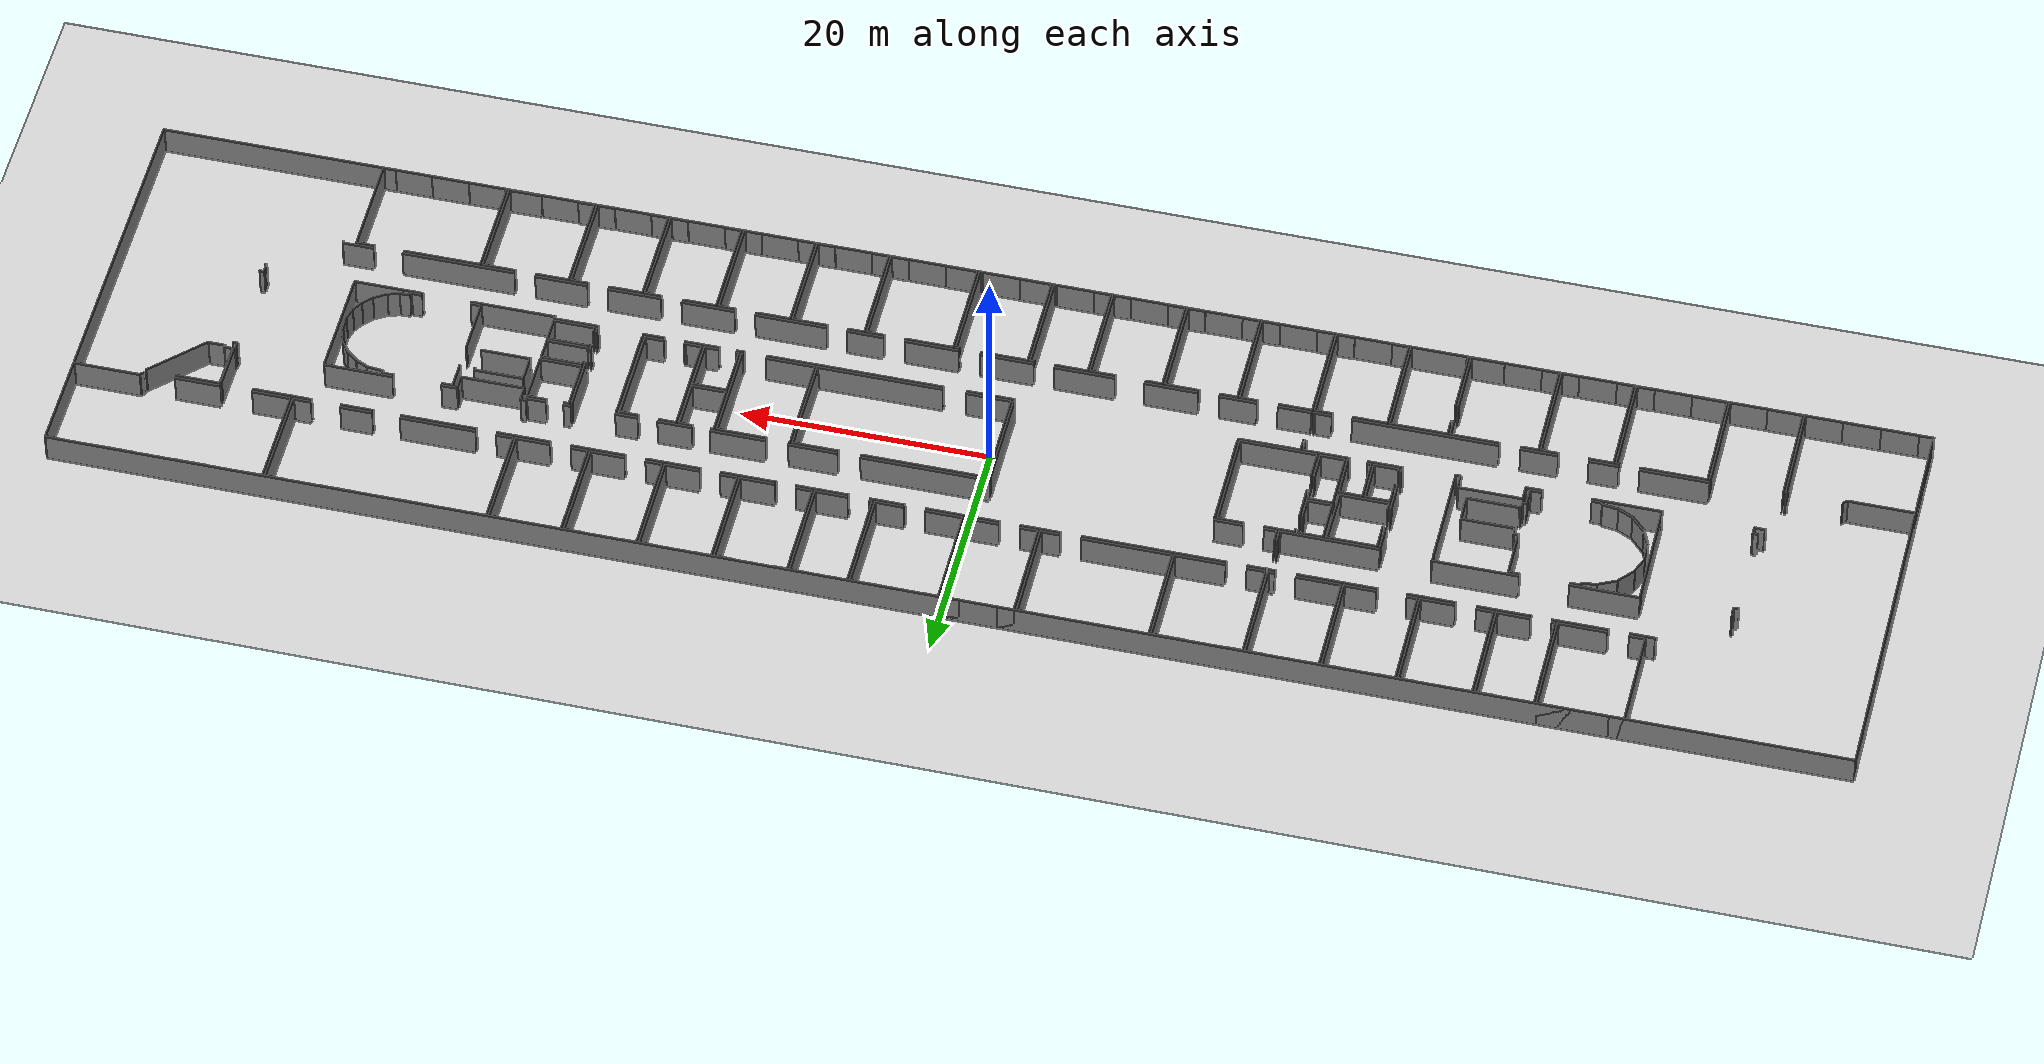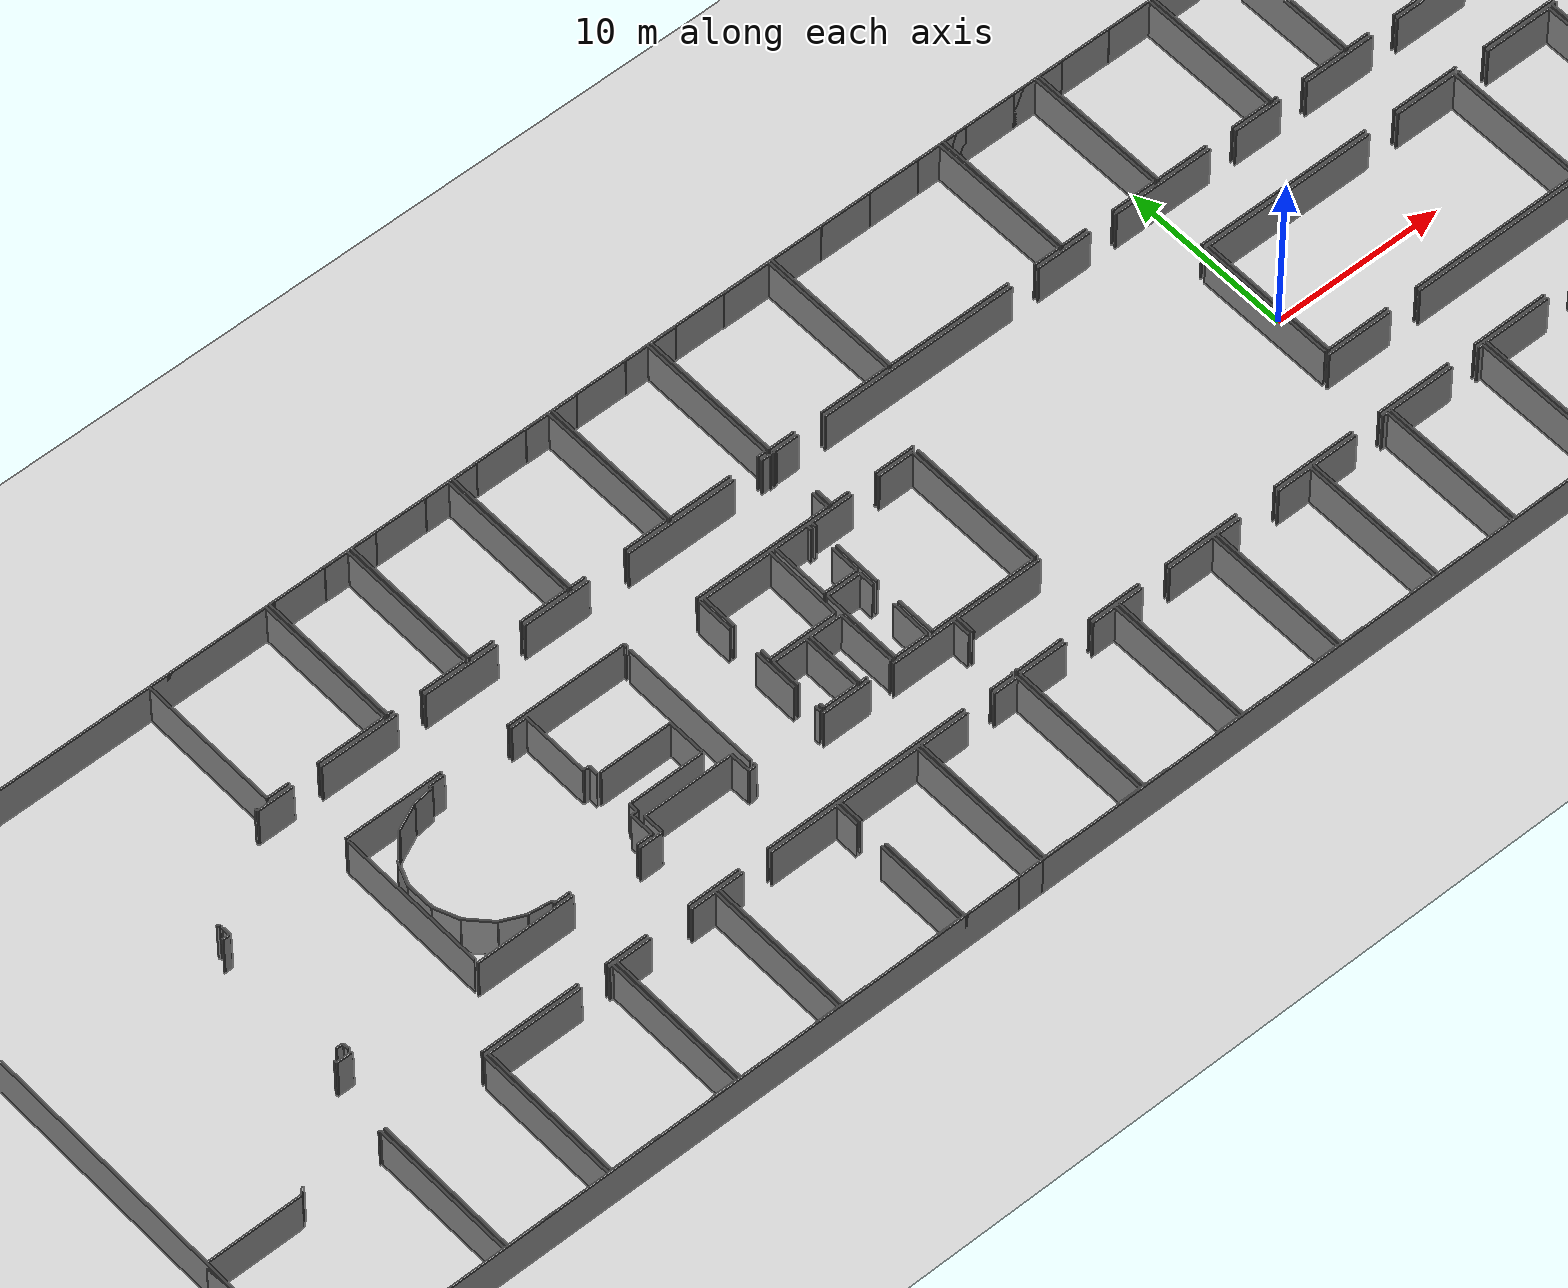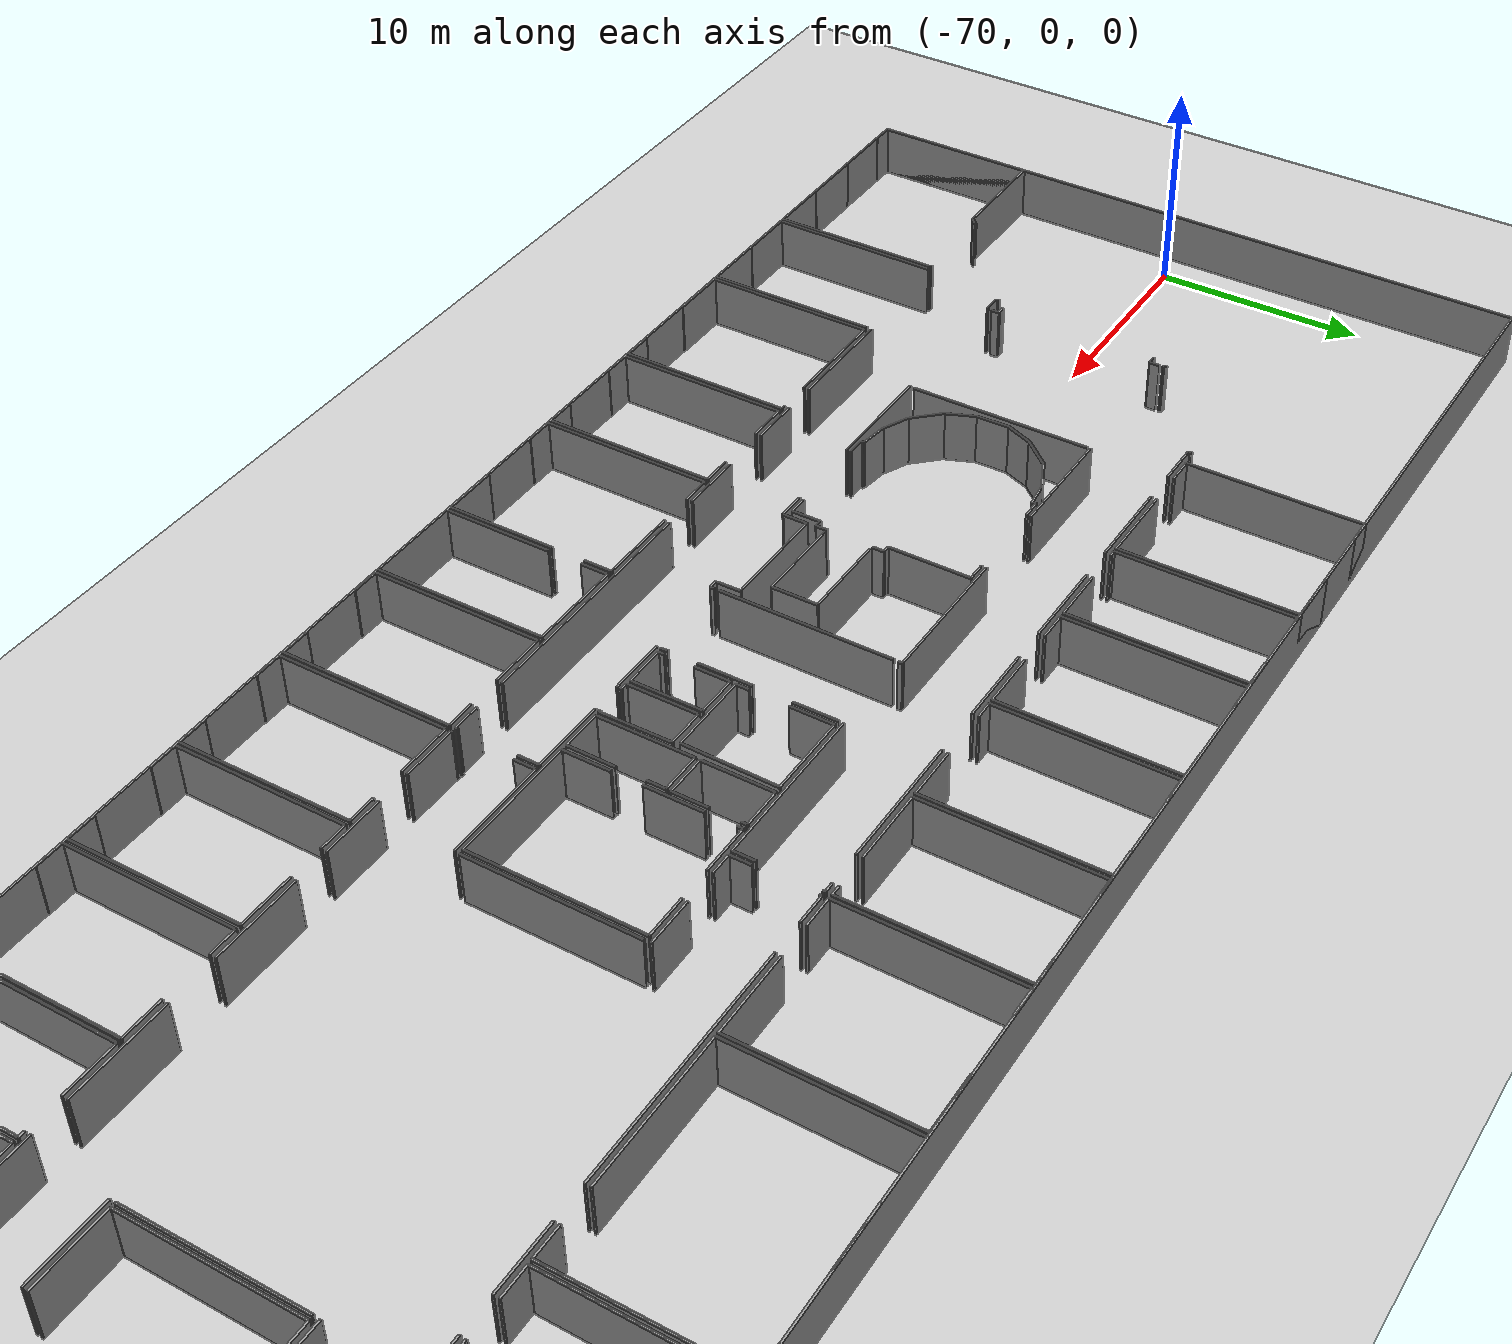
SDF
<sdf version="1.6">
  <world name="default">
    <light name="sun" type="directional">
      <cast_shadows>1</cast_shadows>
      <pose frame="">0 0 10 0 -0 0</pose>
      <diffuse>0.8 0.8 0.8 1</diffuse>
      <specular>0.1 0.1 0.1 1</specular>
      <attenuation>
        <range>1000</range>
        <constant>0.9</constant>
        <linear>0.01</linear>
        <quadratic>0.001</quadratic>
      </attenuation>
      <direction>-0.5 0.5 -1</direction>
    </light>
    <model name="ground_plane">
      <static>1</static>
      <link name="link">
        <collision name="collision">
          <geometry>
            <plane>
              <normal>0 0 1</normal>
              <size>100 100</size>
            </plane>
          </geometry>
          <surface>
            <friction>
              <ode>
                <mu>100</mu>
                <mu2>50</mu2>
              </ode>
              <torsional>
                <ode />
              </torsional>
            </friction>
            <contact>
              <ode />
            </contact>
            <bounce />
          </surface>
          <max_contacts>10</max_contacts>
        </collision>
        <visual name="visual">
          <cast_shadows>0</cast_shadows>
          <geometry>
            <plane>
              <normal>0 0 1</normal>
              <size>100 100</size>
            </plane>
          </geometry>
          <material>
            <script>
              <uri>file://media/materials/scripts/gazebo.material</uri>
              <name>Gazebo/Grey</name>
            </script>
          </material>
        </visual>
        <self_collide>0</self_collide>
        <kinematic>0</kinematic>
        <gravity>1</gravity>
      </link>
    </model>
    <gravity>0 0 -9.8</gravity>
    <magnetic_field>6e-06 2.3e-05 -4.2e-05</magnetic_field>
    <atmosphere type="adiabatic" />
    <physics default="0" name="default_physics" type="ode">
      <max_step_size>0.001</max_step_size>
      <real_time_factor>1</real_time_factor>
      <real_time_update_rate>1000</real_time_update_rate>
    </physics>
    <scene>
      <ambient>0.4 0.4 0.4 1</ambient>
      <background>0.7 0.7 0.7 1</background>
      <shadows>1</shadows>
    </scene>
    <spherical_coordinates>
      <surface_model>EARTH_WGS84</surface_model>
      <latitude_deg>0</latitude_deg>
      <longitude_deg>0</longitude_deg>
      <elevation>0</elevation>
      <heading_deg>0</heading_deg>
    </spherical_coordinates>
  <model name="50041184">
		<static>1</static>
		<link name="Wall_0">
			<collision name="Wall_0_Collision">
				<geometry>
					<box>
						<size>0.124158155655 0.1 2.5</size>
					</box>
				</geometry>
				<pose frame="">0.0620790778274 0 1.25 0 0 0</pose>
			</collision>
			<visual name="Wall_0_Visual">
				<pose frame="">0.0620790778274 0 1.25 0 0 0</pose>
				<geometry>
					<box>
						<size>0.124158155655 0.1 2.5</size>
					</box>
				</geometry>
				<material>
					<script>
						<uri>file://media/materials/scripts/gazebo.material</uri>
						<name>Gazebo/Grey</name>
					</script>
					<ambient>1 1 1 1</ambient>
				</material>
			</visual>
			<pose frame="">47.5227528072 -8.49251940765 0 0 0 -1.57079632679</pose>
		</link>
		<link name="Wall_1">
			<collision name="Wall_1_Collision">
				<geometry>
					<box>
						<size>1.04633079643 0.1 2.5</size>
					</box>
				</geometry>
				<pose frame="">0.523165398214 0 1.25 0 0 0</pose>
			</collision>
			<visual name="Wall_1_Visual">
				<pose frame="">0.523165398214 0 1.25 0 0 0</pose>
				<geometry>
					<box>
						<size>1.04633079643 0.1 2.5</size>
					</box>
				</geometry>
				<material>
					<script>
						<uri>file://media/materials/scripts/gazebo.material</uri>
						<name>Gazebo/Grey</name>
					</script>
					<ambient>1 1 1 1</ambient>
				</material>
			</visual>
			<pose frame="">47.5227528072 -11.4282631188 0 0 0 -1.57079632679</pose>
		</link>
		<link name="Wall_2">
			<collision name="Wall_2_Collision">
				<geometry>
					<box>
						<size>7.89077129128 0.1 2.5</size>
					</box>
				</geometry>
				<pose frame="">3.94538564564 0 1.25 0 0 0</pose>
			</collision>
			<visual name="Wall_2_Visual">
				<pose frame="">3.94538564564 0 1.25 0 0 0</pose>
				<geometry>
					<box>
						<size>7.89077129128 0.1 2.5</size>
					</box>
				</geometry>
				<material>
					<script>
						<uri>file://media/materials/scripts/gazebo.material</uri>
						<name>Gazebo/Grey</name>
					</script>
					<ambient>1 1 1 1</ambient>
				</material>
			</visual>
			<pose frame="">47.5227528072 -12.4745939152 0 0 0 3.14159265359</pose>
		</link>
		<link name="Wall_3">
			<collision name="Wall_3_Collision">
				<geometry>
					<box>
						<size>0.209850134251 0.1 2.5</size>
					</box>
				</geometry>
				<pose frame="">0.104925067125 0 1.25 0 0 0</pose>
			</collision>
			<visual name="Wall_3_Visual">
				<pose frame="">0.104925067125 0 1.25 0 0 0</pose>
				<geometry>
					<box>
						<size>0.209850134251 0.1 2.5</size>
					</box>
				</geometry>
				<material>
					<script>
						<uri>file://media/materials/scripts/gazebo.material</uri>
						<name>Gazebo/Grey</name>
					</script>
					<ambient>1 1 1 1</ambient>
				</material>
			</visual>
			<pose frame="">35.4769996382 -12.4745939152 0 0 0 1.57079632679</pose>
		</link>
		<link name="Wall_4">
			<collision name="Wall_4_Collision">
				<geometry>
					<box>
						<size>6.88773081293 0.1 2.5</size>
					</box>
				</geometry>
				<pose frame="">3.44386540647 0 1.25 0 0 0</pose>
			</collision>
			<visual name="Wall_4_Visual">
				<pose frame="">3.44386540647 0 1.25 0 0 0</pose>
				<geometry>
					<box>
						<size>6.88773081293 0.1 2.5</size>
					</box>
				</geometry>
				<material>
					<script>
						<uri>file://media/materials/scripts/gazebo.material</uri>
						<name>Gazebo/Grey</name>
					</script>
					<ambient>1 1 1 1</ambient>
				</material>
			</visual>
			<pose frame="">35.4769996382 -12.264743781 0 0 0 3.14159265359</pose>
		</link>
		<link name="Wall_5">
			<collision name="Wall_5_Collision">
				<geometry>
					<box>
						<size>5.56972470658 0.1 2.5</size>
					</box>
				</geometry>
				<pose frame="">2.78486235329 0 1.25 0 0 0</pose>
			</collision>
			<visual name="Wall_5_Visual">
				<pose frame="">2.78486235329 0 1.25 0 0 0</pose>
				<geometry>
					<box>
						<size>5.56972470658 0.1 2.5</size>
					</box>
				</geometry>
				<material>
					<script>
						<uri>file://media/materials/scripts/gazebo.material</uri>
						<name>Gazebo/Grey</name>
					</script>
					<ambient>1 1 1 1</ambient>
				</material>
			</visual>
			<pose frame="">24.684507525 -12.264743781 0 0 0 3.14159265359</pose>
		</link>
		<link name="Wall_6">
			<collision name="Wall_6_Collision">
				<geometry>
					<box>
						<size>0.0559854260161 0.1 2.5</size>
					</box>
				</geometry>
				<pose frame="">0.027992713008 0 1.25 0 0 0</pose>
			</collision>
			<visual name="Wall_6_Visual">
				<pose frame="">0.027992713008 0 1.25 0 0 0</pose>
				<geometry>
					<box>
						<size>0.0559854260161 0.1 2.5</size>
					</box>
				</geometry>
				<material>
					<script>
						<uri>file://media/materials/scripts/gazebo.material</uri>
						<name>Gazebo/Grey</name>
					</script>
					<ambient>1 1 1 1</ambient>
				</material>
			</visual>
			<pose frame="">11.8893621343 -12.264743781 0 0 0 1.57079632679</pose>
		</link>
		<link name="Wall_7">
			<collision name="Wall_7_Collision">
				<geometry>
					<box>
						<size>0.164275383497 0.1 2.5</size>
					</box>
				</geometry>
				<pose frame="">0.0821376917483 0 1.25 0 0 0</pose>
			</collision>
			<visual name="Wall_7_Visual">
				<pose frame="">0.0821376917483 0 1.25 0 0 0</pose>
				<geometry>
					<box>
						<size>0.164275383497 0.1 2.5</size>
					</box>
				</geometry>
				<material>
					<script>
						<uri>file://media/materials/scripts/gazebo.material</uri>
						<name>Gazebo/Grey</name>
					</script>
					<ambient>1 1 1 1</ambient>
				</material>
			</visual>
			<pose frame="">11.8893621343 -12.208758355 0 0 0 2.35619449019</pose>
		</link>
		<link name="Wall_8">
			<collision name="Wall_8_Collision">
				<geometry>
					<box>
						<size>0.16960664208 0.1 2.5</size>
					</box>
				</geometry>
				<pose frame="">0.0848033210402 0 1.25 0 0 0</pose>
			</collision>
			<visual name="Wall_8_Visual">
				<pose frame="">0.0848033210402 0 1.25 0 0 0</pose>
				<geometry>
					<box>
						<size>0.16960664208 0.1 2.5</size>
					</box>
				</geometry>
				<material>
					<script>
						<uri>file://media/materials/scripts/gazebo.material</uri>
						<name>Gazebo/Grey</name>
					</script>
					<ambient>1 1 1 1</ambient>
				</material>
			</visual>
			<pose frame="">17.1340920776 -8.33852774833 0 0 0 -1.57079632679</pose>
		</link>
		<link name="Wall_9">
			<collision name="Wall_9_Collision">
				<geometry>
					<box>
						<size>2.052925905 0.1 2.5</size>
					</box>
				</geometry>
				<pose frame="">1.0264629525 0 1.25 0 0 0</pose>
			</collision>
			<visual name="Wall_9_Visual">
				<pose frame="">1.0264629525 0 1.25 0 0 0</pose>
				<geometry>
					<box>
						<size>2.052925905 0.1 2.5</size>
					</box>
				</geometry>
				<material>
					<script>
						<uri>file://media/materials/scripts/gazebo.material</uri>
						<name>Gazebo/Grey</name>
					</script>
					<ambient>1 1 1 1</ambient>
				</material>
			</visual>
			<pose frame="">17.1340920776 -8.50813439041 0 0 0 0.0</pose>
		</link>
		<link name="Wall_10">
			<collision name="Wall_10_Collision">
				<geometry>
					<box>
						<size>4.42361036175 0.1 2.5</size>
					</box>
				</geometry>
				<pose frame="">2.21180518087 0 1.25 0 0 0</pose>
			</collision>
			<visual name="Wall_10_Visual">
				<pose frame="">2.21180518087 0 1.25 0 0 0</pose>
				<geometry>
					<box>
						<size>4.42361036175 0.1 2.5</size>
					</box>
				</geometry>
				<material>
					<script>
						<uri>file://media/materials/scripts/gazebo.material</uri>
						<name>Gazebo/Grey</name>
					</script>
					<ambient>1 1 1 1</ambient>
				</material>
			</visual>
			<pose frame="">20.8286223904 -8.50813439041 0 0 0 0.0</pose>
		</link>
		<link name="Wall_11">
			<collision name="Wall_11_Collision">
				<geometry>
					<box>
						<size>4.26415980602 0.1 2.5</size>
					</box>
				</geometry>
				<pose frame="">2.13207990301 0 1.25 0 0 0</pose>
			</collision>
			<visual name="Wall_11_Visual">
				<pose frame="">2.13207990301 0 1.25 0 0 0</pose>
				<geometry>
					<box>
						<size>4.26415980602 0.1 2.5</size>
					</box>
				</geometry>
				<material>
					<script>
						<uri>file://media/materials/scripts/gazebo.material</uri>
						<name>Gazebo/Grey</name>
					</script>
					<ambient>1 1 1 1</ambient>
				</material>
			</visual>
			<pose frame="">26.8835541224 -8.50813439041 0 0 0 0.0</pose>
		</link>
		<link name="Wall_12">
			<collision name="Wall_12_Collision">
				<geometry>
					<box>
						<size>3.83062186986 0.1 2.5</size>
					</box>
				</geometry>
				<pose frame="">1.91531093493 0 1.25 0 0 0</pose>
			</collision>
			<visual name="Wall_12_Visual">
				<pose frame="">1.91531093493 0 1.25 0 0 0</pose>
				<geometry>
					<box>
						<size>3.83062186986 0.1 2.5</size>
					</box>
				</geometry>
				<material>
					<script>
						<uri>file://media/materials/scripts/gazebo.material</uri>
						<name>Gazebo/Grey</name>
					</script>
					<ambient>1 1 1 1</ambient>
				</material>
			</visual>
			<pose frame="">32.7894452873 -8.50813439041 0 0 0 0.0</pose>
		</link>
		<link name="Wall_13">
			<collision name="Wall_13_Collision">
				<geometry>
					<box>
						<size>6.39401806514 0.1 2.5</size>
					</box>
				</geometry>
				<pose frame="">3.19700903257 0 1.25 0 0 0</pose>
			</collision>
			<visual name="Wall_13_Visual">
				<pose frame="">3.19700903257 0 1.25 0 0 0</pose>
				<geometry>
					<box>
						<size>6.39401806514 0.1 2.5</size>
					</box>
				</geometry>
				<material>
					<script>
						<uri>file://media/materials/scripts/gazebo.material</uri>
						<name>Gazebo/Grey</name>
					</script>
					<ambient>1 1 1 1</ambient>
				</material>
			</visual>
			<pose frame="">38.9601564037 -8.50813439041 0 0 0 0.0</pose>
		</link>
		<link name="Wall_14">
			<collision name="Wall_14_Collision">
				<geometry>
					<box>
						<size>0.503983841448 0.1 2.5</size>
					</box>
				</geometry>
				<pose frame="">0.251991920724 0 1.25 0 0 0</pose>
			</collision>
			<visual name="Wall_14_Visual">
				<pose frame="">0.251991920724 0 1.25 0 0 0</pose>
				<geometry>
					<box>
						<size>0.503983841448 0.1 2.5</size>
					</box>
				</geometry>
				<material>
					<script>
						<uri>file://media/materials/scripts/gazebo.material</uri>
						<name>Gazebo/Grey</name>
					</script>
					<ambient>1 1 1 1</ambient>
				</material>
			</visual>
			<pose frame="">47.0190109241 -8.50813439041 0 0 0 0.0309880611951</pose>
		</link>
		<link name="Wall_15">
			<collision name="Wall_15_Collision">
				<geometry>
					<box>
						<size>3.86972280232 0.1 2.5</size>
					</box>
				</geometry>
				<pose frame="">1.93486140116 0 1.25 0 0 0</pose>
			</collision>
			<visual name="Wall_15_Visual">
				<pose frame="">1.93486140116 0 1.25 0 0 0</pose>
				<geometry>
					<box>
						<size>3.86972280232 0.1 2.5</size>
					</box>
				</geometry>
				<material>
					<script>
						<uri>file://media/materials/scripts/gazebo.material</uri>
						<name>Gazebo/Grey</name>
					</script>
					<ambient>1 1 1 1</ambient>
				</material>
			</visual>
			<pose frame="">24.7281786963 -8.23836334668 0 0 0 3.14159265359</pose>
		</link>
		<link name="Wall_16">
			<collision name="Wall_16_Collision">
				<geometry>
					<box>
						<size>1.27674700554 0.1 2.5</size>
					</box>
				</geometry>
				<pose frame="">0.638373502771 0 1.25 0 0 0</pose>
			</collision>
			<visual name="Wall_16_Visual">
				<pose frame="">0.638373502771 0 1.25 0 0 0</pose>
				<geometry>
					<box>
						<size>1.27674700554 0.1 2.5</size>
					</box>
				</geometry>
				<material>
					<script>
						<uri>file://media/materials/scripts/gazebo.material</uri>
						<name>Gazebo/Grey</name>
					</script>
					<ambient>1 1 1 1</ambient>
				</material>
			</visual>
			<pose frame="">19.1872718848 -8.23836334668 0 0 0 3.14159265359</pose>
		</link>
		<link name="Wall_17">
			<collision name="Wall_17_Collision">
				<geometry>
					<box>
						<size>8.23836334668 0.1 2.5</size>
					</box>
				</geometry>
				<pose frame="">4.11918167334 0 1.25 0 0 0</pose>
			</collision>
			<visual name="Wall_17_Visual">
				<pose frame="">4.11918167334 0 1.25 0 0 0</pose>
				<geometry>
					<box>
						<size>8.23836334668 0.1 2.5</size>
					</box>
				</geometry>
				<material>
					<script>
						<uri>file://media/materials/scripts/gazebo.material</uri>
						<name>Gazebo/Grey</name>
					</script>
					<ambient>1 1 1 1</ambient>
				</material>
			</visual>
			<pose frame="">17.9105248792 -8.23836334668 0 0 0 1.57079632679</pose>
		</link>
		<link name="Wall_18">
			<collision name="Wall_18_Collision">
				<geometry>
					<box>
						<size>1.2227927968 0.1 2.5</size>
					</box>
				</geometry>
				<pose frame="">0.611396398398 0 1.25 0 0 0</pose>
			</collision>
			<visual name="Wall_18_Visual">
				<pose frame="">0.611396398398 0 1.25 0 0 0</pose>
				<geometry>
					<box>
						<size>1.2227927968 0.1 2.5</size>
					</box>
				</geometry>
				<material>
					<script>
						<uri>file://media/materials/scripts/gazebo.material</uri>
						<name>Gazebo/Grey</name>
					</script>
					<ambient>1 1 1 1</ambient>
				</material>
			</visual>
			<pose frame="">17.9105248792 -0.0 0 0 0 0.0</pose>
		</link>
		<link name="Wall_19">
			<collision name="Wall_19_Collision">
				<geometry>
					<box>
						<size>2.60046591046 0.1 2.5</size>
					</box>
				</geometry>
				<pose frame="">1.30023295523 0 1.25 0 0 0</pose>
			</collision>
			<visual name="Wall_19_Visual">
				<pose frame="">1.30023295523 0 1.25 0 0 0</pose>
				<geometry>
					<box>
						<size>2.60046591046 0.1 2.5</size>
					</box>
				</geometry>
				<material>
					<script>
						<uri>file://media/materials/scripts/gazebo.material</uri>
						<name>Gazebo/Grey</name>
					</script>
					<ambient>1 1 1 1</ambient>
				</material>
			</visual>
			<pose frame="">22.1093048794 -0.0 0 0 0 0.0</pose>
		</link>
		<link name="Wall_20">
			<collision name="Wall_20_Collision">
				<geometry>
					<box>
						<size>8.23838391209 0.1 2.5</size>
					</box>
				</geometry>
				<pose frame="">4.11919195605 0 1.25 0 0 0</pose>
			</collision>
			<visual name="Wall_20_Visual">
				<pose frame="">4.11919195605 0 1.25 0 0 0</pose>
				<geometry>
					<box>
						<size>8.23838391209 0.1 2.5</size>
					</box>
				</geometry>
				<material>
					<script>
						<uri>file://media/materials/scripts/gazebo.material</uri>
						<name>Gazebo/Grey</name>
					</script>
					<ambient>1 1 1 1</ambient>
				</material>
			</visual>
			<pose frame="">24.7097707898 -0.0 0 0 0 -1.56856191747</pose>
		</link>
		<link name="Wall_21">
			<collision name="Wall_21_Collision">
				<geometry>
					<box>
						<size>2.62306320259 0.1 2.5</size>
					</box>
				</geometry>
				<pose frame="">1.3115316013 0 1.25 0 0 0</pose>
			</collision>
			<visual name="Wall_21_Visual">
				<pose frame="">1.3115316013 0 1.25 0 0 0</pose>
				<geometry>
					<box>
						<size>2.62306320259 0.1 2.5</size>
					</box>
				</geometry>
				<material>
					<script>
						<uri>file://media/materials/scripts/gazebo.material</uri>
						<name>Gazebo/Grey</name>
					</script>
					<ambient>1 1 1 1</ambient>
				</material>
			</visual>
			<pose frame="">29.5191854819 -8.23036542868 0 0 0 3.14159265359</pose>
		</link>
		<link name="Wall_22">
			<collision name="Wall_22_Collision">
				<geometry>
					<box>
						<size>0.307348563231 0.1 2.5</size>
					</box>
				</geometry>
				<pose frame="">0.153674281616 0 1.25 0 0 0</pose>
			</collision>
			<visual name="Wall_22_Visual">
				<pose frame="">0.153674281616 0 1.25 0 0 0</pose>
				<geometry>
					<box>
						<size>0.307348563231 0.1 2.5</size>
					</box>
				</geometry>
				<material>
					<script>
						<uri>file://media/materials/scripts/gazebo.material</uri>
						<name>Gazebo/Grey</name>
					</script>
					<ambient>1 1 1 1</ambient>
				</material>
			</visual>
			<pose frame="">25.2467738557 -8.23036542868 0 0 0 3.14159265359</pose>
		</link>
		<link name="Wall_23">
			<collision name="Wall_23_Collision">
				<geometry>
					<box>
						<size>8.20269009337 0.1 2.5</size>
					</box>
				</geometry>
				<pose frame="">4.10134504669 0 1.25 0 0 0</pose>
			</collision>
			<visual name="Wall_23_Visual">
				<pose frame="">4.10134504669 0 1.25 0 0 0</pose>
				<geometry>
					<box>
						<size>8.20269009337 0.1 2.5</size>
					</box>
				</geometry>
				<material>
					<script>
						<uri>file://media/materials/scripts/gazebo.material</uri>
						<name>Gazebo/Grey</name>
					</script>
					<ambient>1 1 1 1</ambient>
				</material>
			</visual>
			<pose frame="">24.9394252925 -8.23036542868 0 0 0 1.57079632679</pose>
		</link>
		<link name="Wall_24">
			<collision name="Wall_24_Collision">
				<geometry>
					<box>
						<size>0.19525076012 0.1 2.5</size>
					</box>
				</geometry>
				<pose frame="">0.0976253800598 0 1.25 0 0 0</pose>
			</collision>
			<visual name="Wall_24_Visual">
				<pose frame="">0.0976253800598 0 1.25 0 0 0</pose>
				<geometry>
					<box>
						<size>0.19525076012 0.1 2.5</size>
					</box>
				</geometry>
				<material>
					<script>
						<uri>file://media/materials/scripts/gazebo.material</uri>
						<name>Gazebo/Grey</name>
					</script>
					<ambient>1 1 1 1</ambient>
				</material>
			</visual>
			<pose frame="">24.9394252925 -0.0276753353095 0 0 0 0.0</pose>
		</link>
		<link name="Wall_25">
			<collision name="Wall_25_Collision">
				<geometry>
					<box>
						<size>1.41829745907 0.1 2.5</size>
					</box>
				</geometry>
				<pose frame="">0.709148729537 0 1.25 0 0 0</pose>
			</collision>
			<visual name="Wall_25_Visual">
				<pose frame="">0.709148729537 0 1.25 0 0 0</pose>
				<geometry>
					<box>
						<size>1.41829745907 0.1 2.5</size>
					</box>
				</geometry>
				<material>
					<script>
						<uri>file://media/materials/scripts/gazebo.material</uri>
						<name>Gazebo/Grey</name>
					</script>
					<ambient>1 1 1 1</ambient>
				</material>
			</visual>
			<pose frame="">28.1010149739 -0.0276753353095 0 0 0 0.0</pose>
		</link>
		<link name="Wall_26">
			<collision name="Wall_26_Collision">
				<geometry>
					<box>
						<size>8.20269009435 0.1 2.5</size>
					</box>
				</geometry>
				<pose frame="">4.10134504718 0 1.25 0 0 0</pose>
			</collision>
			<visual name="Wall_26_Visual">
				<pose frame="">4.10134504718 0 1.25 0 0 0</pose>
				<geometry>
					<box>
						<size>8.20269009435 0.1 2.5</size>
					</box>
				</geometry>
				<material>
					<script>
						<uri>file://media/materials/scripts/gazebo.material</uri>
						<name>Gazebo/Grey</name>
					</script>
					<ambient>1 1 1 1</ambient>
				</material>
			</visual>
			<pose frame="">29.519312433 -0.0276753353095 0 0 0 -1.57081180356</pose>
		</link>
		<link name="Wall_27">
			<collision name="Wall_27_Collision">
				<geometry>
					<box>
						<size>2.73896953809 0.1 2.5</size>
					</box>
				</geometry>
				<pose frame="">1.36948476904 0 1.25 0 0 0</pose>
			</collision>
			<visual name="Wall_27_Visual">
				<pose frame="">1.36948476904 0 1.25 0 0 0</pose>
				<geometry>
					<box>
						<size>2.73896953809 0.1 2.5</size>
					</box>
				</geometry>
				<material>
					<script>
						<uri>file://media/materials/scripts/gazebo.material</uri>
						<name>Gazebo/Grey</name>
					</script>
					<ambient>1 1 1 1</ambient>
				</material>
			</visual>
			<pose frame="">35.540602129 -8.22414482579 0 0 0 3.14159265359</pose>
		</link>
		<link name="Wall_28">
			<collision name="Wall_28_Collision">
				<geometry>
					<box>
						<size>1.40814137272 0.1 2.5</size>
					</box>
				</geometry>
				<pose frame="">0.704070686361 0 1.25 0 0 0</pose>
			</collision>
			<visual name="Wall_28_Visual">
				<pose frame="">0.704070686361 0 1.25 0 0 0</pose>
				<geometry>
					<box>
						<size>1.40814137272 0.1 2.5</size>
					</box>
				</geometry>
				<material>
					<script>
						<uri>file://media/materials/scripts/gazebo.material</uri>
						<name>Gazebo/Grey</name>
					</script>
					<ambient>1 1 1 1</ambient>
				</material>
			</visual>
			<pose frame="">31.1672643947 -8.22414482579 0 0 0 3.14159265359</pose>
		</link>
		<link name="Wall_29">
			<collision name="Wall_29_Collision">
				<geometry>
					<box>
						<size>8.20738728331 0.1 2.5</size>
					</box>
				</geometry>
				<pose frame="">4.10369364166 0 1.25 0 0 0</pose>
			</collision>
			<visual name="Wall_29_Visual">
				<pose frame="">4.10369364166 0 1.25 0 0 0</pose>
				<geometry>
					<box>
						<size>8.20738728331 0.1 2.5</size>
					</box>
				</geometry>
				<material>
					<script>
						<uri>file://media/materials/scripts/gazebo.material</uri>
						<name>Gazebo/Grey</name>
					</script>
					<ambient>1 1 1 1</ambient>
				</material>
			</visual>
			<pose frame="">29.7591230219 -8.22414482579 0 0 0 1.57079632679</pose>
		</link>
		<link name="Wall_30">
			<collision name="Wall_30_Collision">
				<geometry>
					<box>
						<size>1.37691140719 0.1 2.5</size>
					</box>
				</geometry>
				<pose frame="">0.688455703595 0 1.25 0 0 0</pose>
			</collision>
			<visual name="Wall_30_Visual">
				<pose frame="">0.688455703595 0 1.25 0 0 0</pose>
				<geometry>
					<box>
						<size>1.37691140719 0.1 2.5</size>
					</box>
				</geometry>
				<material>
					<script>
						<uri>file://media/materials/scripts/gazebo.material</uri>
						<name>Gazebo/Grey</name>
					</script>
					<ambient>1 1 1 1</ambient>
				</material>
			</visual>
			<pose frame="">29.7591230219 -0.016757542481 0 0 0 0.0</pose>
		</link>
		<link name="Wall_31">
			<collision name="Wall_31_Collision">
				<geometry>
					<box>
						<size>1.43264293105 0.1 2.5</size>
					</box>
				</geometry>
				<pose frame="">0.716321465523 0 1.25 0 0 0</pose>
			</collision>
			<visual name="Wall_31_Visual">
				<pose frame="">0.716321465523 0 1.25 0 0 0</pose>
				<geometry>
					<box>
						<size>1.43264293105 0.1 2.5</size>
					</box>
				</geometry>
				<material>
					<script>
						<uri>file://media/materials/scripts/gazebo.material</uri>
						<name>Gazebo/Grey</name>
					</script>
					<ambient>1 1 1 1</ambient>
				</material>
			</visual>
			<pose frame="">34.0843462972 -0.016757542481 0 0 0 0.0</pose>
		</link>
		<link name="Wall_32">
			<collision name="Wall_32_Collision">
				<geometry>
					<box>
						<size>8.20742125075 0.1 2.5</size>
					</box>
				</geometry>
				<pose frame="">4.10371062538 0 1.25 0 0 0</pose>
			</collision>
			<visual name="Wall_32_Visual">
				<pose frame="">4.10371062538 0 1.25 0 0 0</pose>
				<geometry>
					<box>
						<size>8.20742125075 0.1 2.5</size>
					</box>
				</geometry>
				<material>
					<script>
						<uri>file://media/materials/scripts/gazebo.material</uri>
						<name>Gazebo/Grey</name>
					</script>
					<ambient>1 1 1 1</ambient>
				</material>
			</visual>
			<pose frame="">35.5169892282 -0.016757542481 0 0 0 -1.56791930457</pose>
		</link>
		<link name="Wall_33">
			<collision name="Wall_33_Collision">
				<geometry>
					<box>
						<size>2.53572085997 0.1 2.5</size>
					</box>
				</geometry>
				<pose frame="">1.26786042998 0 1.25 0 0 0</pose>
			</collision>
			<visual name="Wall_33_Visual">
				<pose frame="">1.26786042998 0 1.25 0 0 0</pose>
				<geometry>
					<box>
						<size>2.53572085997 0.1 2.5</size>
					</box>
				</geometry>
				<material>
					<script>
						<uri>file://media/materials/scripts/gazebo.material</uri>
						<name>Gazebo/Grey</name>
					</script>
					<ambient>1 1 1 1</ambient>
				</material>
			</visual>
			<pose frame="">41.5365016091 -8.22389092363 0 0 0 3.14159265359</pose>
		</link>
		<link name="Wall_34">
			<collision name="Wall_34_Collision">
				<geometry>
					<box>
						<size>0.863902095328 0.1 2.5</size>
					</box>
				</geometry>
				<pose frame="">0.431951047664 0 1.25 0 0 0</pose>
			</collision>
			<visual name="Wall_34_Visual">
				<pose frame="">0.431951047664 0 1.25 0 0 0</pose>
				<geometry>
					<box>
						<size>0.863902095328 0.1 2.5</size>
					</box>
				</geometry>
				<material>
					<script>
						<uri>file://media/materials/scripts/gazebo.material</uri>
						<name>Gazebo/Grey</name>
					</script>
					<ambient>1 1 1 1</ambient>
				</material>
			</visual>
			<pose frame="">36.6292076348 -8.22389092363 0 0 0 3.14159265359</pose>
		</link>
		<link name="Wall_35">
			<collision name="Wall_35_Collision">
				<geometry>
					<box>
						<size>8.19964326747 0.1 2.5</size>
					</box>
				</geometry>
				<pose frame="">4.09982163373 0 1.25 0 0 0</pose>
			</collision>
			<visual name="Wall_35_Visual">
				<pose frame="">4.09982163373 0 1.25 0 0 0</pose>
				<geometry>
					<box>
						<size>8.19964326747 0.1 2.5</size>
					</box>
				</geometry>
				<material>
					<script>
						<uri>file://media/materials/scripts/gazebo.material</uri>
						<name>Gazebo/Grey</name>
					</script>
					<ambient>1 1 1 1</ambient>
				</material>
			</visual>
			<pose frame="">35.7653055395 -8.22389092363 0 0 0 1.57079632679</pose>
		</link>
		<link name="Wall_36">
			<collision name="Wall_36_Collision">
				<geometry>
					<box>
						<size>1.35951910931 0.1 2.5</size>
					</box>
				</geometry>
				<pose frame="">0.679759554656 0 1.25 0 0 0</pose>
			</collision>
			<visual name="Wall_36_Visual">
				<pose frame="">0.679759554656 0 1.25 0 0 0</pose>
				<geometry>
					<box>
						<size>1.35951910931 0.1 2.5</size>
					</box>
				</geometry>
				<material>
					<script>
						<uri>file://media/materials/scripts/gazebo.material</uri>
						<name>Gazebo/Grey</name>
					</script>
					<ambient>1 1 1 1</ambient>
				</material>
			</visual>
			<pose frame="">35.7653055395 -0.0242476561657 0 0 0 0.0</pose>
		</link>
		<link name="Wall_37">
			<collision name="Wall_37_Collision">
				<geometry>
					<box>
						<size>1.42007477419 0.1 2.5</size>
					</box>
				</geometry>
				<pose frame="">0.710037387093 0 1.25 0 0 0</pose>
			</collision>
			<visual name="Wall_37_Visual">
				<pose frame="">0.710037387093 0 1.25 0 0 0</pose>
				<geometry>
					<box>
						<size>1.42007477419 0.1 2.5</size>
					</box>
				</geometry>
				<material>
					<script>
						<uri>file://media/materials/scripts/gazebo.material</uri>
						<name>Gazebo/Grey</name>
					</script>
					<ambient>1 1 1 1</ambient>
				</material>
			</visual>
			<pose frame="">40.0850699183 -0.0242476561657 0 0 0 0.0</pose>
		</link>
		<link name="Wall_38">
			<collision name="Wall_38_Collision">
				<geometry>
					<box>
						<size>8.1997032245 0.1 2.5</size>
					</box>
				</geometry>
				<pose frame="">4.09985161225 0 1.25 0 0 0</pose>
			</collision>
			<visual name="Wall_38_Visual">
				<pose frame="">4.09985161225 0 1.25 0 0 0</pose>
				<geometry>
					<box>
						<size>8.1997032245 0.1 2.5</size>
					</box>
				</geometry>
				<material>
					<script>
						<uri>file://media/materials/scripts/gazebo.material</uri>
						<name>Gazebo/Grey</name>
					</script>
					<ambient>1 1 1 1</ambient>
				</material>
			</visual>
			<pose frame="">41.5051446925 -0.0242476561657 0 0 0 -1.56697216485</pose>
		</link>
		<link name="Wall_39">
			<collision name="Wall_39_Collision">
				<geometry>
					<box>
						<size>0.499298595286 0.1 2.5</size>
					</box>
				</geometry>
				<pose frame="">0.249649297643 0 1.25 0 0 0</pose>
			</collision>
			<visual name="Wall_39_Visual">
				<pose frame="">0.249649297643 0 1.25 0 0 0</pose>
				<geometry>
					<box>
						<size>0.499298595286 0.1 2.5</size>
					</box>
				</geometry>
				<material>
					<script>
						<uri>file://media/materials/scripts/gazebo.material</uri>
						<name>Gazebo/Grey</name>
					</script>
					<ambient>1 1 1 1</ambient>
				</material>
			</visual>
			<pose frame="">47.5161513511 -8.2216058042 0 0 0 3.14159265359</pose>
		</link>
		<link name="Wall_40">
			<collision name="Wall_40_Collision">
				<geometry>
					<box>
						<size>3.63333989247 0.1 2.5</size>
					</box>
				</geometry>
				<pose frame="">1.81666994624 0 1.25 0 0 0</pose>
			</collision>
			<visual name="Wall_40_Visual">
				<pose frame="">1.81666994624 0 1.25 0 0 0</pose>
				<geometry>
					<box>
						<size>3.63333989247 0.1 2.5</size>
					</box>
				</geometry>
				<material>
					<script>
						<uri>file://media/materials/scripts/gazebo.material</uri>
						<name>Gazebo/Grey</name>
					</script>
					<ambient>1 1 1 1</ambient>
				</material>
			</visual>
			<pose frame="">45.3728362775 -8.2216058042 0 0 0 3.14159265359</pose>
		</link>
		<link name="Wall_41">
			<collision name="Wall_41_Collision">
				<geometry>
					<box>
						<size>8.20294399553 0.1 2.5</size>
					</box>
				</geometry>
				<pose frame="">4.10147199777 0 1.25 0 0 0</pose>
			</collision>
			<visual name="Wall_41_Visual">
				<pose frame="">4.10147199777 0 1.25 0 0 0</pose>
				<geometry>
					<box>
						<size>8.20294399553 0.1 2.5</size>
					</box>
				</geometry>
				<material>
					<script>
						<uri>file://media/materials/scripts/gazebo.material</uri>
						<name>Gazebo/Grey</name>
					</script>
					<ambient>1 1 1 1</ambient>
				</material>
			</visual>
			<pose frame="">41.7394963851 -8.2216058042 0 0 0 1.57079632679</pose>
		</link>
		<link name="Wall_42">
			<collision name="Wall_42_Collision">
				<geometry>
					<box>
						<size>1.39417675399 0.1 2.5</size>
					</box>
				</geometry>
				<pose frame="">0.697088376994 0 1.25 0 0 0</pose>
			</collision>
			<visual name="Wall_42_Visual">
				<pose frame="">0.697088376994 0 1.25 0 0 0</pose>
				<geometry>
					<box>
						<size>1.39417675399 0.1 2.5</size>
					</box>
				</geometry>
				<material>
					<script>
						<uri>file://media/materials/scripts/gazebo.material</uri>
						<name>Gazebo/Grey</name>
					</script>
					<ambient>1 1 1 1</ambient>
				</material>
			</visual>
			<pose frame="">41.7394963851 -0.018661808672 0 0 0 0.0</pose>
		</link>
		<link name="Wall_43">
			<collision name="Wall_43_Collision">
				<geometry>
					<box>
						<size>1.41055344323 0.1 2.5</size>
					</box>
				</geometry>
				<pose frame="">0.705276721615 0 1.25 0 0 0</pose>
			</collision>
			<visual name="Wall_43_Visual">
				<pose frame="">0.705276721615 0 1.25 0 0 0</pose>
				<geometry>
					<box>
						<size>1.41055344323 0.1 2.5</size>
					</box>
				</geometry>
				<material>
					<script>
						<uri>file://media/materials/scripts/gazebo.material</uri>
						<name>Gazebo/Grey</name>
					</script>
					<ambient>1 1 1 1</ambient>
				</material>
			</visual>
			<pose frame="">46.1028049841 -0.018661808672 0 0 0 0.0</pose>
		</link>
		<link name="Wall_44">
			<collision name="Wall_44_Collision">
				<geometry>
					<box>
						<size>8.202944471 0.1 2.5</size>
					</box>
				</geometry>
				<pose frame="">4.1014722355 0 1.25 0 0 0</pose>
			</collision>
			<visual name="Wall_44_Visual">
				<pose frame="">4.1014722355 0 1.25 0 0 0</pose>
				<geometry>
					<box>
						<size>8.202944471 0.1 2.5</size>
					</box>
				</geometry>
				<material>
					<script>
						<uri>file://media/materials/scripts/gazebo.material</uri>
						<name>Gazebo/Grey</name>
					</script>
					<ambient>1 1 1 1</ambient>
				</material>
			</visual>
			<pose frame="">47.5133584273 -0.018661808672 0 0 0 -1.57045584859</pose>
		</link>
		<link name="Wall_45">
			<collision name="Wall_45_Collision">
				<geometry>
					<box>
						<size>3.74175611428 0.1 2.5</size>
					</box>
				</geometry>
				<pose frame="">1.87087805714 0 1.25 0 0 0</pose>
			</collision>
			<visual name="Wall_45_Visual">
				<pose frame="">1.87087805714 0 1.25 0 0 0</pose>
				<geometry>
					<box>
						<size>3.74175611428 0.1 2.5</size>
					</box>
				</geometry>
				<material>
					<script>
						<uri>file://media/materials/scripts/gazebo.material</uri>
						<name>Gazebo/Grey</name>
					</script>
					<ambient>1 1 1 1</ambient>
				</material>
			</visual>
			<pose frame="">131.436781536 -8.50927695013 0 0 0 -1.57079632679</pose>
		</link>
		<link name="Wall_46">
			<collision name="Wall_46_Collision">
				<geometry>
					<box>
						<size>0.083787712405 0.1 2.5</size>
					</box>
				</geometry>
				<pose frame="">0.0418938562025 0 1.25 0 0 0</pose>
			</collision>
			<visual name="Wall_46_Visual">
				<pose frame="">0.0418938562025 0 1.25 0 0 0</pose>
				<geometry>
					<box>
						<size>0.083787712405 0.1 2.5</size>
					</box>
				</geometry>
				<material>
					<script>
						<uri>file://media/materials/scripts/gazebo.material</uri>
						<name>Gazebo/Grey</name>
					</script>
					<ambient>1 1 1 1</ambient>
				</material>
			</visual>
			<pose frame="">131.436781536 -12.2510330644 0 0 0 3.14159265359</pose>
		</link>
		<link name="Wall_47">
			<collision name="Wall_47_Collision">
				<geometry>
					<box>
						<size>5.54014510508 0.1 2.5</size>
					</box>
				</geometry>
				<pose frame="">2.77007255254 0 1.25 0 0 0</pose>
			</collision>
			<visual name="Wall_47_Visual">
				<pose frame="">2.77007255254 0 1.25 0 0 0</pose>
				<geometry>
					<box>
						<size>5.54014510508 0.1 2.5</size>
					</box>
				</geometry>
				<material>
					<script>
						<uri>file://media/materials/scripts/gazebo.material</uri>
						<name>Gazebo/Grey</name>
					</script>
					<ambient>1 1 1 1</ambient>
				</material>
			</visual>
			<pose frame="">124.116782298 -12.2510330644 0 0 0 3.14159265359</pose>
		</link>
		<link name="Wall_48">
			<collision name="Wall_48_Collision">
				<geometry>
					<box>
						<size>1.27230371776 0.1 2.5</size>
					</box>
				</geometry>
				<pose frame="">0.636151858881 0 1.25 0 0 0</pose>
			</collision>
			<visual name="Wall_48_Visual">
				<pose frame="">0.636151858881 0 1.25 0 0 0</pose>
				<geometry>
					<box>
						<size>1.27230371776 0.1 2.5</size>
					</box>
				</geometry>
				<material>
					<script>
						<uri>file://media/materials/scripts/gazebo.material</uri>
						<name>Gazebo/Grey</name>
					</script>
					<ambient>1 1 1 1</ambient>
				</material>
			</visual>
			<pose frame="">114.623761434 -12.2510330644 0 0 0 3.14159265359</pose>
		</link>
		<link name="Wall_49">
			<collision name="Wall_49_Collision">
				<geometry>
					<box>
						<size>0.423254898725 0.1 2.5</size>
					</box>
				</geometry>
				<pose frame="">0.211627449362 0 1.25 0 0 0</pose>
			</collision>
			<visual name="Wall_49_Visual">
				<pose frame="">0.211627449362 0 1.25 0 0 0</pose>
				<geometry>
					<box>
						<size>0.423254898725 0.1 2.5</size>
					</box>
				</geometry>
				<material>
					<script>
						<uri>file://media/materials/scripts/gazebo.material</uri>
						<name>Gazebo/Grey</name>
					</script>
					<ambient>1 1 1 1</ambient>
				</material>
			</visual>
			<pose frame="">108.208034734 -12.2510330644 0 0 0 3.14159265359</pose>
		</link>
		<link name="Wall_50">
			<collision name="Wall_50_Collision">
				<geometry>
					<box>
						<size>0.207057210504 0.1 2.5</size>
					</box>
				</geometry>
				<pose frame="">0.103528605252 0 1.25 0 0 0</pose>
			</collision>
			<visual name="Wall_50_Visual">
				<pose frame="">0.103528605252 0 1.25 0 0 0</pose>
				<geometry>
					<box>
						<size>0.207057210504 0.1 2.5</size>
					</box>
				</geometry>
				<material>
					<script>
						<uri>file://media/materials/scripts/gazebo.material</uri>
						<name>Gazebo/Grey</name>
					</script>
					<ambient>1 1 1 1</ambient>
				</material>
			</visual>
			<pose frame="">107.784779835 -12.2510330644 0 0 0 -1.57079632679</pose>
		</link>
		<link name="Wall_51">
			<collision name="Wall_51_Collision">
				<geometry>
					<box>
						<size>1.57698630833 0.1 2.5</size>
					</box>
				</geometry>
				<pose frame="">0.788493154163 0 1.25 0 0 0</pose>
			</collision>
			<visual name="Wall_51_Visual">
				<pose frame="">0.788493154163 0 1.25 0 0 0</pose>
				<geometry>
					<box>
						<size>1.57698630833 0.1 2.5</size>
					</box>
				</geometry>
				<material>
					<script>
						<uri>file://media/materials/scripts/gazebo.material</uri>
						<name>Gazebo/Grey</name>
					</script>
					<ambient>1 1 1 1</ambient>
				</material>
			</visual>
			<pose frame="">107.784779835 -12.4580902749 0 0 0 3.14159265359</pose>
		</link>
		<link name="Wall_52">
			<collision name="Wall_52_Collision">
				<geometry>
					<box>
						<size>0.614824077542 0.1 2.5</size>
					</box>
				</geometry>
				<pose frame="">0.307412038771 0 1.25 0 0 0</pose>
			</collision>
			<visual name="Wall_52_Visual">
				<pose frame="">0.307412038771 0 1.25 0 0 0</pose>
				<geometry>
					<box>
						<size>0.614824077542 0.1 2.5</size>
					</box>
				</geometry>
				<material>
					<script>
						<uri>file://media/materials/scripts/gazebo.material</uri>
						<name>Gazebo/Grey</name>
					</script>
					<ambient>1 1 1 1</ambient>
				</material>
			</visual>
			<pose frame="">104.818313963 -12.4580902749 0 0 0 3.14159265359</pose>
		</link>
		<link name="Wall_53">
			<collision name="Wall_53_Collision">
				<geometry>
					<box>
						<size>1.8113380009 0.1 2.5</size>
					</box>
				</geometry>
				<pose frame="">0.905669000451 0 1.25 0 0 0</pose>
			</collision>
			<visual name="Wall_53_Visual">
				<pose frame="">0.905669000451 0 1.25 0 0 0</pose>
				<geometry>
					<box>
						<size>1.8113380009 0.1 2.5</size>
					</box>
				</geometry>
				<material>
					<script>
						<uri>file://media/materials/scripts/gazebo.material</uri>
						<name>Gazebo/Grey</name>
					</script>
					<ambient>1 1 1 1</ambient>
				</material>
			</visual>
			<pose frame="">100.629563098 -12.4580902749 0 0 0 3.14159265359</pose>
		</link>
		<link name="Wall_54">
			<collision name="Wall_54_Collision">
				<geometry>
					<box>
						<size>2.79457411087 0.1 2.5</size>
					</box>
				</geometry>
				<pose frame="">1.39728705543 0 1.25 0 0 0</pose>
			</collision>
			<visual name="Wall_54_Visual">
				<pose frame="">1.39728705543 0 1.25 0 0 0</pose>
				<geometry>
					<box>
						<size>2.79457411087 0.1 2.5</size>
					</box>
				</geometry>
				<material>
					<script>
						<uri>file://media/materials/scripts/gazebo.material</uri>
						<name>Gazebo/Grey</name>
					</script>
					<ambient>1 1 1 1</ambient>
				</material>
			</visual>
			<pose frame="">97.2345103814 -12.4580902749 0 0 0 3.14159265359</pose>
		</link>
		<link name="Wall_55">
			<collision name="Wall_55_Collision">
				<geometry>
					<box>
						<size>4.4750255489 0.1 2.5</size>
					</box>
				</geometry>
				<pose frame="">2.23751277445 0 1.25 0 0 0</pose>
			</collision>
			<visual name="Wall_55_Visual">
				<pose frame="">2.23751277445 0 1.25 0 0 0</pose>
				<geometry>
					<box>
						<size>4.4750255489 0.1 2.5</size>
					</box>
				</geometry>
				<material>
					<script>
						<uri>file://media/materials/scripts/gazebo.material</uri>
						<name>Gazebo/Grey</name>
					</script>
					<ambient>1 1 1 1</ambient>
				</material>
			</visual>
			<pose frame="">93.0150373554 -12.4580902749 0 0 0 3.14159265359</pose>
		</link>
		<link name="Wall_56">
			<collision name="Wall_56_Collision">
				<geometry>
					<box>
						<size>3.95173319961 0.1 2.5</size>
					</box>
				</geometry>
				<pose frame="">1.97586659981 0 1.25 0 0 0</pose>
			</collision>
			<visual name="Wall_56_Visual">
				<pose frame="">1.97586659981 0 1.25 0 0 0</pose>
				<geometry>
					<box>
						<size>3.95173319961 0.1 2.5</size>
					</box>
				</geometry>
				<material>
					<script>
						<uri>file://media/materials/scripts/gazebo.material</uri>
						<name>Gazebo/Grey</name>
					</script>
					<ambient>1 1 1 1</ambient>
				</material>
			</visual>
			<pose frame="">86.71978723 -12.4580902749 0 0 0 3.14159265359</pose>
		</link>
		<link name="Wall_57">
			<collision name="Wall_57_Collision">
				<geometry>
					<box>
						<size>10.3277242115 0.1 2.5</size>
					</box>
				</geometry>
				<pose frame="">5.16386210574 0 1.25 0 0 0</pose>
			</collision>
			<visual name="Wall_57_Visual">
				<pose frame="">5.16386210574 0 1.25 0 0 0</pose>
				<geometry>
					<box>
						<size>10.3277242115 0.1 2.5</size>
					</box>
				</geometry>
				<material>
					<script>
						<uri>file://media/materials/scripts/gazebo.material</uri>
						<name>Gazebo/Grey</name>
					</script>
					<ambient>1 1 1 1</ambient>
				</material>
			</visual>
			<pose frame="">80.9380542208 -12.4580902749 0 0 0 3.14159265359</pose>
		</link>
		<link name="Wall_58">
			<collision name="Wall_58_Collision">
				<geometry>
					<box>
						<size>2.33361474156 0.1 2.5</size>
					</box>
				</geometry>
				<pose frame="">1.16680737078 0 1.25 0 0 0</pose>
			</collision>
			<visual name="Wall_58_Visual">
				<pose frame="">1.16680737078 0 1.25 0 0 0</pose>
				<geometry>
					<box>
						<size>2.33361474156 0.1 2.5</size>
					</box>
				</geometry>
				<material>
					<script>
						<uri>file://media/materials/scripts/gazebo.material</uri>
						<name>Gazebo/Grey</name>
					</script>
					<ambient>1 1 1 1</ambient>
				</material>
			</visual>
			<pose frame="">52.7582153217 -12.4580902749 0 0 0 3.14159265359</pose>
		</link>
		<link name="Wall_59">
			<collision name="Wall_59_Collision">
				<geometry>
					<box>
						<size>1.060041513 0.1 2.5</size>
					</box>
				</geometry>
				<pose frame="">0.530020756501 0 1.25 0 0 0</pose>
			</collision>
			<visual name="Wall_59_Visual">
				<pose frame="">0.530020756501 0 1.25 0 0 0</pose>
				<geometry>
					<box>
						<size>1.060041513 0.1 2.5</size>
					</box>
				</geometry>
				<material>
					<script>
						<uri>file://media/materials/scripts/gazebo.material</uri>
						<name>Gazebo/Grey</name>
					</script>
					<ambient>1 1 1 1</ambient>
				</material>
			</visual>
			<pose frame="">48.8099098013 -12.4580902749 0 0 0 3.14159265359</pose>
		</link>
		<link name="Wall_60">
			<collision name="Wall_60_Collision">
				<geometry>
					<box>
						<size>1.00608730426 0.1 2.5</size>
					</box>
				</geometry>
				<pose frame="">0.503043652129 0 1.25 0 0 0</pose>
			</collision>
			<visual name="Wall_60_Visual">
				<pose frame="">0.503043652129 0 1.25 0 0 0</pose>
				<geometry>
					<box>
						<size>1.00608730426 0.1 2.5</size>
					</box>
				</geometry>
				<material>
					<script>
						<uri>file://media/materials/scripts/gazebo.material</uri>
						<name>Gazebo/Grey</name>
					</script>
					<ambient>1 1 1 1</ambient>
				</material>
			</visual>
			<pose frame="">47.7498682883 -12.4580902749 0 0 0 1.57079632679</pose>
		</link>
		<link name="Wall_61">
			<collision name="Wall_61_Collision">
				<geometry>
					<box>
						<size>0.12517376429 0.1 2.5</size>
					</box>
				</geometry>
				<pose frame="">0.062586882145 0 1.25 0 0 0</pose>
			</collision>
			<visual name="Wall_61_Visual">
				<pose frame="">0.062586882145 0 1.25 0 0 0</pose>
				<geometry>
					<box>
						<size>0.12517376429 0.1 2.5</size>
					</box>
				</geometry>
				<material>
					<script>
						<uri>file://media/materials/scripts/gazebo.material</uri>
						<name>Gazebo/Grey</name>
					</script>
					<ambient>1 1 1 1</ambient>
				</material>
			</visual>
			<pose frame="">47.7498682883 -8.62226341079 0 0 0 1.57079632679</pose>
		</link>
		<link name="Wall_62">
			<collision name="Wall_62_Collision">
				<geometry>
					<box>
						<size>1.48583543332 0.1 2.5</size>
					</box>
				</geometry>
				<pose frame="">0.742917716658 0 1.25 0 0 0</pose>
			</collision>
			<visual name="Wall_62_Visual">
				<pose frame="">0.742917716658 0 1.25 0 0 0</pose>
				<geometry>
					<box>
						<size>1.48583543332 0.1 2.5</size>
					</box>
				</geometry>
				<material>
					<script>
						<uri>file://media/materials/scripts/gazebo.material</uri>
						<name>Gazebo/Grey</name>
					</script>
					<ambient>1 1 1 1</ambient>
				</material>
			</visual>
			<pose frame="">47.7498682883 -8.4970896465 0 0 0 0.0</pose>
		</link>
		<link name="Wall_63">
			<collision name="Wall_63_Collision">
				<geometry>
					<box>
						<size>11.4763775779 0.1 2.5</size>
					</box>
				</geometry>
				<pose frame="">5.73818878895 0 1.25 0 0 0</pose>
			</collision>
			<visual name="Wall_63_Visual">
				<pose frame="">5.73818878895 0 1.25 0 0 0</pose>
				<geometry>
					<box>
						<size>11.4763775779 0.1 2.5</size>
					</box>
				</geometry>
				<material>
					<script>
						<uri>file://media/materials/scripts/gazebo.material</uri>
						<name>Gazebo/Grey</name>
					</script>
					<ambient>1 1 1 1</ambient>
				</material>
			</visual>
			<pose frame="">50.8761655696 -8.4970896465 0 0 0 0.0</pose>
		</link>
		<link name="Wall_64">
			<collision name="Wall_64_Collision">
				<geometry>
					<box>
						<size>3.21249706426 0.1 2.5</size>
					</box>
				</geometry>
				<pose frame="">1.60624853213 0 1.25 0 0 0</pose>
			</collision>
			<visual name="Wall_64_Visual">
				<pose frame="">1.60624853213 0 1.25 0 0 0</pose>
				<geometry>
					<box>
						<size>3.21249706426 0.1 2.5</size>
					</box>
				</geometry>
				<material>
					<script>
						<uri>file://media/materials/scripts/gazebo.material</uri>
						<name>Gazebo/Grey</name>
					</script>
					<ambient>1 1 1 1</ambient>
				</material>
			</visual>
			<pose frame="">64.0083660761 -8.4970896465 0 0 0 0.0</pose>
		</link>
		<link name="Wall_65">
			<collision name="Wall_65_Collision">
				<geometry>
					<box>
						<size>5.88748325833 0.1 2.5</size>
					</box>
				</geometry>
				<pose frame="">2.94374162916 0 1.25 0 0 0</pose>
			</collision>
			<visual name="Wall_65_Visual">
				<pose frame="">2.94374162916 0 1.25 0 0 0</pose>
				<geometry>
					<box>
						<size>5.88748325833 0.1 2.5</size>
					</box>
				</geometry>
				<material>
					<script>
						<uri>file://media/materials/scripts/gazebo.material</uri>
						<name>Gazebo/Grey</name>
					</script>
					<ambient>1 1 1 1</ambient>
				</material>
			</visual>
			<pose frame="">68.8578973093 -8.4970896465 0 0 0 0.0</pose>
		</link>
		<link name="Wall_66">
			<collision name="Wall_66_Collision">
				<geometry>
					<box>
						<size>2.83392894548 0.1 2.5</size>
					</box>
				</geometry>
				<pose frame="">1.41696447274 0 1.25 0 0 0</pose>
			</collision>
			<visual name="Wall_66_Visual">
				<pose frame="">1.41696447274 0 1.25 0 0 0</pose>
				<geometry>
					<box>
						<size>2.83392894548 0.1 2.5</size>
					</box>
				</geometry>
				<material>
					<script>
						<uri>file://media/materials/scripts/gazebo.material</uri>
						<name>Gazebo/Grey</name>
					</script>
					<ambient>1 1 1 1</ambient>
				</material>
			</visual>
			<pose frame="">76.3963793552 -8.4970896465 0 0 0 0.0</pose>
		</link>
		<link name="Wall_67">
			<collision name="Wall_67_Collision">
				<geometry>
					<box>
						<size>4.22366241169 0.1 2.5</size>
					</box>
				</geometry>
				<pose frame="">2.11183120584 0 1.25 0 0 0</pose>
			</collision>
			<visual name="Wall_67_Visual">
				<pose frame="">2.11183120584 0 1.25 0 0 0</pose>
				<geometry>
					<box>
						<size>4.22366241169 0.1 2.5</size>
					</box>
				</geometry>
				<material>
					<script>
						<uri>file://media/materials/scripts/gazebo.material</uri>
						<name>Gazebo/Grey</name>
					</script>
					<ambient>1 1 1 1</ambient>
				</material>
			</visual>
			<pose frame="">80.8800375775 -8.4970896465 0 0 0 0.0</pose>
		</link>
		<link name="Wall_68">
			<collision name="Wall_68_Collision">
				<geometry>
					<box>
						<size>4.4171358567 0.1 2.5</size>
					</box>
				</geometry>
				<pose frame="">2.20856792835 0 1.25 0 0 0</pose>
			</collision>
			<visual name="Wall_68_Visual">
				<pose frame="">2.20856792835 0 1.25 0 0 0</pose>
				<geometry>
					<box>
						<size>4.4171358567 0.1 2.5</size>
					</box>
				</geometry>
				<material>
					<script>
						<uri>file://media/materials/scripts/gazebo.material</uri>
						<name>Gazebo/Grey</name>
					</script>
					<ambient>1 1 1 1</ambient>
				</material>
			</visual>
			<pose frame="">86.6980785954 -8.4970896465 0 0 0 0.0</pose>
		</link>
		<link name="Wall_69">
			<collision name="Wall_69_Collision">
				<geometry>
					<box>
						<size>4.34896312706 0.1 2.5</size>
					</box>
				</geometry>
				<pose frame="">2.17448156353 0 1.25 0 0 0</pose>
			</collision>
			<visual name="Wall_69_Visual">
				<pose frame="">2.17448156353 0 1.25 0 0 0</pose>
				<geometry>
					<box>
						<size>4.34896312706 0.1 2.5</size>
					</box>
				</geometry>
				<material>
					<script>
						<uri>file://media/materials/scripts/gazebo.material</uri>
						<name>Gazebo/Grey</name>
					</script>
					<ambient>1 1 1 1</ambient>
				</material>
			</visual>
			<pose frame="">92.7655784843 -8.4970896465 0 0 0 0.0</pose>
		</link>
		<link name="Wall_70">
			<collision name="Wall_70_Collision">
				<geometry>
					<box>
						<size>4.35810360478 0.1 2.5</size>
					</box>
				</geometry>
				<pose frame="">2.17905180239 0 1.25 0 0 0</pose>
			</collision>
			<visual name="Wall_70_Visual">
				<pose frame="">2.17905180239 0 1.25 0 0 0</pose>
				<geometry>
					<box>
						<size>4.35810360478 0.1 2.5</size>
					</box>
				</geometry>
				<material>
					<script>
						<uri>file://media/materials/scripts/gazebo.material</uri>
						<name>Gazebo/Grey</name>
					</script>
					<ambient>1 1 1 1</ambient>
				</material>
			</visual>
			<pose frame="">98.7753156321 -8.4970896465 0 0 0 0.0</pose>
		</link>
		<link name="Wall_71">
			<collision name="Wall_71_Collision">
				<geometry>
					<box>
						<size>4.32141474283 0.1 2.5</size>
					</box>
				</geometry>
				<pose frame="">2.16070737141 0 1.25 0 0 0</pose>
			</collision>
			<visual name="Wall_71_Visual">
				<pose frame="">2.16070737141 0 1.25 0 0 0</pose>
				<geometry>
					<box>
						<size>4.32141474283 0.1 2.5</size>
					</box>
				</geometry>
				<material>
					<script>
						<uri>file://media/materials/scripts/gazebo.material</uri>
						<name>Gazebo/Grey</name>
					</script>
					<ambient>1 1 1 1</ambient>
				</material>
			</visual>
			<pose frame="">104.779593883 -8.4970896465 0 0 0 0.0</pose>
		</link>
		<link name="Wall_72">
			<collision name="Wall_72_Collision">
				<geometry>
					<box>
						<size>6.14951028621 0.1 2.5</size>
					</box>
				</geometry>
				<pose frame="">3.07475514311 0 1.25 0 0 0</pose>
			</collision>
			<visual name="Wall_72_Visual">
				<pose frame="">3.07475514311 0 1.25 0 0 0</pose>
				<geometry>
					<box>
						<size>6.14951028621 0.1 2.5</size>
					</box>
				</geometry>
				<material>
					<script>
						<uri>file://media/materials/scripts/gazebo.material</uri>
						<name>Gazebo/Grey</name>
					</script>
					<ambient>1 1 1 1</ambient>
				</material>
			</visual>
			<pose frame="">110.758989723 -8.4970896465 0 0 0 0.0</pose>
		</link>
		<link name="Wall_73">
			<collision name="Wall_73_Collision">
				<geometry>
					<box>
						<size>2.59234104138 0.1 2.5</size>
					</box>
				</geometry>
				<pose frame="">1.29617052069 0 1.25 0 0 0</pose>
			</collision>
			<visual name="Wall_73_Visual">
				<pose frame="">1.29617052069 0 1.25 0 0 0</pose>
				<geometry>
					<box>
						<size>2.59234104138 0.1 2.5</size>
					</box>
				</geometry>
				<material>
					<script>
						<uri>file://media/materials/scripts/gazebo.material</uri>
						<name>Gazebo/Grey</name>
					</script>
					<ambient>1 1 1 1</ambient>
				</material>
			</visual>
			<pose frame="">119.11617928 -8.4970896465 0 0 0 0.0</pose>
		</link>
		<link name="Wall_74">
			<collision name="Wall_74_Collision">
				<geometry>
					<box>
						<size>4.76955205312 0.1 2.5</size>
					</box>
				</geometry>
				<pose frame="">2.38477602656 0 1.25 0 0 0</pose>
			</collision>
			<visual name="Wall_74_Visual">
				<pose frame="">2.38477602656 0 1.25 0 0 0</pose>
				<geometry>
					<box>
						<size>4.76955205312 0.1 2.5</size>
					</box>
				</geometry>
				<material>
					<script>
						<uri>file://media/materials/scripts/gazebo.material</uri>
						<name>Gazebo/Grey</name>
					</script>
					<ambient>1 1 1 1</ambient>
				</material>
			</visual>
			<pose frame="">124.083775017 -8.4970896465 0 0 0 0.0</pose>
		</link>
		<link name="Wall_75">
			<collision name="Wall_75_Collision">
				<geometry>
					<box>
						<size>4.04136066167 0.1 2.5</size>
					</box>
				</geometry>
				<pose frame="">2.02068033083 0 1.25 0 0 0</pose>
			</collision>
			<visual name="Wall_75_Visual">
				<pose frame="">2.02068033083 0 1.25 0 0 0</pose>
				<geometry>
					<box>
						<size>4.04136066167 0.1 2.5</size>
					</box>
				</geometry>
				<material>
					<script>
						<uri>file://media/materials/scripts/gazebo.material</uri>
						<name>Gazebo/Grey</name>
					</script>
					<ambient>1 1 1 1</ambient>
				</material>
			</visual>
			<pose frame="">54.9351724313 -8.23163493948 0 0 0 3.14159265359</pose>
		</link>
		<link name="Wall_76">
			<collision name="Wall_76_Collision">
				<geometry>
					<box>
						<size>1.51693844777 0.1 2.5</size>
					</box>
				</geometry>
				<pose frame="">0.758469223885 0 1.25 0 0 0</pose>
			</collision>
			<visual name="Wall_76_Visual">
				<pose frame="">0.758469223885 0 1.25 0 0 0</pose>
				<geometry>
					<box>
						<size>1.51693844777 0.1 2.5</size>
					</box>
				</geometry>
				<material>
					<script>
						<uri>file://media/materials/scripts/gazebo.material</uri>
						<name>Gazebo/Grey</name>
					</script>
					<ambient>1 1 1 1</ambient>
				</material>
			</visual>
			<pose frame="">49.2414165201 -8.23163493948 0 0 0 3.14159265359</pose>
		</link>
		<link name="Wall_77">
			<collision name="Wall_77_Collision">
				<geometry>
					<box>
						<size>8.19608863724 0.1 2.5</size>
					</box>
				</geometry>
				<pose frame="">4.09804431862 0 1.25 0 0 0</pose>
			</collision>
			<visual name="Wall_77_Visual">
				<pose frame="">4.09804431862 0 1.25 0 0 0</pose>
				<geometry>
					<box>
						<size>8.19608863724 0.1 2.5</size>
					</box>
				</geometry>
				<material>
					<script>
						<uri>file://media/materials/scripts/gazebo.material</uri>
						<name>Gazebo/Grey</name>
					</script>
					<ambient>1 1 1 1</ambient>
				</material>
			</visual>
			<pose frame="">47.7244780724 -8.23163493948 0 0 0 1.57079632679</pose>
		</link>
		<link name="Wall_78">
			<collision name="Wall_78_Collision">
				<geometry>
					<box>
						<size>1.40661795977 0.1 2.5</size>
					</box>
				</geometry>
				<pose frame="">0.703308979885 0 1.25 0 0 0</pose>
			</collision>
			<visual name="Wall_78_Visual">
				<pose frame="">0.703308979885 0 1.25 0 0 0</pose>
				<geometry>
					<box>
						<size>1.40661795977 0.1 2.5</size>
					</box>
				</geometry>
				<material>
					<script>
						<uri>file://media/materials/scripts/gazebo.material</uri>
						<name>Gazebo/Grey</name>
					</script>
					<ambient>1 1 1 1</ambient>
				</material>
			</visual>
			<pose frame="">47.7244780724 -0.0355463022324 0 0 0 0.0</pose>
		</link>
		<link name="Wall_79">
			<collision name="Wall_79_Collision">
				<geometry>
					<box>
						<size>2.82059908214 0.1 2.5</size>
					</box>
				</geometry>
				<pose frame="">1.41029954107 0 1.25 0 0 0</pose>
			</collision>
			<visual name="Wall_79_Visual">
				<pose frame="">1.41029954107 0 1.25 0 0 0</pose>
				<geometry>
					<box>
						<size>2.82059908214 0.1 2.5</size>
					</box>
				</geometry>
				<material>
					<script>
						<uri>file://media/materials/scripts/gazebo.material</uri>
						<name>Gazebo/Grey</name>
					</script>
					<ambient>1 1 1 1</ambient>
				</material>
			</visual>
			<pose frame="">52.0900717908 -0.0355463022324 0 0 0 0.0</pose>
		</link>
		<link name="Wall_80">
			<collision name="Wall_80_Collision">
				<geometry>
					<box>
						<size>8.1961252599 0.1 2.5</size>
					</box>
				</geometry>
				<pose frame="">4.09806262995 0 1.25 0 0 0</pose>
			</collision>
			<visual name="Wall_80_Visual">
				<pose frame="">4.09806262995 0 1.25 0 0 0</pose>
				<geometry>
					<box>
						<size>8.1961252599 0.1 2.5</size>
					</box>
				</geometry>
				<material>
					<script>
						<uri>file://media/materials/scripts/gazebo.material</uri>
						<name>Gazebo/Grey</name>
					</script>
					<ambient>1 1 1 1</ambient>
				</material>
			</visual>
			<pose frame="">54.910670873 -0.0355463022324 0 0 0 -1.56780691484</pose>
		</link>
		<link name="Wall_81">
			<collision name="Wall_81_Collision">
				<geometry>
					<box>
						<size>1.51389162186 0.1 2.5</size>
					</box>
				</geometry>
				<pose frame="">0.756945810932 0 1.25 0 0 0</pose>
			</collision>
			<visual name="Wall_81_Visual">
				<pose frame="">0.756945810932 0 1.25 0 0 0</pose>
				<geometry>
					<box>
						<size>1.51389162186 0.1 2.5</size>
					</box>
				</geometry>
				<material>
					<script>
						<uri>file://media/materials/scripts/gazebo.material</uri>
						<name>Gazebo/Grey</name>
					</script>
					<ambient>1 1 1 1</ambient>
				</material>
			</visual>
			<pose frame="">65.5263201325 -8.24039456395 0 0 0 3.14159265359</pose>
		</link>
		<link name="Wall_82">
			<collision name="Wall_82_Collision">
				<geometry>
					<box>
						<size>7.24751017196 0.1 2.5</size>
					</box>
				</geometry>
				<pose frame="">3.62375508598 0 1.25 0 0 0</pose>
			</collision>
			<visual name="Wall_82_Visual">
				<pose frame="">3.62375508598 0 1.25 0 0 0</pose>
				<geometry>
					<box>
						<size>7.24751017196 0.1 2.5</size>
					</box>
				</geometry>
				<material>
					<script>
						<uri>file://media/materials/scripts/gazebo.material</uri>
						<name>Gazebo/Grey</name>
					</script>
					<ambient>1 1 1 1</ambient>
				</material>
			</visual>
			<pose frame="">62.3554630223 -8.24039456395 0 0 0 3.14159265359</pose>
		</link>
		<link name="Wall_83">
			<collision name="Wall_83_Collision">
				<geometry>
					<box>
						<size>8.23315835243 0.1 2.5</size>
					</box>
				</geometry>
				<pose frame="">4.11657917621 0 1.25 0 0 0</pose>
			</collision>
			<visual name="Wall_83_Visual">
				<pose frame="">4.11657917621 0 1.25 0 0 0</pose>
				<geometry>
					<box>
						<size>8.23315835243 0.1 2.5</size>
					</box>
				</geometry>
				<material>
					<script>
						<uri>file://media/materials/scripts/gazebo.material</uri>
						<name>Gazebo/Grey</name>
					</script>
					<ambient>1 1 1 1</ambient>
				</material>
			</visual>
			<pose frame="">55.1079528504 -8.24039456395 0 0 0 1.57079632679</pose>
		</link>
		<link name="Wall_84">
			<collision name="Wall_84_Collision">
				<geometry>
					<box>
						<size>3.0131838696 0.1 2.5</size>
					</box>
				</geometry>
				<pose frame="">1.5065919348 0 1.25 0 0 0</pose>
			</collision>
			<visual name="Wall_84_Visual">
				<pose frame="">1.5065919348 0 1.25 0 0 0</pose>
				<geometry>
					<box>
						<size>3.0131838696 0.1 2.5</size>
					</box>
				</geometry>
				<material>
					<script>
						<uri>file://media/materials/scripts/gazebo.material</uri>
						<name>Gazebo/Grey</name>
					</script>
					<ambient>1 1 1 1</ambient>
				</material>
			</visual>
			<pose frame="">58.1005706451 -0.00723621152589 0 0 0 0.0</pose>
		</link>
		<link name="Wall_85">
			<collision name="Wall_85_Collision">
				<geometry>
					<box>
						<size>1.39417675399 0.1 2.5</size>
					</box>
				</geometry>
				<pose frame="">0.697088376994 0 1.25 0 0 0</pose>
			</collision>
			<visual name="Wall_85_Visual">
				<pose frame="">0.697088376994 0 1.25 0 0 0</pose>
				<geometry>
					<box>
						<size>1.39417675399 0.1 2.5</size>
					</box>
				</geometry>
				<material>
					<script>
						<uri>file://media/materials/scripts/gazebo.material</uri>
						<name>Gazebo/Grey</name>
					</script>
					<ambient>1 1 1 1</ambient>
				</material>
			</visual>
			<pose frame="">64.0939311036 -0.00723621152589 0 0 0 0.0</pose>
		</link>
		<link name="Wall_86">
			<collision name="Wall_86_Collision">
				<geometry>
					<box>
						<size>8.23324702861 0.1 2.5</size>
					</box>
				</geometry>
				<pose frame="">4.11662351431 0 1.25 0 0 0</pose>
			</collision>
			<visual name="Wall_86_Visual">
				<pose frame="">4.11662351431 0 1.25 0 0 0</pose>
				<geometry>
					<box>
						<size>8.23324702861 0.1 2.5</size>
					</box>
				</geometry>
				<material>
					<script>
						<uri>file://media/materials/scripts/gazebo.material</uri>
						<name>Gazebo/Grey</name>
					</script>
					<ambient>1 1 1 1</ambient>
				</material>
			</visual>
			<pose frame="">65.4881078576 -0.00723621152589 0 0 0 -1.56615509449</pose>
		</link>
		<link name="Wall_87">
			<collision name="Wall_87_Collision">
				<geometry>
					<box>
						<size>2.29121308104 0.1 2.5</size>
					</box>
				</geometry>
				<pose frame="">1.14560654052 0 1.25 0 0 0</pose>
			</collision>
			<visual name="Wall_87_Visual">
				<pose frame="">1.14560654052 0 1.25 0 0 0</pose>
				<geometry>
					<box>
						<size>2.29121308104 0.1 2.5</size>
					</box>
				</geometry>
				<material>
					<script>
						<uri>file://media/materials/scripts/gazebo.material</uri>
						<name>Gazebo/Grey</name>
					</script>
					<ambient>1 1 1 1</ambient>
				</material>
			</visual>
			<pose frame="">78.6938130391 -8.24306053662 0 0 0 3.14159265359</pose>
		</link>
		<link name="Wall_88">
			<collision name="Wall_88_Collision">
				<geometry>
					<box>
						<size>3.03578116173 0.1 2.5</size>
					</box>
				</geometry>
				<pose frame="">1.51789058086 0 1.25 0 0 0</pose>
			</collision>
			<visual name="Wall_88_Visual">
				<pose frame="">1.51789058086 0 1.25 0 0 0</pose>
				<geometry>
					<box>
						<size>3.03578116173 0.1 2.5</size>
					</box>
				</geometry>
				<material>
					<script>
						<uri>file://media/materials/scripts/gazebo.material</uri>
						<name>Gazebo/Grey</name>
					</script>
					<ambient>1 1 1 1</ambient>
				</material>
			</visual>
			<pose frame="">74.7606146971 -8.24306053662 0 0 0 3.14159265359</pose>
		</link>
		<link name="Wall_89">
			<collision name="Wall_89_Collision">
				<geometry>
					<box>
						<size>8.22858811357 0.1 2.5</size>
					</box>
				</geometry>
				<pose frame="">4.11429405679 0 1.25 0 0 0</pose>
			</collision>
			<visual name="Wall_89_Visual">
				<pose frame="">4.11429405679 0 1.25 0 0 0</pose>
				<geometry>
					<box>
						<size>8.22858811357 0.1 2.5</size>
					</box>
				</geometry>
				<material>
					<script>
						<uri>file://media/materials/scripts/gazebo.material</uri>
						<name>Gazebo/Grey</name>
					</script>
					<ambient>1 1 1 1</ambient>
				</material>
			</visual>
			<pose frame="">71.7248335354 -8.24306053662 0 0 0 1.57079632679</pose>
		</link>
		<link name="Wall_90">
			<collision name="Wall_90_Collision">
				<geometry>
					<box>
						<size>1.39696967773 0.1 2.5</size>
					</box>
				</geometry>
				<pose frame="">0.698484838867 0 1.25 0 0 0</pose>
			</collision>
			<visual name="Wall_90_Visual">
				<pose frame="">0.698484838867 0 1.25 0 0 0</pose>
				<geometry>
					<box>
						<size>1.39696967773 0.1 2.5</size>
					</box>
				</geometry>
				<material>
					<script>
						<uri>file://media/materials/scripts/gazebo.material</uri>
						<name>Gazebo/Grey</name>
					</script>
					<ambient>1 1 1 1</ambient>
				</material>
			</visual>
			<pose frame="">71.7248335354 -0.0144724230518 0 0 0 0.0</pose>
		</link>
		<link name="Wall_91">
			<collision name="Wall_91_Collision">
				<geometry>
					<box>
						<size>2.612526263 0.1 2.5</size>
					</box>
				</geometry>
				<pose frame="">1.3062631315 0 1.25 0 0 0</pose>
			</collision>
			<visual name="Wall_91_Visual">
				<pose frame="">1.3062631315 0 1.25 0 0 0</pose>
				<geometry>
					<box>
						<size>2.612526263 0.1 2.5</size>
					</box>
				</geometry>
				<material>
					<script>
						<uri>file://media/materials/scripts/gazebo.material</uri>
						<name>Gazebo/Grey</name>
					</script>
					<ambient>1 1 1 1</ambient>
				</material>
			</visual>
			<pose frame="">76.0971556611 -0.0144724230518 0 0 0 0.0</pose>
		</link>
		<link name="Wall_92">
			<collision name="Wall_92_Collision">
				<geometry>
					<box>
						<size>8.22860341518 0.1 2.5</size>
					</box>
				</geometry>
				<pose frame="">4.11430170759 0 1.25 0 0 0</pose>
			</collision>
			<visual name="Wall_92_Visual">
				<pose frame="">4.11430170759 0 1.25 0 0 0</pose>
				<geometry>
					<box>
						<size>8.22860341518 0.1 2.5</size>
					</box>
				</geometry>
				<material>
					<script>
						<uri>file://media/materials/scripts/gazebo.material</uri>
						<name>Gazebo/Grey</name>
					</script>
					<ambient>1 1 1 1</ambient>
				</material>
			</visual>
			<pose frame="">78.7096819241 -0.0144724230518 0 0 0 -1.57272483081</pose>
		</link>
		<link name="Wall_93">
			<collision name="Wall_93_Collision">
				<geometry>
					<box>
						<size>2.63029941412 0.1 2.5</size>
					</box>
				</geometry>
				<pose frame="">1.31514970706 0 1.25 0 0 0</pose>
			</collision>
			<visual name="Wall_93_Visual">
				<pose frame="">1.31514970706 0 1.25 0 0 0</pose>
				<geometry>
					<box>
						<size>2.63029941412 0.1 2.5</size>
					</box>
				</geometry>
				<material>
					<script>
						<uri>file://media/materials/scripts/gazebo.material</uri>
						<name>Gazebo/Grey</name>
					</script>
					<ambient>1 1 1 1</ambient>
				</material>
			</visual>
			<pose frame="">71.513206086 -8.23163493948 0 0 0 3.14159265359</pose>
		</link>
		<link name="Wall_94">
			<collision name="Wall_94_Collision">
				<geometry>
					<box>
						<size>1.4723786189 0.1 2.5</size>
					</box>
				</geometry>
				<pose frame="">0.73618930945 0 1.25 0 0 0</pose>
			</collision>
			<visual name="Wall_94_Visual">
				<pose frame="">0.73618930945 0 1.25 0 0 0</pose>
				<geometry>
					<box>
						<size>1.4723786189 0.1 2.5</size>
					</box>
				</geometry>
				<material>
					<script>
						<uri>file://media/materials/scripts/gazebo.material</uri>
						<name>Gazebo/Grey</name>
					</script>
					<ambient>1 1 1 1</ambient>
				</material>
			</visual>
			<pose frame="">67.2208631404 -8.23163493948 0 0 0 3.14159265359</pose>
		</link>
		<link name="Wall_95">
			<collision name="Wall_95_Collision">
				<geometry>
					<box>
						<size>8.23163493948 0.1 2.5</size>
					</box>
				</geometry>
				<pose frame="">4.11581746974 0 1.25 0 0 0</pose>
			</collision>
			<visual name="Wall_95_Visual">
				<pose frame="">4.11581746974 0 1.25 0 0 0</pose>
				<geometry>
					<box>
						<size>8.23163493948 0.1 2.5</size>
					</box>
				</geometry>
				<material>
					<script>
						<uri>file://media/materials/scripts/gazebo.material</uri>
						<name>Gazebo/Grey</name>
					</script>
					<ambient>1 1 1 1</ambient>
				</material>
			</visual>
			<pose frame="">65.7484845215 -8.23163493948 0 0 0 1.57079632679</pose>
		</link>
		<link name="Wall_96">
			<collision name="Wall_96_Collision">
				<geometry>
					<box>
						<size>1.34885521864 0.1 2.5</size>
					</box>
				</geometry>
				<pose frame="">0.674427609321 0 1.25 0 0 0</pose>
			</collision>
			<visual name="Wall_96_Visual">
				<pose frame="">0.674427609321 0 1.25 0 0 0</pose>
				<geometry>
					<box>
						<size>1.34885521864 0.1 2.5</size>
					</box>
				</geometry>
				<material>
					<script>
						<uri>file://media/materials/scripts/gazebo.material</uri>
						<name>Gazebo/Grey</name>
					</script>
					<ambient>1 1 1 1</ambient>
				</material>
			</visual>
			<pose frame="">65.7484845215 -0.0 0 0 0 0.0</pose>
		</link>
		<link name="Wall_97">
			<collision name="Wall_97_Collision">
				<geometry>
					<box>
						<size>1.3996356504 0.1 2.5</size>
					</box>
				</geometry>
				<pose frame="">0.699817825201 0 1.25 0 0 0</pose>
			</collision>
			<visual name="Wall_97_Visual">
				<pose frame="">0.699817825201 0 1.25 0 0 0</pose>
				<geometry>
					<box>
						<size>1.3996356504 0.1 2.5</size>
					</box>
				</geometry>
				<material>
					<script>
						<uri>file://media/materials/scripts/gazebo.material</uri>
						<name>Gazebo/Grey</name>
					</script>
					<ambient>1 1 1 1</ambient>
				</material>
			</visual>
			<pose frame="">70.1037952025 -0.0 0 0 0 0.0</pose>
		</link>
		<link name="Wall_98">
			<collision name="Wall_98_Collision">
				<geometry>
					<box>
						<size>8.23164074362 0.1 2.5</size>
					</box>
				</geometry>
				<pose frame="">4.11582037181 0 1.25 0 0 0</pose>
			</collision>
			<visual name="Wall_98_Visual">
				<pose frame="">4.11582037181 0 1.25 0 0 0</pose>
				<geometry>
					<box>
						<size>8.23164074362 0.1 2.5</size>
					</box>
				</geometry>
				<material>
					<script>
						<uri>file://media/materials/scripts/gazebo.material</uri>
						<name>Gazebo/Grey</name>
					</script>
					<ambient>1 1 1 1</ambient>
				</material>
			</visual>
			<pose frame="">71.5034308529 -0.0 0 0 0 -1.56960880711</pose>
		</link>
		<link name="Wall_99">
			<collision name="Wall_99_Collision">
				<geometry>
					<box>
						<size>2.62750649037 0.1 2.5</size>
					</box>
				</geometry>
				<pose frame="">1.31375324519 0 1.25 0 0 0</pose>
			</collision>
			<visual name="Wall_99_Visual">
				<pose frame="">1.31375324519 0 1.25 0 0 0</pose>
				<geometry>
					<box>
						<size>2.62750649037 0.1 2.5</size>
					</box>
				</geometry>
				<material>
					<script>
						<uri>file://media/materials/scripts/gazebo.material</uri>
						<name>Gazebo/Grey</name>
					</script>
					<ambient>1 1 1 1</ambient>
				</material>
			</visual>
			<pose frame="">83.5086866276 -8.24559955821 0 0 0 3.14159265359</pose>
		</link>
		<link name="Wall_100">
			<collision name="Wall_100_Collision">
				<geometry>
					<box>
						<size>0.303032226532 0.1 2.5</size>
					</box>
				</geometry>
				<pose frame="">0.151516113266 0 1.25 0 0 0</pose>
			</collision>
			<visual name="Wall_100_Visual">
				<pose frame="">0.151516113266 0 1.25 0 0 0</pose>
				<geometry>
					<box>
						<size>0.303032226532 0.1 2.5</size>
					</box>
				</geometry>
				<material>
					<script>
						<uri>file://media/materials/scripts/gazebo.material</uri>
						<name>Gazebo/Grey</name>
					</script>
					<ambient>1 1 1 1</ambient>
				</material>
			</visual>
			<pose frame="">79.2303083007 -8.24559955821 0 0 0 3.14159265359</pose>
		</link>
		<link name="Wall_101">
			<collision name="Wall_101_Collision">
				<geometry>
					<box>
						<size>8.23252359703 0.1 2.5</size>
					</box>
				</geometry>
				<pose frame="">4.11626179852 0 1.25 0 0 0</pose>
			</collision>
			<visual name="Wall_101_Visual">
				<pose frame="">4.11626179852 0 1.25 0 0 0</pose>
				<geometry>
					<box>
						<size>8.23252359703 0.1 2.5</size>
					</box>
				</geometry>
				<material>
					<script>
						<uri>file://media/materials/scripts/gazebo.material</uri>
						<name>Gazebo/Grey</name>
					</script>
					<ambient>1 1 1 1</ambient>
				</material>
			</visual>
			<pose frame="">78.9272760742 -8.24559955821 0 0 0 1.57079632679</pose>
		</link>
		<link name="Wall_102">
			<collision name="Wall_102_Collision">
				<geometry>
					<box>
						<size>0.183063456497 0.1 2.5</size>
					</box>
				</geometry>
				<pose frame="">0.0915317282485 0 1.25 0 0 0</pose>
			</collision>
			<visual name="Wall_102_Visual">
				<pose frame="">0.0915317282485 0 1.25 0 0 0</pose>
				<geometry>
					<box>
						<size>0.183063456497 0.1 2.5</size>
					</box>
				</geometry>
				<material>
					<script>
						<uri>file://media/materials/scripts/gazebo.material</uri>
						<name>Gazebo/Grey</name>
					</script>
					<ambient>1 1 1 1</ambient>
				</material>
			</visual>
			<pose frame="">78.9272760742 -0.0130759611784 0 0 0 0.0</pose>
		</link>
		<link name="Wall_103">
			<collision name="Wall_103_Collision">
				<geometry>
					<box>
						<size>1.39404980291 0.1 2.5</size>
					</box>
				</geometry>
				<pose frame="">0.697024901454 0 1.25 0 0 0</pose>
			</collision>
			<visual name="Wall_103_Visual">
				<pose frame="">0.697024901454 0 1.25 0 0 0</pose>
				<geometry>
					<box>
						<size>1.39404980291 0.1 2.5</size>
					</box>
				</geometry>
				<material>
					<script>
						<uri>file://media/materials/scripts/gazebo.material</uri>
						<name>Gazebo/Grey</name>
					</script>
					<ambient>1 1 1 1</ambient>
				</material>
			</visual>
			<pose frame="">82.0961019671 -0.0130759611784 0 0 0 0.0</pose>
		</link>
		<link name="Wall_104">
			<collision name="Wall_104_Collision">
				<geometry>
					<box>
						<size>8.23254446187 0.1 2.5</size>
					</box>
				</geometry>
				<pose frame="">4.11627223093 0 1.25 0 0 0</pose>
			</collision>
			<visual name="Wall_104_Visual">
				<pose frame="">4.11627223093 0 1.25 0 0 0</pose>
				<geometry>
					<box>
						<size>8.23254446187 0.1 2.5</size>
					</box>
				</geometry>
				<material>
					<script>
						<uri>file://media/materials/scripts/gazebo.material</uri>
						<name>Gazebo/Grey</name>
					</script>
					<ambient>1 1 1 1</ambient>
				</material>
			</visual>
			<pose frame="">83.49015177 -0.0130759611784 0 0 0 -1.5685449119</pose>
		</link>
		<link name="Wall_105">
			<collision name="Wall_105_Collision">
				<geometry>
					<box>
						<size>2.80473019722 0.1 2.5</size>
					</box>
				</geometry>
				<pose frame="">1.40236509861 0 1.25 0 0 0</pose>
			</collision>
			<visual name="Wall_105_Visual">
				<pose frame="">1.40236509861 0 1.25 0 0 0</pose>
				<geometry>
					<box>
						<size>2.80473019722 0.1 2.5</size>
					</box>
				</geometry>
				<material>
					<script>
						<uri>file://media/materials/scripts/gazebo.material</uri>
						<name>Gazebo/Grey</name>
					</script>
					<ambient>1 1 1 1</ambient>
				</material>
			</visual>
			<pose frame="">89.519439384 -8.23836334668 0 0 0 3.14159265359</pose>
		</link>
		<link name="Wall_106">
			<collision name="Wall_106_Collision">
				<geometry>
					<box>
						<size>1.37107165754 0.1 2.5</size>
					</box>
				</geometry>
				<pose frame="">0.685535828768 0 1.25 0 0 0</pose>
			</collision>
			<visual name="Wall_106_Visual">
				<pose frame="">0.685535828768 0 1.25 0 0 0</pose>
				<geometry>
					<box>
						<size>1.37107165754 0.1 2.5</size>
					</box>
				</geometry>
				<material>
					<script>
						<uri>file://media/materials/scripts/gazebo.material</uri>
						<name>Gazebo/Grey</name>
					</script>
					<ambient>1 1 1 1</ambient>
				</material>
			</visual>
			<pose frame="">85.0894814683 -8.23836334668 0 0 0 3.14159265359</pose>
		</link>
		<link name="Wall_107">
			<collision name="Wall_107_Collision">
				<geometry>
					<box>
						<size>8.20332484877 0.1 2.5</size>
					</box>
				</geometry>
				<pose frame="">4.10166242438 0 1.25 0 0 0</pose>
			</collision>
			<visual name="Wall_107_Visual">
				<pose frame="">4.10166242438 0 1.25 0 0 0</pose>
				<geometry>
					<box>
						<size>8.20332484877 0.1 2.5</size>
					</box>
				</geometry>
				<material>
					<script>
						<uri>file://media/materials/scripts/gazebo.material</uri>
						<name>Gazebo/Grey</name>
					</script>
					<ambient>1 1 1 1</ambient>
				</material>
			</visual>
			<pose frame="">83.7184098108 -8.23836334668 0 0 0 1.57079632679</pose>
		</link>
		<link name="Wall_108">
			<collision name="Wall_108_Collision">
				<geometry>
					<box>
						<size>1.40725271517 0.1 2.5</size>
					</box>
				</geometry>
				<pose frame="">0.703626357583 0 1.25 0 0 0</pose>
			</collision>
			<visual name="Wall_108_Visual">
				<pose frame="">0.703626357583 0 1.25 0 0 0</pose>
				<geometry>
					<box>
						<size>1.40725271517 0.1 2.5</size>
					</box>
				</geometry>
				<material>
					<script>
						<uri>file://media/materials/scripts/gazebo.material</uri>
						<name>Gazebo/Grey</name>
					</script>
					<ambient>1 1 1 1</ambient>
				</material>
			</visual>
			<pose frame="">83.7184098108 -0.0350384979148 0 0 0 0.0</pose>
		</link>
		<link name="Wall_109">
			<collision name="Wall_109_Collision">
				<geometry>
					<box>
						<size>1.39404980291 0.1 2.5</size>
					</box>
				</geometry>
				<pose frame="">0.697024901454 0 1.25 0 0 0</pose>
			</collision>
			<visual name="Wall_109_Visual">
				<pose frame="">0.697024901454 0 1.25 0 0 0</pose>
				<geometry>
					<box>
						<size>1.39404980291 0.1 2.5</size>
					</box>
				</geometry>
				<material>
					<script>
						<uri>file://media/materials/scripts/gazebo.material</uri>
						<name>Gazebo/Grey</name>
					</script>
					<ambient>1 1 1 1</ambient>
				</material>
			</visual>
			<pose frame="">88.1005071696 -0.0350384979148 0 0 0 0.0</pose>
		</link>
		<link name="Wall_110">
			<collision name="Wall_110_Collision">
				<geometry>
					<box>
						<size>8.20336258548 0.1 2.5</size>
					</box>
				</geometry>
				<pose frame="">4.10168129274 0 1.25 0 0 0</pose>
			</collision>
			<visual name="Wall_110_Visual">
				<pose frame="">4.10168129274 0 1.25 0 0 0</pose>
				<geometry>
					<box>
						<size>8.20336258548 0.1 2.5</size>
					</box>
				</geometry>
				<material>
					<script>
						<uri>file://media/materials/scripts/gazebo.material</uri>
						<name>Gazebo/Grey</name>
					</script>
					<ambient>1 1 1 1</ambient>
				</material>
			</visual>
			<pose frame="">89.4945569725 -0.0350384979148 0 0 0 -1.56776312554</pose>
		</link>
		<link name="Wall_111">
			<collision name="Wall_111_Collision">
				<geometry>
					<box>
						<size>2.73630356542 0.1 2.5</size>
					</box>
				</geometry>
				<pose frame="">1.36815178271 0 1.25 0 0 0</pose>
			</collision>
			<visual name="Wall_111_Visual">
				<pose frame="">1.36815178271 0 1.25 0 0 0</pose>
				<geometry>
					<box>
						<size>2.73630356542 0.1 2.5</size>
					</box>
				</geometry>
				<material>
					<script>
						<uri>file://media/materials/scripts/gazebo.material</uri>
						<name>Gazebo/Grey</name>
					</script>
					<ambient>1 1 1 1</ambient>
				</material>
			</visual>
			<pose frame="">95.5115303318 -8.23163493948 0 0 0 3.14159265359</pose>
		</link>
		<link name="Wall_112">
			<collision name="Wall_112_Collision">
				<geometry>
					<box>
						<size>1.39849309069 0.1 2.5</size>
					</box>
				</geometry>
				<pose frame="">0.699246545344 0 1.25 0 0 0</pose>
			</collision>
			<visual name="Wall_112_Visual">
				<pose frame="">0.699246545344 0 1.25 0 0 0</pose>
				<geometry>
					<box>
						<size>1.39849309069 0.1 2.5</size>
					</box>
				</geometry>
				<material>
					<script>
						<uri>file://media/materials/scripts/gazebo.material</uri>
						<name>Gazebo/Grey</name>
					</script>
					<ambient>1 1 1 1</ambient>
				</material>
			</visual>
			<pose frame="">91.1305755327 -8.23163493948 0 0 0 3.14159265359</pose>
		</link>
		<link name="Wall_113">
			<collision name="Wall_113_Collision">
				<geometry>
					<box>
						<size>8.21538520131 0.1 2.5</size>
					</box>
				</geometry>
				<pose frame="">4.10769260066 0 1.25 0 0 0</pose>
			</collision>
			<visual name="Wall_113_Visual">
				<pose frame="">4.10769260066 0 1.25 0 0 0</pose>
				<geometry>
					<box>
						<size>8.21538520131 0.1 2.5</size>
					</box>
				</geometry>
				<material>
					<script>
						<uri>file://media/materials/scripts/gazebo.material</uri>
						<name>Gazebo/Grey</name>
					</script>
					<ambient>1 1 1 1</ambient>
				</material>
			</visual>
			<pose frame="">89.732082442 -8.23163493948 0 0 0 1.57079632679</pose>
		</link>
		<link name="Wall_114">
			<collision name="Wall_114_Collision">
				<geometry>
					<box>
						<size>1.37602274963 0.1 2.5</size>
					</box>
				</geometry>
				<pose frame="">0.688011374817 0 1.25 0 0 0</pose>
			</collision>
			<visual name="Wall_114_Visual">
				<pose frame="">0.688011374817 0 1.25 0 0 0</pose>
				<geometry>
					<box>
						<size>1.37602274963 0.1 2.5</size>
					</box>
				</geometry>
				<material>
					<script>
						<uri>file://media/materials/scripts/gazebo.material</uri>
						<name>Gazebo/Grey</name>
					</script>
					<ambient>1 1 1 1</ambient>
				</material>
			</visual>
			<pose frame="">89.732082442 -0.0162497381634 0 0 0 0.0</pose>
		</link>
		<link name="Wall_115">
			<collision name="Wall_115_Collision">
				<geometry>
					<box>
						<size>1.38859090649 0.1 2.5</size>
					</box>
				</geometry>
				<pose frame="">0.694295453247 0 1.25 0 0 0</pose>
			</collision>
			<visual name="Wall_115_Visual">
				<pose frame="">0.694295453247 0 1.25 0 0 0</pose>
				<geometry>
					<box>
						<size>1.38859090649 0.1 2.5</size>
					</box>
				</geometry>
				<material>
					<script>
						<uri>file://media/materials/scripts/gazebo.material</uri>
						<name>Gazebo/Grey</name>
					</script>
					<ambient>1 1 1 1</ambient>
				</material>
			</visual>
			<pose frame="">94.0938676281 -0.0162497381634 0 0 0 0.0</pose>
		</link>
		<link name="Wall_116">
			<collision name="Wall_116_Collision">
				<geometry>
					<box>
						<size>8.21543663936 0.1 2.5</size>
					</box>
				</geometry>
				<pose frame="">4.10771831968 0 1.25 0 0 0</pose>
			</collision>
			<visual name="Wall_116_Visual">
				<pose frame="">4.10771831968 0 1.25 0 0 0</pose>
				<geometry>
					<box>
						<size>8.21543663936 0.1 2.5</size>
					</box>
				</geometry>
				<material>
					<script>
						<uri>file://media/materials/scripts/gazebo.material</uri>
						<name>Gazebo/Grey</name>
					</script>
					<ambient>1 1 1 1</ambient>
				</material>
			</visual>
			<pose frame="">95.4824585346 -0.0162497381634 0 0 0 -1.56725763991</pose>
		</link>
		<link name="Wall_117">
			<collision name="Wall_117_Collision">
				<geometry>
					<box>
						<size>2.71675309919 0.1 2.5</size>
					</box>
				</geometry>
				<pose frame="">1.3583765496 0 1.25 0 0 0</pose>
			</collision>
			<visual name="Wall_117_Visual">
				<pose frame="">1.3583765496 0 1.25 0 0 0</pose>
				<geometry>
					<box>
						<size>2.71675309919 0.1 2.5</size>
					</box>
				</geometry>
				<material>
					<script>
						<uri>file://media/materials/scripts/gazebo.material</uri>
						<name>Gazebo/Grey</name>
					</script>
					<ambient>1 1 1 1</ambient>
				</material>
			</visual>
			<pose frame="">101.504256035 -8.22769945601 0 0 0 3.14159265359</pose>
		</link>
		<link name="Wall_118">
			<collision name="Wall_118_Collision">
				<geometry>
					<box>
						<size>1.38986041729 0.1 2.5</size>
					</box>
				</geometry>
				<pose frame="">0.694930208644 0 1.25 0 0 0</pose>
			</collision>
			<visual name="Wall_118_Visual">
				<pose frame="">0.694930208644 0 1.25 0 0 0</pose>
				<geometry>
					<box>
						<size>1.38986041729 0.1 2.5</size>
					</box>
				</geometry>
				<material>
					<script>
						<uri>file://media/materials/scripts/gazebo.material</uri>
						<name>Gazebo/Grey</name>
					</script>
					<ambient>1 1 1 1</ambient>
				</material>
			</visual>
			<pose frame="">97.1145416114 -8.22769945601 0 0 0 3.14159265359</pose>
		</link>
		<link name="Wall_119">
			<collision name="Wall_119_Collision">
				<geometry>
					<box>
						<size>8.20357875093 0.1 2.5</size>
					</box>
				</geometry>
				<pose frame="">4.10178937546 0 1.25 0 0 0</pose>
			</collision>
			<visual name="Wall_119_Visual">
				<pose frame="">4.10178937546 0 1.25 0 0 0</pose>
				<geometry>
					<box>
						<size>8.20357875093 0.1 2.5</size>
					</box>
				</geometry>
				<material>
					<script>
						<uri>file://media/materials/scripts/gazebo.material</uri>
						<name>Gazebo/Grey</name>
					</script>
					<ambient>1 1 1 1</ambient>
				</material>
			</visual>
			<pose frame="">95.7246811941 -8.22769945601 0 0 0 1.57079632679</pose>
		</link>
		<link name="Wall_120">
			<collision name="Wall_120_Collision">
				<geometry>
					<box>
						<size>1.39874699285 0.1 2.5</size>
					</box>
				</geometry>
				<pose frame="">0.699373496423 0 1.25 0 0 0</pose>
			</collision>
			<visual name="Wall_120_Visual">
				<pose frame="">0.699373496423 0 1.25 0 0 0</pose>
				<geometry>
					<box>
						<size>1.39874699285 0.1 2.5</size>
					</box>
				</geometry>
				<material>
					<script>
						<uri>file://media/materials/scripts/gazebo.material</uri>
						<name>Gazebo/Grey</name>
					</script>
					<ambient>1 1 1 1</ambient>
				</material>
			</visual>
			<pose frame="">95.7246811941 -0.0241207050863 0 0 0 0.0</pose>
		</link>
		<link name="Wall_121">
			<collision name="Wall_121_Collision">
				<geometry>
					<box>
						<size>1.42693013247 0.1 2.5</size>
					</box>
				</geometry>
				<pose frame="">0.713465066237 0 1.25 0 0 0</pose>
			</collision>
			<visual name="Wall_121_Visual">
				<pose frame="">0.713465066237 0 1.25 0 0 0</pose>
				<geometry>
					<box>
						<size>1.42693013247 0.1 2.5</size>
					</box>
				</geometry>
				<material>
					<script>
						<uri>file://media/materials/scripts/gazebo.material</uri>
						<name>Gazebo/Grey</name>
					</script>
					<ambient>1 1 1 1</ambient>
				</material>
			</visual>
			<pose frame="">100.06526555 -0.0241207050863 0 0 0 0.0</pose>
		</link>
		<link name="Wall_122">
			<collision name="Wall_122_Collision">
				<geometry>
					<box>
						<size>8.20358761609 0.1 2.5</size>
					</box>
				</geometry>
				<pose frame="">4.10179380804 0 1.25 0 0 0</pose>
			</collision>
			<visual name="Wall_122_Visual">
				<pose frame="">4.10179380804 0 1.25 0 0 0</pose>
				<geometry>
					<box>
						<size>8.20358761609 0.1 2.5</size>
					</box>
				</geometry>
				<material>
					<script>
						<uri>file://media/materials/scripts/gazebo.material</uri>
						<name>Gazebo/Grey</name>
					</script>
					<ambient>1 1 1 1</ambient>
				</material>
			</visual>
			<pose frame="">101.492195682 -0.0241207050863 0 0 0 -1.56932619477</pose>
		</link>
		<link name="Wall_123">
			<collision name="Wall_123_Collision">
				<geometry>
					<box>
						<size>2.72183114237 0.1 2.5</size>
					</box>
				</geometry>
				<pose frame="">1.36091557118 0 1.25 0 0 0</pose>
			</collision>
			<visual name="Wall_123_Visual">
				<pose frame="">1.36091557118 0 1.25 0 0 0</pose>
				<geometry>
					<box>
						<size>2.72183114237 0.1 2.5</size>
					</box>
				</geometry>
				<material>
					<script>
						<uri>file://media/materials/scripts/gazebo.material</uri>
						<name>Gazebo/Grey</name>
					</script>
					<ambient>1 1 1 1</ambient>
				</material>
			</visual>
			<pose frame="">107.497870396 -8.23100018408 0 0 0 3.14159265359</pose>
		</link>
		<link name="Wall_124">
			<collision name="Wall_124_Collision">
				<geometry>
					<box>
						<size>1.36904044027 0.1 2.5</size>
					</box>
				</geometry>
				<pose frame="">0.684520220133 0 1.25 0 0 0</pose>
			</collision>
			<visual name="Wall_124_Visual">
				<pose frame="">0.684520220133 0 1.25 0 0 0</pose>
				<geometry>
					<box>
						<size>1.36904044027 0.1 2.5</size>
					</box>
				</geometry>
				<material>
					<script>
						<uri>file://media/materials/scripts/gazebo.material</uri>
						<name>Gazebo/Grey</name>
					</script>
					<ambient>1 1 1 1</ambient>
				</material>
			</visual>
			<pose frame="">103.108790727 -8.23100018408 0 0 0 3.14159265359</pose>
		</link>
		<link name="Wall_125">
			<collision name="Wall_125_Collision">
				<geometry>
					<box>
						<size>8.22300226608 0.1 2.5</size>
					</box>
				</geometry>
				<pose frame="">4.11150113304 0 1.25 0 0 0</pose>
			</collision>
			<visual name="Wall_125_Visual">
				<pose frame="">4.11150113304 0 1.25 0 0 0</pose>
				<geometry>
					<box>
						<size>8.22300226608 0.1 2.5</size>
					</box>
				</geometry>
				<material>
					<script>
						<uri>file://media/materials/scripts/gazebo.material</uri>
						<name>Gazebo/Grey</name>
					</script>
					<ambient>1 1 1 1</ambient>
				</material>
			</visual>
			<pose frame="">101.739750287 -8.23100018408 0 0 0 1.57079632679</pose>
		</link>
		<link name="Wall_126">
			<collision name="Wall_126_Collision">
				<geometry>
					<box>
						<size>1.36066166903 0.1 2.5</size>
					</box>
				</geometry>
				<pose frame="">0.680330834513 0 1.25 0 0 0</pose>
			</collision>
			<visual name="Wall_126_Visual">
				<pose frame="">0.680330834513 0 1.25 0 0 0</pose>
				<geometry>
					<box>
						<size>1.36066166903 0.1 2.5</size>
					</box>
				</geometry>
				<material>
					<script>
						<uri>file://media/materials/scripts/gazebo.material</uri>
						<name>Gazebo/Grey</name>
					</script>
					<ambient>1 1 1 1</ambient>
				</material>
			</visual>
			<pose frame="">101.739750287 -0.0079979180023 0 0 0 0.0</pose>
		</link>
		<link name="Wall_127">
			<collision name="Wall_127_Collision">
				<geometry>
					<box>
						<size>1.45244729943 0.1 2.5</size>
					</box>
				</geometry>
				<pose frame="">0.726223649717 0 1.25 0 0 0</pose>
			</collision>
			<visual name="Wall_127_Visual">
				<pose frame="">0.726223649717 0 1.25 0 0 0</pose>
				<geometry>
					<box>
						<size>1.45244729943 0.1 2.5</size>
					</box>
				</geometry>
				<material>
					<script>
						<uri>file://media/materials/scripts/gazebo.material</uri>
						<name>Gazebo/Grey</name>
					</script>
					<ambient>1 1 1 1</ambient>
				</material>
			</visual>
			<pose frame="">106.05532528 -0.0079979180023 0 0 0 0.0</pose>
		</link>
		<link name="Wall_128">
			<collision name="Wall_128_Collision">
				<geometry>
					<box>
						<size>8.22300822821 0.1 2.5</size>
					</box>
				</geometry>
				<pose frame="">4.1115041141 0 1.25 0 0 0</pose>
			</collision>
			<visual name="Wall_128_Visual">
				<pose frame="">4.1115041141 0 1.25 0 0 0</pose>
				<geometry>
					<box>
						<size>8.22300822821 0.1 2.5</size>
					</box>
				</geometry>
				<material>
					<script>
						<uri>file://media/materials/scripts/gazebo.material</uri>
						<name>Gazebo/Grey</name>
					</script>
					<ambient>1 1 1 1</ambient>
				</material>
			</visual>
			<pose frame="">107.50777258 -0.0079979180023 0 0 0 -1.57200053167</pose>
		</link>
		<link name="Wall_129">
			<collision name="Wall_129_Collision">
				<geometry>
					<box>
						<size>1.39646187342 0.1 2.5</size>
					</box>
				</geometry>
				<pose frame="">0.698230936709 0 1.25 0 0 0</pose>
			</collision>
			<visual name="Wall_129_Visual">
				<pose frame="">0.698230936709 0 1.25 0 0 0</pose>
				<geometry>
					<box>
						<size>1.39646187342 0.1 2.5</size>
					</box>
				</geometry>
				<material>
					<script>
						<uri>file://media/materials/scripts/gazebo.material</uri>
						<name>Gazebo/Grey</name>
					</script>
					<ambient>1 1 1 1</ambient>
				</material>
			</visual>
			<pose frame="">125.490392977 -8.22198665744 0 0 0 3.14159265359</pose>
		</link>
		<link name="Wall_130">
			<collision name="Wall_130_Collision">
				<geometry>
					<box>
						<size>2.60249712773 0.1 2.5</size>
					</box>
				</geometry>
				<pose frame="">1.30124856387 0 1.25 0 0 0</pose>
			</collision>
			<visual name="Wall_130_Visual">
				<pose frame="">1.30124856387 0 1.25 0 0 0</pose>
				<geometry>
					<box>
						<size>2.60249712773 0.1 2.5</size>
					</box>
				</geometry>
				<material>
					<script>
						<uri>file://media/materials/scripts/gazebo.material</uri>
						<name>Gazebo/Grey</name>
					</script>
					<ambient>1 1 1 1</ambient>
				</material>
			</visual>
			<pose frame="">121.72121543 -8.22198665744 0 0 0 3.14159265359</pose>
		</link>
		<link name="Wall_131">
			<collision name="Wall_131_Collision">
				<geometry>
					<box>
						<size>6.11853422284 0.1 2.5</size>
					</box>
				</geometry>
				<pose frame="">3.05926711142 0 1.25 0 0 0</pose>
			</collision>
			<visual name="Wall_131_Visual">
				<pose frame="">3.05926711142 0 1.25 0 0 0</pose>
				<geometry>
					<box>
						<size>6.11853422284 0.1 2.5</size>
					</box>
				</geometry>
				<material>
					<script>
						<uri>file://media/materials/scripts/gazebo.material</uri>
						<name>Gazebo/Grey</name>
					</script>
					<ambient>1 1 1 1</ambient>
				</material>
			</visual>
			<pose frame="">116.898343923 -8.22198665744 0 0 0 3.14159265359</pose>
		</link>
		<link name="Wall_132">
			<collision name="Wall_132_Collision">
				<geometry>
					<box>
						<size>1.41068039431 0.1 2.5</size>
					</box>
				</geometry>
				<pose frame="">0.705340197155 0 1.25 0 0 0</pose>
			</collision>
			<visual name="Wall_132_Visual">
				<pose frame="">0.705340197155 0 1.25 0 0 0</pose>
				<geometry>
					<box>
						<size>1.41068039431 0.1 2.5</size>
					</box>
				</geometry>
				<material>
					<script>
						<uri>file://media/materials/scripts/gazebo.material</uri>
						<name>Gazebo/Grey</name>
					</script>
					<ambient>1 1 1 1</ambient>
				</material>
			</visual>
			<pose frame="">109.127033598 -8.22198665744 0 0 0 3.14159265359</pose>
		</link>
		<link name="Wall_133">
			<collision name="Wall_133_Collision">
				<geometry>
					<box>
						<size>8.20751423439 0.1 2.5</size>
					</box>
				</geometry>
				<pose frame="">4.10375711719 0 1.25 0 0 0</pose>
			</collision>
			<visual name="Wall_133_Visual">
				<pose frame="">4.10375711719 0 1.25 0 0 0</pose>
				<geometry>
					<box>
						<size>8.20751423439 0.1 2.5</size>
					</box>
				</geometry>
				<material>
					<script>
						<uri>file://media/materials/scripts/gazebo.material</uri>
						<name>Gazebo/Grey</name>
					</script>
					<ambient>1 1 1 1</ambient>
				</material>
			</visual>
			<pose frame="">107.716353203 -8.22198665744 0 0 0 1.57079632679</pose>
		</link>
		<link name="Wall_134">
			<collision name="Wall_134_Collision">
				<geometry>
					<box>
						<size>1.37843482014 0.1 2.5</size>
					</box>
				</geometry>
				<pose frame="">0.689217410071 0 1.25 0 0 0</pose>
			</collision>
			<visual name="Wall_134_Visual">
				<pose frame="">0.689217410071 0 1.25 0 0 0</pose>
				<geometry>
					<box>
						<size>1.37843482014 0.1 2.5</size>
					</box>
				</geometry>
				<material>
					<script>
						<uri>file://media/materials/scripts/gazebo.material</uri>
						<name>Gazebo/Grey</name>
					</script>
					<ambient>1 1 1 1</ambient>
				</material>
			</visual>
			<pose frame="">107.716353203 -0.0144724230518 0 0 0 0.0</pose>
		</link>
		<link name="Wall_135">
			<collision name="Wall_135_Collision">
				<geometry>
					<box>
						<size>3.02575202646 0.1 2.5</size>
					</box>
				</geometry>
				<pose frame="">1.51287601323 0 1.25 0 0 0</pose>
			</collision>
			<visual name="Wall_135_Visual">
				<pose frame="">1.51287601323 0 1.25 0 0 0</pose>
				<geometry>
					<box>
						<size>3.02575202646 0.1 2.5</size>
					</box>
				</geometry>
				<material>
					<script>
						<uri>file://media/materials/scripts/gazebo.material</uri>
						<name>Gazebo/Grey</name>
					</script>
					<ambient>1 1 1 1</ambient>
				</material>
			</visual>
			<pose frame="">112.076361074 -0.0144724230518 0 0 0 0.0</pose>
		</link>
		<link name="Wall_136">
			<collision name="Wall_136_Collision">
				<geometry>
					<box>
						<size>3.03540030849 0.1 2.5</size>
					</box>
				</geometry>
				<pose frame="">1.51770015425 0 1.25 0 0 0</pose>
			</collision>
			<visual name="Wall_136_Visual">
				<pose frame="">1.51770015425 0 1.25 0 0 0</pose>
				<geometry>
					<box>
						<size>3.03540030849 0.1 2.5</size>
					</box>
				</geometry>
				<material>
					<script>
						<uri>file://media/materials/scripts/gazebo.material</uri>
						<name>Gazebo/Grey</name>
					</script>
					<ambient>1 1 1 1</ambient>
				</material>
			</visual>
			<pose frame="">118.072641408 -0.0144724230518 0 0 0 0.0</pose>
		</link>
		<link name="Wall_137">
			<collision name="Wall_137_Collision">
				<geometry>
					<box>
						<size>1.4218520893 0.1 2.5</size>
					</box>
				</geometry>
				<pose frame="">0.710926044649 0 1.25 0 0 0</pose>
			</collision>
			<visual name="Wall_137_Visual">
				<pose frame="">0.710926044649 0 1.25 0 0 0</pose>
				<geometry>
					<box>
						<size>1.4218520893 0.1 2.5</size>
					</box>
				</geometry>
				<material>
					<script>
						<uri>file://media/materials/scripts/gazebo.material</uri>
						<name>Gazebo/Grey</name>
					</script>
					<ambient>1 1 1 1</ambient>
				</material>
			</visual>
			<pose frame="">124.066001866 -0.0144724230518 0 0 0 0.0</pose>
		</link>
		<link name="Wall_138">
			<collision name="Wall_138_Collision">
				<geometry>
					<box>
						<size>8.20751462712 0.1 2.5</size>
					</box>
				</geometry>
				<pose frame="">4.10375731356 0 1.25 0 0 0</pose>
			</collision>
			<visual name="Wall_138_Visual">
				<pose frame="">4.10375731356 0 1.25 0 0 0</pose>
				<geometry>
					<box>
						<size>8.20751462712 0.1 2.5</size>
					</box>
				</geometry>
				<material>
					<script>
						<uri>file://media/materials/scripts/gazebo.material</uri>
						<name>Gazebo/Grey</name>
					</script>
					<ambient>1 1 1 1</ambient>
				</material>
			</visual>
			<pose frame="">125.487853955 -0.0144724230518 0 0 0 -1.57048697351</pose>
		</link>
		<link name="Wall_139">
			<collision name="Wall_139_Collision">
				<geometry>
					<box>
						<size>5.36114408313 0.1 2.5</size>
					</box>
				</geometry>
				<pose frame="">2.68057204156 0 1.25 0 0 0</pose>
			</collision>
			<visual name="Wall_139_Visual">
				<pose frame="">2.68057204156 0 1.25 0 0 0</pose>
				<geometry>
					<box>
						<size>5.36114408313 0.1 2.5</size>
					</box>
				</geometry>
				<material>
					<script>
						<uri>file://media/materials/scripts/gazebo.material</uri>
						<name>Gazebo/Grey</name>
					</script>
					<ambient>1 1 1 1</ambient>
				</material>
			</visual>
			<pose frame="">143.25846605 -7.94370989139 0 0 0 3.14159265359</pose>
		</link>
		<link name="Wall_140">
			<collision name="Wall_140_Collision">
				<geometry>
					<box>
						<size>0.412052951037 0.1 2.5</size>
					</box>
				</geometry>
				<pose frame="">0.206026475519 0 1.25 0 0 0</pose>
			</collision>
			<visual name="Wall_140_Visual">
				<pose frame="">0.206026475519 0 1.25 0 0 0</pose>
				<geometry>
					<box>
						<size>0.412052951037 0.1 2.5</size>
					</box>
				</geometry>
				<material>
					<script>
						<uri>file://media/materials/scripts/gazebo.material</uri>
						<name>Gazebo/Grey</name>
					</script>
					<ambient>1 1 1 1</ambient>
				</material>
			</visual>
			<pose frame="">137.897321967 -7.94370989139 0 0 0 -2.41221262657</pose>
		</link>
		<link name="Wall_141">
			<collision name="Wall_141_Collision">
				<geometry>
					<box>
						<size>3.7120495617 0.1 2.5</size>
					</box>
				</geometry>
				<pose frame="">1.85602478085 0 1.25 0 0 0</pose>
			</collision>
			<visual name="Wall_141_Visual">
				<pose frame="">1.85602478085 0 1.25 0 0 0</pose>
				<geometry>
					<box>
						<size>3.7120495617 0.1 2.5</size>
					</box>
				</geometry>
				<material>
					<script>
						<uri>file://media/materials/scripts/gazebo.material</uri>
						<name>Gazebo/Grey</name>
					</script>
					<ambient>1 1 1 1</ambient>
				</material>
			</visual>
			<pose frame="">135.133596968 -8.21830507614 0 0 0 3.14159265359</pose>
		</link>
		<link name="Wall_142">
			<collision name="Wall_142_Collision">
				<geometry>
					<box>
						<size>3.14711725836 0.1 2.5</size>
					</box>
				</geometry>
				<pose frame="">1.57355862918 0 1.25 0 0 0</pose>
			</collision>
			<visual name="Wall_142_Visual">
				<pose frame="">1.57355862918 0 1.25 0 0 0</pose>
				<geometry>
					<box>
						<size>3.14711725836 0.1 2.5</size>
					</box>
				</geometry>
				<material>
					<script>
						<uri>file://media/materials/scripts/gazebo.material</uri>
						<name>Gazebo/Grey</name>
					</script>
					<ambient>1 1 1 1</ambient>
				</material>
			</visual>
			<pose frame="">128.859674624 -8.21830507614 0 0 0 3.14159265359</pose>
		</link>
		<link name="Wall_143">
			<collision name="Wall_143_Collision">
				<geometry>
					<box>
						<size>8.19659644156 0.1 2.5</size>
					</box>
				</geometry>
				<pose frame="">4.09829822078 0 1.25 0 0 0</pose>
			</collision>
			<visual name="Wall_143_Visual">
				<pose frame="">4.09829822078 0 1.25 0 0 0</pose>
				<geometry>
					<box>
						<size>8.19659644156 0.1 2.5</size>
					</box>
				</geometry>
				<material>
					<script>
						<uri>file://media/materials/scripts/gazebo.material</uri>
						<name>Gazebo/Grey</name>
					</script>
					<ambient>1 1 1 1</ambient>
				</material>
			</visual>
			<pose frame="">125.712557366 -8.21830507614 0 0 0 1.57079632679</pose>
		</link>
		<link name="Wall_144">
			<collision name="Wall_144_Collision">
				<geometry>
					<box>
						<size>1.38376676548 0.1 2.5</size>
					</box>
				</geometry>
				<pose frame="">0.691883382738 0 1.25 0 0 0</pose>
			</collision>
			<visual name="Wall_144_Visual">
				<pose frame="">0.691883382738 0 1.25 0 0 0</pose>
				<geometry>
					<box>
						<size>1.38376676548 0.1 2.5</size>
					</box>
				</geometry>
				<material>
					<script>
						<uri>file://media/materials/scripts/gazebo.material</uri>
						<name>Gazebo/Grey</name>
					</script>
					<ambient>1 1 1 1</ambient>
				</material>
			</visual>
			<pose frame="">125.712557366 -0.0217086345777 0 0 0 0.0</pose>
		</link>
		<link name="Wall_145">
			<collision name="Wall_145_Collision">
				<geometry>
					<box>
						<size>3.04936492723 0.1 2.5</size>
					</box>
				</geometry>
				<pose frame="">1.52468246361 0 1.25 0 0 0</pose>
			</collision>
			<visual name="Wall_145_Visual">
				<pose frame="">1.52468246361 0 1.25 0 0 0</pose>
				<geometry>
					<box>
						<size>3.04936492723 0.1 2.5</size>
					</box>
				</geometry>
				<material>
					<script>
						<uri>file://media/materials/scripts/gazebo.material</uri>
						<name>Gazebo/Grey</name>
					</script>
					<ambient>1 1 1 1</ambient>
				</material>
			</visual>
			<pose frame="">130.056823303 -0.0217086345777 0 0 0 0.0</pose>
		</link>
		<link name="Wall_146">
			<collision name="Wall_146_Collision">
				<geometry>
					<box>
						<size>2.9909674307 0.1 2.5</size>
					</box>
				</geometry>
				<pose frame="">1.49548371535 0 1.25 0 0 0</pose>
			</collision>
			<visual name="Wall_146_Visual">
				<pose frame="">1.49548371535 0 1.25 0 0 0</pose>
				<geometry>
					<box>
						<size>2.9909674307 0.1 2.5</size>
					</box>
				</geometry>
				<material>
					<script>
						<uri>file://media/materials/scripts/gazebo.material</uri>
						<name>Gazebo/Grey</name>
					</script>
					<ambient>1 1 1 1</ambient>
				</material>
			</visual>
			<pose frame="">136.103503215 -0.0217086345777 0 0 0 0.0</pose>
		</link>
		<link name="Wall_147">
			<collision name="Wall_147_Collision">
				<geometry>
					<box>
						<size>1.20476574352 0.1 2.5</size>
					</box>
				</geometry>
				<pose frame="">0.60238287176 0 1.25 0 0 0</pose>
			</collision>
			<visual name="Wall_147_Visual">
				<pose frame="">0.60238287176 0 1.25 0 0 0</pose>
				<geometry>
					<box>
						<size>1.20476574352 0.1 2.5</size>
					</box>
				</geometry>
				<material>
					<script>
						<uri>file://media/materials/scripts/gazebo.material</uri>
						<name>Gazebo/Grey</name>
					</script>
					<ambient>1 1 1 1</ambient>
				</material>
			</visual>
			<pose frame="">142.062586882 -0.0217086345777 0 0 0 0.0</pose>
		</link>
		<link name="Wall_148">
			<collision name="Wall_148_Collision">
				<geometry>
					<box>
						<size>7.92200624111 0.1 2.5</size>
					</box>
				</geometry>
				<pose frame="">3.96100312056 0 1.25 0 0 0</pose>
			</collision>
			<visual name="Wall_148_Visual">
				<pose frame="">3.96100312056 0 1.25 0 0 0</pose>
				<geometry>
					<box>
						<size>7.92200624111 0.1 2.5</size>
					</box>
				</geometry>
				<material>
					<script>
						<uri>file://media/materials/scripts/gazebo.material</uri>
						<name>Gazebo/Grey</name>
					</script>
					<ambient>1 1 1 1</ambient>
				</material>
			</visual>
			<pose frame="">143.267352626 -0.0217086345777 0 0 0 -1.57191808524</pose>
		</link>
		<link name="Wall_149">
			<collision name="Wall_149_Collision">
				<geometry>
					<box>
						<size>1.38122774389 0.1 2.5</size>
					</box>
				</geometry>
				<pose frame="">0.690613871944 0 1.25 0 0 0</pose>
			</collision>
			<visual name="Wall_149_Visual">
				<pose frame="">0.690613871944 0 1.25 0 0 0</pose>
				<geometry>
					<box>
						<size>1.38122774389 0.1 2.5</size>
					</box>
				</geometry>
				<material>
					<script>
						<uri>file://media/materials/scripts/gazebo.material</uri>
						<name>Gazebo/Grey</name>
					</script>
					<ambient>1 1 1 1</ambient>
				</material>
			</visual>
			<pose frame="">133.611453526 -12.4403171238 0 0 0 3.14159265359</pose>
		</link>
		<link name="Wall_150">
			<collision name="Wall_150_Collision">
				<geometry>
					<box>
						<size>0.189284059388 0.1 2.5</size>
					</box>
				</geometry>
				<pose frame="">0.0946420296939 0 1.25 0 0 0</pose>
			</collision>
			<visual name="Wall_150_Visual">
				<pose frame="">0.0946420296939 0 1.25 0 0 0</pose>
				<geometry>
					<box>
						<size>0.189284059388 0.1 2.5</size>
					</box>
				</geometry>
				<material>
					<script>
						<uri>file://media/materials/scripts/gazebo.material</uri>
						<name>Gazebo/Grey</name>
					</script>
					<ambient>1 1 1 1</ambient>
				</material>
			</visual>
			<pose frame="">132.230225782 -12.4403171238 0 0 0 1.57079632679</pose>
		</link>
		<link name="Wall_151">
			<collision name="Wall_151_Collision">
				<geometry>
					<box>
						<size>0.68299680718 0.1 2.5</size>
					</box>
				</geometry>
				<pose frame="">0.34149840359 0 1.25 0 0 0</pose>
			</collision>
			<visual name="Wall_151_Visual">
				<pose frame="">0.34149840359 0 1.25 0 0 0</pose>
				<geometry>
					<box>
						<size>0.68299680718 0.1 2.5</size>
					</box>
				</geometry>
				<material>
					<script>
						<uri>file://media/materials/scripts/gazebo.material</uri>
						<name>Gazebo/Grey</name>
					</script>
					<ambient>1 1 1 1</ambient>
				</material>
			</visual>
			<pose frame="">132.230225782 -12.2510330644 0 0 0 3.14159265359</pose>
		</link>
		<link name="Wall_152">
			<collision name="Wall_152_Collision">
				<geometry>
					<box>
						<size>3.7539434179 0.1 2.5</size>
					</box>
				</geometry>
				<pose frame="">1.87697170895 0 1.25 0 0 0</pose>
			</collision>
			<visual name="Wall_152_Visual">
				<pose frame="">1.87697170895 0 1.25 0 0 0</pose>
				<geometry>
					<box>
						<size>3.7539434179 0.1 2.5</size>
					</box>
				</geometry>
				<material>
					<script>
						<uri>file://media/materials/scripts/gazebo.material</uri>
						<name>Gazebo/Grey</name>
					</script>
					<ambient>1 1 1 1</ambient>
				</material>
			</visual>
			<pose frame="">131.547228975 -12.2510330644 0 0 0 1.57079632679</pose>
		</link>
		<link name="Wall_153">
			<collision name="Wall_153_Collision">
				<geometry>
					<box>
						<size>3.57367288515 0.1 2.5</size>
					</box>
				</geometry>
				<pose frame="">1.78683644258 0 1.25 0 0 0</pose>
			</collision>
			<visual name="Wall_153_Visual">
				<pose frame="">1.78683644258 0 1.25 0 0 0</pose>
				<geometry>
					<box>
						<size>3.57367288515 0.1 2.5</size>
					</box>
				</geometry>
				<material>
					<script>
						<uri>file://media/materials/scripts/gazebo.material</uri>
						<name>Gazebo/Grey</name>
					</script>
					<ambient>1 1 1 1</ambient>
				</material>
			</visual>
			<pose frame="">131.547228975 -8.4970896465 0 0 0 0.0</pose>
		</link>
		<link name="Wall_154">
			<collision name="Wall_154_Collision">
				<geometry>
					<box>
						<size>5.58545987693 0.1 2.5</size>
					</box>
				</geometry>
				<pose frame="">2.79272993847 0 1.25 0 0 0</pose>
			</collision>
			<visual name="Wall_154_Visual">
				<pose frame="">2.79272993847 0 1.25 0 0 0</pose>
				<geometry>
					<box>
						<size>5.58545987693 0.1 2.5</size>
					</box>
				</geometry>
				<material>
					<script>
						<uri>file://media/materials/scripts/gazebo.material</uri>
						<name>Gazebo/Grey</name>
					</script>
					<ambient>1 1 1 1</ambient>
				</material>
			</visual>
			<pose frame="">137.567249161 -8.4970896465 0 0 0 -2.35778559153</pose>
		</link>
		<link name="Wall_155">
			<collision name="Wall_155_Collision">
				<geometry>
					<box>
						<size>0.599970801252 0.1 2.5</size>
					</box>
				</geometry>
				<pose frame="">0.299985400626 0 1.25 0 0 0</pose>
			</collision>
			<visual name="Wall_155_Visual">
				<pose frame="">0.299985400626 0 1.25 0 0 0</pose>
				<geometry>
					<box>
						<size>0.599970801252 0.1 2.5</size>
					</box>
				</geometry>
				<material>
					<script>
						<uri>file://media/materials/scripts/gazebo.material</uri>
						<name>Gazebo/Grey</name>
					</script>
					<ambient>1 1 1 1</ambient>
				</material>
			</visual>
			<pose frame="">131.355532845 -21.2914733308 0 0 0 1.57079632679</pose>
		</link>
		<link name="Wall_156">
			<collision name="Wall_156_Collision">
				<geometry>
					<box>
						<size>0.393548346145 0.1 2.5</size>
					</box>
				</geometry>
				<pose frame="">0.196774173072 0 1.25 0 0 0</pose>
			</collision>
			<visual name="Wall_156_Visual">
				<pose frame="">0.196774173072 0 1.25 0 0 0</pose>
				<geometry>
					<box>
						<size>0.393548346145 0.1 2.5</size>
					</box>
				</geometry>
				<material>
					<script>
						<uri>file://media/materials/scripts/gazebo.material</uri>
						<name>Gazebo/Grey</name>
					</script>
					<ambient>1 1 1 1</ambient>
				</material>
			</visual>
			<pose frame="">131.355532845 -20.6915025295 0 0 0 0.0</pose>
		</link>
		<link name="Wall_157">
			<collision name="Wall_157_Collision">
				<geometry>
					<box>
						<size>0.410051986467 0.1 2.5</size>
					</box>
				</geometry>
				<pose frame="">0.205025993233 0 1.25 0 0 0</pose>
			</collision>
			<visual name="Wall_157_Visual">
				<pose frame="">0.205025993233 0 1.25 0 0 0</pose>
				<geometry>
					<box>
						<size>0.410051986467 0.1 2.5</size>
					</box>
				</geometry>
				<material>
					<script>
						<uri>file://media/materials/scripts/gazebo.material</uri>
						<name>Gazebo/Grey</name>
					</script>
					<ambient>1 1 1 1</ambient>
				</material>
			</visual>
			<pose frame="">131.749081192 -12.8945480859 0 0 0 3.14159265359</pose>
		</link>
		<link name="Wall_158">
			<collision name="Wall_158_Collision">
				<geometry>
					<box>
						<size>0.570899004069 0.1 2.5</size>
					</box>
				</geometry>
				<pose frame="">0.285449502034 0 1.25 0 0 0</pose>
			</collision>
			<visual name="Wall_158_Visual">
				<pose frame="">0.285449502034 0 1.25 0 0 0</pose>
				<geometry>
					<box>
						<size>0.570899004069 0.1 2.5</size>
					</box>
				</geometry>
				<material>
					<script>
						<uri>file://media/materials/scripts/gazebo.material</uri>
						<name>Gazebo/Grey</name>
					</script>
					<ambient>1 1 1 1</ambient>
				</material>
			</visual>
			<pose frame="">131.339029205 -12.8945480859 0 0 0 1.57079632679</pose>
		</link>
		<link name="Wall_159">
			<collision name="Wall_159_Collision">
				<geometry>
					<box>
						<size>8.96782999982 0.1 2.5</size>
					</box>
				</geometry>
				<pose frame="">4.48391499991 0 1.25 0 0 0</pose>
			</collision>
			<visual name="Wall_159_Visual">
				<pose frame="">4.48391499991 0 1.25 0 0 0</pose>
				<geometry>
					<box>
						<size>8.96782999982 0.1 2.5</size>
					</box>
				</geometry>
				<material>
					<script>
						<uri>file://media/materials/scripts/gazebo.material</uri>
						<name>Gazebo/Grey</name>
					</script>
					<ambient>1 1 1 1</ambient>
				</material>
			</visual>
			<pose frame="">124.126938384 -12.3236490818 0 0 0 -1.57192882914</pose>
		</link>
		<link name="Wall_160">
			<collision name="Wall_160_Collision">
				<geometry>
					<box>
						<size>0.902622174545 0.1 2.5</size>
					</box>
				</geometry>
				<pose frame="">0.451311087273 0 1.25 0 0 0</pose>
			</collision>
			<visual name="Wall_160_Visual">
				<pose frame="">0.451311087273 0 1.25 0 0 0</pose>
				<geometry>
					<box>
						<size>0.902622174545 0.1 2.5</size>
					</box>
				</geometry>
				<material>
					<script>
						<uri>file://media/materials/scripts/gazebo.material</uri>
						<name>Gazebo/Grey</name>
					</script>
					<ambient>1 1 1 1</ambient>
				</material>
			</visual>
			<pose frame="">119.448791108 -21.093683549 0 0 0 3.14159265359</pose>
		</link>
		<link name="Wall_161">
			<collision name="Wall_161_Collision">
				<geometry>
					<box>
						<size>0.860982220501 0.1 2.5</size>
					</box>
				</geometry>
				<pose frame="">0.430491110251 0 1.25 0 0 0</pose>
			</collision>
			<visual name="Wall_161_Visual">
				<pose frame="">0.430491110251 0 1.25 0 0 0</pose>
				<geometry>
					<box>
						<size>0.860982220501 0.1 2.5</size>
					</box>
				</geometry>
				<material>
					<script>
						<uri>file://media/materials/scripts/gazebo.material</uri>
						<name>Gazebo/Grey</name>
					</script>
					<ambient>1 1 1 1</ambient>
				</material>
			</visual>
			<pose frame="">114.612208885 -21.093683549 0 0 0 3.14159265359</pose>
		</link>
		<link name="Wall_162">
			<collision name="Wall_162_Collision">
				<geometry>
					<box>
						<size>4.53812023537 0.1 2.5</size>
					</box>
				</geometry>
				<pose frame="">2.26906011768 0 1.25 0 0 0</pose>
			</collision>
			<visual name="Wall_162_Visual">
				<pose frame="">2.26906011768 0 1.25 0 0 0</pose>
				<geometry>
					<box>
						<size>4.53812023537 0.1 2.5</size>
					</box>
				</geometry>
				<material>
					<script>
						<uri>file://media/materials/scripts/gazebo.material</uri>
						<name>Gazebo/Grey</name>
					</script>
					<ambient>1 1 1 1</ambient>
				</material>
			</visual>
			<pose frame="">113.751226665 -21.093683549 0 0 0 1.57079632679</pose>
		</link>
		<link name="Wall_163">
			<collision name="Wall_163_Collision">
				<geometry>
					<box>
						<size>2.155248475 0.1 2.5</size>
					</box>
				</geometry>
				<pose frame="">1.0776242375 0 1.25 0 0 0</pose>
			</collision>
			<visual name="Wall_163_Visual">
				<pose frame="">1.0776242375 0 1.25 0 0 0</pose>
				<geometry>
					<box>
						<size>2.155248475 0.1 2.5</size>
					</box>
				</geometry>
				<material>
					<script>
						<uri>file://media/materials/scripts/gazebo.material</uri>
						<name>Gazebo/Grey</name>
					</script>
					<ambient>1 1 1 1</ambient>
				</material>
			</visual>
			<pose frame="">113.751226665 -14.6185437442 0 0 0 1.57079632679</pose>
		</link>
		<link name="Wall_164">
			<collision name="Wall_164_Collision">
				<geometry>
					<box>
						<size>0.88027878457 0.1 2.5</size>
					</box>
				</geometry>
				<pose frame="">0.440139392285 0 1.25 0 0 0</pose>
			</collision>
			<visual name="Wall_164_Visual">
				<pose frame="">0.440139392285 0 1.25 0 0 0</pose>
				<geometry>
					<box>
						<size>0.88027878457 0.1 2.5</size>
					</box>
				</geometry>
				<material>
					<script>
						<uri>file://media/materials/scripts/gazebo.material</uri>
						<name>Gazebo/Grey</name>
					</script>
					<ambient>1 1 1 1</ambient>
				</material>
			</visual>
			<pose frame="">113.751226665 -12.4632952692 0 0 0 0.0</pose>
		</link>
		<link name="Wall_165">
			<collision name="Wall_165_Collision">
				<geometry>
					<box>
						<size>0.889927066605 0.1 2.5</size>
					</box>
				</geometry>
				<pose frame="">0.444963533302 0 1.25 0 0 0</pose>
			</collision>
			<visual name="Wall_165_Visual">
				<pose frame="">0.444963533302 0 1.25 0 0 0</pose>
				<geometry>
					<box>
						<size>0.889927066605 0.1 2.5</size>
					</box>
				</geometry>
				<material>
					<script>
						<uri>file://media/materials/scripts/gazebo.material</uri>
						<name>Gazebo/Grey</name>
					</script>
					<ambient>1 1 1 1</ambient>
				</material>
			</visual>
			<pose frame="">118.566481107 -12.4632952692 0 0 0 0.0</pose>
		</link>
		<link name="Wall_166">
			<collision name="Wall_166_Collision">
				<geometry>
					<box>
						<size>0.217213296856 0.1 2.5</size>
					</box>
				</geometry>
				<pose frame="">0.108606648428 0 1.25 0 0 0</pose>
			</collision>
			<visual name="Wall_166_Visual">
				<pose frame="">0.108606648428 0 1.25 0 0 0</pose>
				<geometry>
					<box>
						<size>0.217213296856 0.1 2.5</size>
					</box>
				</geometry>
				<material>
					<script>
						<uri>file://media/materials/scripts/gazebo.material</uri>
						<name>Gazebo/Grey</name>
					</script>
					<ambient>1 1 1 1</ambient>
				</material>
			</visual>
			<pose frame="">119.456408173 -12.4632952692 0 0 0 -1.57079632679</pose>
		</link>
		<link name="Wall_167">
			<collision name="Wall_167_Collision">
				<geometry>
					<box>
						<size>1.33389061993 0.1 2.5</size>
					</box>
				</geometry>
				<pose frame="">0.666945309963 0 1.25 0 0 0</pose>
			</collision>
			<visual name="Wall_167_Visual">
				<pose frame="">0.666945309963 0 1.25 0 0 0</pose>
				<geometry>
					<box>
						<size>1.33389061993 0.1 2.5</size>
					</box>
				</geometry>
				<material>
					<script>
						<uri>file://media/materials/scripts/gazebo.material</uri>
						<name>Gazebo/Grey</name>
					</script>
					<ambient>1 1 1 1</ambient>
				</material>
			</visual>
			<pose frame="">119.456408173 -12.680508566 0 0 0 -0.094744170072</pose>
		</link>
		<link name="Wall_168">
			<collision name="Wall_168_Collision">
				<geometry>
					<box>
						<size>1.10160712691 0.1 2.5</size>
					</box>
				</geometry>
				<pose frame="">0.550803563457 0 1.25 0 0 0</pose>
			</collision>
			<visual name="Wall_168_Visual">
				<pose frame="">0.550803563457 0 1.25 0 0 0</pose>
				<geometry>
					<box>
						<size>1.10160712691 0.1 2.5</size>
					</box>
				</geometry>
				<material>
					<script>
						<uri>file://media/materials/scripts/gazebo.material</uri>
						<name>Gazebo/Grey</name>
					</script>
					<ambient>1 1 1 1</ambient>
				</material>
			</visual>
			<pose frame="">120.784316464 -12.8066979389 0 0 0 -0.448288783809</pose>
		</link>
		<link name="Wall_169">
			<collision name="Wall_169_Collision">
				<geometry>
					<box>
						<size>1.17816347175 0.1 2.5</size>
					</box>
				</geometry>
				<pose frame="">0.589081735876 0 1.25 0 0 0</pose>
			</collision>
			<visual name="Wall_169_Visual">
				<pose frame="">0.589081735876 0 1.25 0 0 0</pose>
				<geometry>
					<box>
						<size>1.17816347175 0.1 2.5</size>
					</box>
				</geometry>
				<material>
					<script>
						<uri>file://media/materials/scripts/gazebo.material</uri>
						<name>Gazebo/Grey</name>
					</script>
					<ambient>1 1 1 1</ambient>
				</material>
			</visual>
			<pose frame="">121.777073905 -13.2841609486 0 0 0 -0.686184400943</pose>
		</link>
		<link name="Wall_170">
			<collision name="Wall_170_Collision">
				<geometry>
					<box>
						<size>1.15088056804 0.1 2.5</size>
					</box>
				</geometry>
				<pose frame="">0.575440284022 0 1.25 0 0 0</pose>
			</collision>
			<visual name="Wall_170_Visual">
				<pose frame="">0.575440284022 0 1.25 0 0 0</pose>
				<geometry>
					<box>
						<size>1.15088056804 0.1 2.5</size>
					</box>
				</geometry>
				<material>
					<script>
						<uri>file://media/materials/scripts/gazebo.material</uri>
						<name>Gazebo/Grey</name>
					</script>
					<ambient>1 1 1 1</ambient>
				</material>
			</visual>
			<pose frame="">122.688582655 -14.0306332955 0 0 0 -0.978632944468</pose>
		</link>
		<link name="Wall_171">
			<collision name="Wall_171_Collision">
				<geometry>
					<box>
						<size>1.18556904488 0.1 2.5</size>
					</box>
				</geometry>
				<pose frame="">0.592784522439 0 1.25 0 0 0</pose>
			</collision>
			<visual name="Wall_171_Visual">
				<pose frame="">0.592784522439 0 1.25 0 0 0</pose>
				<geometry>
					<box>
						<size>1.18556904488 0.1 2.5</size>
					</box>
				</geometry>
				<material>
					<script>
						<uri>file://media/materials/scripts/gazebo.material</uri>
						<name>Gazebo/Grey</name>
					</script>
					<ambient>1 1 1 1</ambient>
				</material>
			</visual>
			<pose frame="">123.330955116 -14.9855593147 0 0 0 -1.26516466886</pose>
		</link>
		<link name="Wall_172">
			<collision name="Wall_172_Collision">
				<geometry>
					<box>
						<size>1.15867384307 0.1 2.5</size>
					</box>
				</geometry>
				<pose frame="">0.579336921533 0 1.25 0 0 0</pose>
			</collision>
			<visual name="Wall_172_Visual">
				<pose frame="">0.579336921533 0 1.25 0 0 0</pose>
				<geometry>
					<box>
						<size>1.15867384307 0.1 2.5</size>
					</box>
				</geometry>
				<material>
					<script>
						<uri>file://media/materials/scripts/gazebo.material</uri>
						<name>Gazebo/Grey</name>
					</script>
					<ambient>1 1 1 1</ambient>
				</material>
			</visual>
			<pose frame="">123.68768765 -16.1161856279 0 0 0 -1.53792065137</pose>
		</link>
		<link name="Wall_173">
			<collision name="Wall_173_Collision">
				<geometry>
					<box>
						<size>1.03830171061 0.1 2.5</size>
					</box>
				</geometry>
				<pose frame="">0.519150855303 0 1.25 0 0 0</pose>
			</collision>
			<visual name="Wall_173_Visual">
				<pose frame="">0.519150855303 0 1.25 0 0 0</pose>
				<geometry>
					<box>
						<size>1.03830171061 0.1 2.5</size>
					</box>
				</geometry>
				<material>
					<script>
						<uri>file://media/materials/scripts/gazebo.material</uri>
						<name>Gazebo/Grey</name>
					</script>
					<ambient>1 1 1 1</ambient>
				</material>
			</visual>
			<pose frame="">123.725772973 -17.2742333742 0 0 0 -1.80524750222</pose>
		</link>
		<link name="Wall_174">
			<collision name="Wall_174_Collision">
				<geometry>
					<box>
						<size>1.00622614792 0.1 2.5</size>
					</box>
				</geometry>
				<pose frame="">0.50311307396 0 1.25 0 0 0</pose>
			</collision>
			<visual name="Wall_174_Visual">
				<pose frame="">0.50311307396 0 1.25 0 0 0</pose>
				<geometry>
					<box>
						<size>1.00622614792 0.1 2.5</size>
					</box>
				</geometry>
				<material>
					<script>
						<uri>file://media/materials/scripts/gazebo.material</uri>
						<name>Gazebo/Grey</name>
					</script>
					<ambient>1 1 1 1</ambient>
				</material>
			</visual>
			<pose frame="">123.484565923 -18.2841292108 0 0 0 -2.10271229948</pose>
		</link>
		<link name="Wall_175">
			<collision name="Wall_175_Collision">
				<geometry>
					<box>
						<size>1.04147338515 0.1 2.5</size>
					</box>
				</geometry>
				<pose frame="">0.520736692577 0 1.25 0 0 0</pose>
			</collision>
			<visual name="Wall_175_Visual">
				<pose frame="">0.520736692577 0 1.25 0 0 0</pose>
				<geometry>
					<box>
						<size>1.04147338515 0.1 2.5</size>
					</box>
				</geometry>
				<material>
					<script>
						<uri>file://media/materials/scripts/gazebo.material</uri>
						<name>Gazebo/Grey</name>
					</script>
					<ambient>1 1 1 1</ambient>
				</material>
			</visual>
			<pose frame="">122.974222583 -19.1513320342 0 0 0 -2.30393760416</pose>
		</link>
		<link name="Wall_176">
			<collision name="Wall_176_Collision">
				<geometry>
					<box>
						<size>1.19791730725 0.1 2.5</size>
					</box>
				</geometry>
				<pose frame="">0.598958653624 0 1.25 0 0 0</pose>
			</collision>
			<visual name="Wall_176_Visual">
				<pose frame="">0.598958653624 0 1.25 0 0 0</pose>
				<geometry>
					<box>
						<size>1.19791730725 0.1 2.5</size>
					</box>
				</geometry>
				<material>
					<script>
						<uri>file://media/materials/scripts/gazebo.material</uri>
						<name>Gazebo/Grey</name>
					</script>
					<ambient>1 1 1 1</ambient>
				</material>
			</visual>
			<pose frame="">122.277261157 -19.9252258142 0 0 0 -2.56490643938</pose>
		</link>
		<link name="Wall_177">
			<collision name="Wall_177_Collision">
				<geometry>
					<box>
						<size>0.985058214441 0.1 2.5</size>
					</box>
				</geometry>
				<pose frame="">0.492529107221 0 1.25 0 0 0</pose>
			</collision>
			<visual name="Wall_177_Visual">
				<pose frame="">0.492529107221 0 1.25 0 0 0</pose>
				<geometry>
					<box>
						<size>0.985058214441 0.1 2.5</size>
					</box>
				</geometry>
				<material>
					<script>
						<uri>file://media/materials/scripts/gazebo.material</uri>
						<name>Gazebo/Grey</name>
					</script>
					<ambient>1 1 1 1</ambient>
				</material>
			</visual>
			<pose frame="">121.273078119 -20.5783891178 0 0 0 -2.83606306162</pose>
		</link>
		<link name="Wall_178">
			<collision name="Wall_178_Collision">
				<geometry>
					<box>
						<size>0.861356113387 0.1 2.5</size>
					</box>
				</geometry>
				<pose frame="">0.430678056693 0 1.25 0 0 0</pose>
			</collision>
			<visual name="Wall_178_Visual">
				<pose frame="">0.430678056693 0 1.25 0 0 0</pose>
				<geometry>
					<box>
						<size>0.861356113387 0.1 2.5</size>
					</box>
				</geometry>
				<material>
					<script>
						<uri>file://media/materials/scripts/gazebo.material</uri>
						<name>Gazebo/Grey</name>
					</script>
					<ambient>1 1 1 1</ambient>
				</material>
			</visual>
			<pose frame="">120.333640132 -20.8746929371 0 0 0 -3.10341062922</pose>
		</link>
		<link name="Wall_179">
			<collision name="Wall_179_Collision">
				<geometry>
					<box>
						<size>0.187666847445 0.1 2.5</size>
					</box>
				</geometry>
				<pose frame="">0.0938334237224 0 1.25 0 0 0</pose>
			</collision>
			<visual name="Wall_179_Visual">
				<pose frame="">0.0938334237224 0 1.25 0 0 0</pose>
				<geometry>
					<box>
						<size>0.187666847445 0.1 2.5</size>
					</box>
				</geometry>
				<material>
					<script>
						<uri>file://media/materials/scripts/gazebo.material</uri>
						<name>Gazebo/Grey</name>
					</script>
					<ambient>1 1 1 1</ambient>
				</material>
			</visual>
			<pose frame="">119.472911813 -20.9075732666 0 0 0 -1.69968225191</pose>
		</link>
		<link name="Wall_180">
			<collision name="Wall_180_Collision">
				<geometry>
					<box>
						<size>2.15245555125 0.1 2.5</size>
					</box>
				</geometry>
				<pose frame="">1.07622777563 0 1.25 0 0 0</pose>
			</collision>
			<visual name="Wall_180_Visual">
				<pose frame="">1.07622777563 0 1.25 0 0 0</pose>
				<geometry>
					<box>
						<size>2.15245555125 0.1 2.5</size>
					</box>
				</geometry>
				<material>
					<script>
						<uri>file://media/materials/scripts/gazebo.material</uri>
						<name>Gazebo/Grey</name>
					</script>
					<ambient>1 1 1 1</ambient>
				</material>
			</visual>
			<pose frame="">108.568575799 -16.5629264763 0 0 0 1.57079632679</pose>
		</link>
		<link name="Wall_181">
			<collision name="Wall_181_Collision">
				<geometry>
					<box>
						<size>3.97547305146 0.1 2.5</size>
					</box>
				</geometry>
				<pose frame="">1.98773652573 0 1.25 0 0 0</pose>
			</collision>
			<visual name="Wall_181_Visual">
				<pose frame="">1.98773652573 0 1.25 0 0 0</pose>
				<geometry>
					<box>
						<size>3.97547305146 0.1 2.5</size>
					</box>
				</geometry>
				<material>
					<script>
						<uri>file://media/materials/scripts/gazebo.material</uri>
						<name>Gazebo/Grey</name>
					</script>
					<ambient>1 1 1 1</ambient>
				</material>
			</visual>
			<pose frame="">108.568575799 -14.410470925 0 0 0 0.0</pose>
		</link>
		<link name="Wall_182">
			<collision name="Wall_182_Collision">
				<geometry>
					<box>
						<size>0.181413092465 0.1 2.5</size>
					</box>
				</geometry>
				<pose frame="">0.0907065462324 0 1.25 0 0 0</pose>
			</collision>
			<visual name="Wall_182_Visual">
				<pose frame="">0.0907065462324 0 1.25 0 0 0</pose>
				<geometry>
					<box>
						<size>0.181413092465 0.1 2.5</size>
					</box>
				</geometry>
				<material>
					<script>
						<uri>file://media/materials/scripts/gazebo.material</uri>
						<name>Gazebo/Grey</name>
					</script>
					<ambient>1 1 1 1</ambient>
				</material>
			</visual>
			<pose frame="">112.544048851 -14.410470925 0 0 0 -1.57079632679</pose>
		</link>
		<link name="Wall_183">
			<collision name="Wall_183_Collision">
				<geometry>
					<box>
						<size>3.97547567845 0.1 2.5</size>
					</box>
				</geometry>
				<pose frame="">1.98773783923 0 1.25 0 0 0</pose>
			</collision>
			<visual name="Wall_183_Visual">
				<pose frame="">1.98773783923 0 1.25 0 0 0</pose>
				<geometry>
					<box>
						<size>3.97547567845 0.1 2.5</size>
					</box>
				</geometry>
				<material>
					<script>
						<uri>file://media/materials/scripts/gazebo.material</uri>
						<name>Gazebo/Grey</name>
					</script>
					<ambient>1 1 1 1</ambient>
				</material>
			</visual>
			<pose frame="">112.544048851 -16.5583562374 0 0 0 -3.14044304528</pose>
		</link>
		<link name="Wall_184">
			<collision name="Wall_184_Collision">
				<geometry>
					<box>
						<size>5.12069873874 0.1 2.5</size>
					</box>
				</geometry>
				<pose frame="">2.56034936937 0 1.25 0 0 0</pose>
			</collision>
			<visual name="Wall_184_Visual">
				<pose frame="">2.56034936937 0 1.25 0 0 0</pose>
				<geometry>
					<box>
						<size>5.12069873874 0.1 2.5</size>
					</box>
				</geometry>
				<material>
					<script>
						<uri>file://media/materials/scripts/gazebo.material</uri>
						<name>Gazebo/Grey</name>
					</script>
					<ambient>1 1 1 1</ambient>
				</material>
			</visual>
			<pose frame="">113.336350537 -13.4598612425 0 0 0 3.14159265359</pose>
		</link>
		<link name="Wall_185">
			<collision name="Wall_185_Collision">
				<geometry>
					<box>
						<size>1.11424962391 0.1 2.5</size>
					</box>
				</geometry>
				<pose frame="">0.557124811954 0 1.25 0 0 0</pose>
			</collision>
			<visual name="Wall_185_Visual">
				<pose frame="">0.557124811954 0 1.25 0 0 0</pose>
				<geometry>
					<box>
						<size>1.11424962391 0.1 2.5</size>
					</box>
				</geometry>
				<material>
					<script>
						<uri>file://media/materials/scripts/gazebo.material</uri>
						<name>Gazebo/Grey</name>
					</script>
					<ambient>1 1 1 1</ambient>
				</material>
			</visual>
			<pose frame="">108.215651799 -13.4598612425 0 0 0 1.57079632679</pose>
		</link>
		<link name="Wall_186">
			<collision name="Wall_186_Collision">
				<geometry>
					<box>
						<size>1.11425344965 0.1 2.5</size>
					</box>
				</geometry>
				<pose frame="">0.557126724823 0 1.25 0 0 0</pose>
			</collision>
			<visual name="Wall_186_Visual">
				<pose frame="">0.557126724823 0 1.25 0 0 0</pose>
				<geometry>
					<box>
						<size>1.11425344965 0.1 2.5</size>
					</box>
				</geometry>
				<material>
					<script>
						<uri>file://media/materials/scripts/gazebo.material</uri>
						<name>Gazebo/Grey</name>
					</script>
					<ambient>1 1 1 1</ambient>
				</material>
			</visual>
			<pose frame="">113.333430662 -12.3456116186 0 0 0 -1.56817584743</pose>
		</link>
		<link name="Wall_187">
			<collision name="Wall_187_Collision">
				<geometry>
					<box>
						<size>3.37537529913 0.1 2.5</size>
					</box>
				</geometry>
				<pose frame="">1.68768764956 0 1.25 0 0 0</pose>
			</collision>
			<visual name="Wall_187_Visual">
				<pose frame="">1.68768764956 0 1.25 0 0 0</pose>
				<geometry>
					<box>
						<size>3.37537529913 0.1 2.5</size>
					</box>
				</geometry>
				<material>
					<script>
						<uri>file://media/materials/scripts/gazebo.material</uri>
						<name>Gazebo/Grey</name>
					</script>
					<ambient>1 1 1 1</ambient>
				</material>
			</visual>
			<pose frame="">107.793031655 -16.6651220952 0 0 0 3.14159265359</pose>
		</link>
		<link name="Wall_188">
			<collision name="Wall_188_Collision">
				<geometry>
					<box>
						<size>3.96265099244 0.1 2.5</size>
					</box>
				</geometry>
				<pose frame="">1.98132549622 0 1.25 0 0 0</pose>
			</collision>
			<visual name="Wall_188_Visual">
				<pose frame="">1.98132549622 0 1.25 0 0 0</pose>
				<geometry>
					<box>
						<size>3.96265099244 0.1 2.5</size>
					</box>
				</geometry>
				<material>
					<script>
						<uri>file://media/materials/scripts/gazebo.material</uri>
						<name>Gazebo/Grey</name>
					</script>
					<ambient>1 1 1 1</ambient>
				</material>
			</visual>
			<pose frame="">104.417656356 -16.6651220952 0 0 0 1.57079632679</pose>
		</link>
		<link name="Wall_189">
			<collision name="Wall_189_Collision">
				<geometry>
					<box>
						<size>0.389612862683 0.1 2.5</size>
					</box>
				</geometry>
				<pose frame="">0.194806431342 0 1.25 0 0 0</pose>
			</collision>
			<visual name="Wall_189_Visual">
				<pose frame="">0.194806431342 0 1.25 0 0 0</pose>
				<geometry>
					<box>
						<size>0.389612862683 0.1 2.5</size>
					</box>
				</geometry>
				<material>
					<script>
						<uri>file://media/materials/scripts/gazebo.material</uri>
						<name>Gazebo/Grey</name>
					</script>
					<ambient>1 1 1 1</ambient>
				</material>
			</visual>
			<pose frame="">104.417656356 -12.7024711028 0 0 0 0.0</pose>
		</link>
		<link name="Wall_190">
			<collision name="Wall_190_Collision">
				<geometry>
					<box>
						<size>1.58384166661 0.1 2.5</size>
					</box>
				</geometry>
				<pose frame="">0.791920833307 0 1.25 0 0 0</pose>
			</collision>
			<visual name="Wall_190_Visual">
				<pose frame="">0.791920833307 0 1.25 0 0 0</pose>
				<geometry>
					<box>
						<size>1.58384166661 0.1 2.5</size>
					</box>
				</geometry>
				<material>
					<script>
						<uri>file://media/materials/scripts/gazebo.material</uri>
						<name>Gazebo/Grey</name>
					</script>
					<ambient>1 1 1 1</ambient>
				</material>
			</visual>
			<pose frame="">106.205127554 -12.7024711028 0 0 0 0.0</pose>
		</link>
		<link name="Wall_191">
			<collision name="Wall_191_Collision">
				<geometry>
					<box>
						<size>3.9626530748 0.1 2.5</size>
					</box>
				</geometry>
				<pose frame="">1.9813265374 0 1.25 0 0 0</pose>
			</collision>
			<visual name="Wall_191_Visual">
				<pose frame="">1.9813265374 0 1.25 0 0 0</pose>
				<geometry>
					<box>
						<size>3.9626530748 0.1 2.5</size>
					</box>
				</geometry>
				<material>
					<script>
						<uri>file://media/materials/scripts/gazebo.material</uri>
						<name>Gazebo/Grey</name>
					</script>
					<ambient>1 1 1 1</ambient>
				</material>
			</visual>
			<pose frame="">107.788969221 -12.7024711028 0 0 0 -1.56977114615</pose>
		</link>
		<link name="Wall_192">
			<collision name="Wall_192_Collision">
				<geometry>
					<box>
						<size>3.33894033934 0.1 2.5</size>
					</box>
				</geometry>
				<pose frame="">1.66947016967 0 1.25 0 0 0</pose>
			</collision>
			<visual name="Wall_192_Visual">
				<pose frame="">1.66947016967 0 1.25 0 0 0</pose>
				<geometry>
					<box>
						<size>3.33894033934 0.1 2.5</size>
					</box>
				</geometry>
				<material>
					<script>
						<uri>file://media/materials/scripts/gazebo.material</uri>
						<name>Gazebo/Grey</name>
					</script>
					<ambient>1 1 1 1</ambient>
				</material>
			</visual>
			<pose frame="">107.76649888 -18.6760271929 0 0 0 3.14159265359</pose>
		</link>
		<link name="Wall_193">
			<collision name="Wall_193_Collision">
				<geometry>
					<box>
						<size>0.0845494188814 0.1 2.5</size>
					</box>
				</geometry>
				<pose frame="">0.0422747094407 0 1.25 0 0 0</pose>
			</collision>
			<visual name="Wall_193_Visual">
				<pose frame="">0.0422747094407 0 1.25 0 0 0</pose>
				<geometry>
					<box>
						<size>0.0845494188814 0.1 2.5</size>
					</box>
				</geometry>
				<material>
					<script>
						<uri>file://media/materials/scripts/gazebo.material</uri>
						<name>Gazebo/Grey</name>
					</script>
					<ambient>1 1 1 1</ambient>
				</material>
			</visual>
			<pose frame="">104.42755854 -18.6760271929 0 0 0 1.57079632679</pose>
		</link>
		<link name="Wall_194">
			<collision name="Wall_194_Collision">
				<geometry>
					<box>
						<size>0.287290292686 0.1 2.5</size>
					</box>
				</geometry>
				<pose frame="">0.143645146343 0 1.25 0 0 0</pose>
			</collision>
			<visual name="Wall_194_Visual">
				<pose frame="">0.143645146343 0 1.25 0 0 0</pose>
				<geometry>
					<box>
						<size>0.287290292686 0.1 2.5</size>
					</box>
				</geometry>
				<material>
					<script>
						<uri>file://media/materials/scripts/gazebo.material</uri>
						<name>Gazebo/Grey</name>
					</script>
					<ambient>1 1 1 1</ambient>
				</material>
			</visual>
			<pose frame="">104.42755854 -17.1849867653 0 0 0 1.57079632679</pose>
		</link>
		<link name="Wall_195">
			<collision name="Wall_195_Collision">
				<geometry>
					<box>
						<size>3.33170412781 0.1 2.5</size>
					</box>
				</geometry>
				<pose frame="">1.66585206391 0 1.25 0 0 0</pose>
			</collision>
			<visual name="Wall_195_Visual">
				<pose frame="">1.66585206391 0 1.25 0 0 0</pose>
				<geometry>
					<box>
						<size>3.33170412781 0.1 2.5</size>
					</box>
				</geometry>
				<material>
					<script>
						<uri>file://media/materials/scripts/gazebo.material</uri>
						<name>Gazebo/Grey</name>
					</script>
					<ambient>1 1 1 1</ambient>
				</material>
			</visual>
			<pose frame="">104.42755854 -16.8976964727 0 0 0 0.0</pose>
		</link>
		<link name="Wall_196">
			<collision name="Wall_196_Collision">
				<geometry>
					<box>
						<size>1.77834544264 0.1 2.5</size>
					</box>
				</geometry>
				<pose frame="">0.889172721321 0 1.25 0 0 0</pose>
			</collision>
			<visual name="Wall_196_Visual">
				<pose frame="">0.889172721321 0 1.25 0 0 0</pose>
				<geometry>
					<box>
						<size>1.77834544264 0.1 2.5</size>
					</box>
				</geometry>
				<material>
					<script>
						<uri>file://media/materials/scripts/gazebo.material</uri>
						<name>Gazebo/Grey</name>
					</script>
					<ambient>1 1 1 1</ambient>
				</material>
			</visual>
			<pose frame="">107.759262668 -16.8976964727 0 0 0 -1.56672724588</pose>
		</link>
		<link name="Wall_197">
			<collision name="Wall_197_Collision">
				<geometry>
					<box>
						<size>3.33157717673 0.1 2.5</size>
					</box>
				</geometry>
				<pose frame="">1.66578858837 0 1.25 0 0 0</pose>
			</collision>
			<visual name="Wall_197_Visual">
				<pose frame="">1.66578858837 0 1.25 0 0 0</pose>
				<geometry>
					<box>
						<size>3.33157717673 0.1 2.5</size>
					</box>
				</geometry>
				<material>
					<script>
						<uri>file://media/materials/scripts/gazebo.material</uri>
						<name>Gazebo/Grey</name>
					</script>
					<ambient>1 1 1 1</ambient>
				</material>
			</visual>
			<pose frame="">107.771069119 -20.8637751442 0 0 0 3.14159265359</pose>
		</link>
		<link name="Wall_198">
			<collision name="Wall_198_Collision">
				<geometry>
					<box>
						<size>0.455627423972 0.1 2.5</size>
					</box>
				</geometry>
				<pose frame="">0.227813711986 0 1.25 0 0 0</pose>
			</collision>
			<visual name="Wall_198_Visual">
				<pose frame="">0.227813711986 0 1.25 0 0 0</pose>
				<geometry>
					<box>
						<size>0.455627423972 0.1 2.5</size>
					</box>
				</geometry>
				<material>
					<script>
						<uri>file://media/materials/scripts/gazebo.material</uri>
						<name>Gazebo/Grey</name>
					</script>
					<ambient>1 1 1 1</ambient>
				</material>
			</visual>
			<pose frame="">104.439491942 -20.8637751442 0 0 0 1.57079632679</pose>
		</link>
		<link name="Wall_199">
			<collision name="Wall_199_Collision">
				<geometry>
					<box>
						<size>0.0906430706927 0.1 2.5</size>
					</box>
				</geometry>
				<pose frame="">0.0453215353464 0 1.25 0 0 0</pose>
			</collision>
			<visual name="Wall_199_Visual">
				<pose frame="">0.0453215353464 0 1.25 0 0 0</pose>
				<geometry>
					<box>
						<size>0.0906430706927 0.1 2.5</size>
					</box>
				</geometry>
				<material>
					<script>
						<uri>file://media/materials/scripts/gazebo.material</uri>
						<name>Gazebo/Grey</name>
					</script>
					<ambient>1 1 1 1</ambient>
				</material>
			</visual>
			<pose frame="">104.439491942 -18.9969595216 0 0 0 1.57079632679</pose>
		</link>
		<link name="Wall_200">
			<collision name="Wall_200_Collision">
				<geometry>
					<box>
						<size>3.32726084004 0.1 2.5</size>
					</box>
				</geometry>
				<pose frame="">1.66363042002 0 1.25 0 0 0</pose>
			</collision>
			<visual name="Wall_200_Visual">
				<pose frame="">1.66363042002 0 1.25 0 0 0</pose>
				<geometry>
					<box>
						<size>3.32726084004 0.1 2.5</size>
					</box>
				</geometry>
				<material>
					<script>
						<uri>file://media/materials/scripts/gazebo.material</uri>
						<name>Gazebo/Grey</name>
					</script>
					<ambient>1 1 1 1</ambient>
				</material>
			</visual>
			<pose frame="">104.439491942 -18.906316451 0 0 0 0.0</pose>
		</link>
		<link name="Wall_201">
			<collision name="Wall_201_Collision">
				<geometry>
					<box>
						<size>1.9574634522 0.1 2.5</size>
					</box>
				</geometry>
				<pose frame="">0.978731726101 0 1.25 0 0 0</pose>
			</collision>
			<visual name="Wall_201_Visual">
				<pose frame="">0.978731726101 0 1.25 0 0 0</pose>
				<geometry>
					<box>
						<size>1.9574634522 0.1 2.5</size>
					</box>
				</geometry>
				<material>
					<script>
						<uri>file://media/materials/scripts/gazebo.material</uri>
						<name>Gazebo/Grey</name>
					</script>
					<ambient>1 1 1 1</ambient>
				</material>
			</visual>
			<pose frame="">107.766752782 -18.906316451 0 0 0 -1.5685912587</pose>
		</link>
		<link name="Wall_202">
			<collision name="Wall_202_Collision">
				<geometry>
					<box>
						<size>8.13451736373 0.1 2.5</size>
					</box>
				</geometry>
				<pose frame="">4.06725868187 0 1.25 0 0 0</pose>
			</collision>
			<visual name="Wall_202_Visual">
				<pose frame="">4.06725868187 0 1.25 0 0 0</pose>
				<geometry>
					<box>
						<size>8.13451736373 0.1 2.5</size>
					</box>
				</geometry>
				<material>
					<script>
						<uri>file://media/materials/scripts/gazebo.material</uri>
						<name>Gazebo/Grey</name>
					</script>
					<ambient>1 1 1 1</ambient>
				</material>
			</visual>
			<pose frame="">100.592366432 -20.8462558953 0 0 0 1.57079632679</pose>
		</link>
		<link name="Wall_203">
			<collision name="Wall_203_Collision">
				<geometry>
					<box>
						<size>4.4750255489 0.1 2.5</size>
					</box>
				</geometry>
				<pose frame="">2.23751277445 0 1.25 0 0 0</pose>
			</collision>
			<visual name="Wall_203_Visual">
				<pose frame="">2.23751277445 0 1.25 0 0 0</pose>
				<geometry>
					<box>
						<size>4.4750255489 0.1 2.5</size>
					</box>
				</geometry>
				<material>
					<script>
						<uri>file://media/materials/scripts/gazebo.material</uri>
						<name>Gazebo/Grey</name>
					</script>
					<ambient>1 1 1 1</ambient>
				</material>
			</visual>
			<pose frame="">104.188128805 -12.7117385316 0 0 0 -1.57079632679</pose>
		</link>
		<link name="Wall_204">
			<collision name="Wall_204_Collision">
				<geometry>
					<box>
						<size>0.406497356244 0.1 2.5</size>
					</box>
				</geometry>
				<pose frame="">0.203248678122 0 1.25 0 0 0</pose>
			</collision>
			<visual name="Wall_204_Visual">
				<pose frame="">0.203248678122 0 1.25 0 0 0</pose>
				<geometry>
					<box>
						<size>0.406497356244 0.1 2.5</size>
					</box>
				</geometry>
				<material>
					<script>
						<uri>file://media/materials/scripts/gazebo.material</uri>
						<name>Gazebo/Grey</name>
					</script>
					<ambient>1 1 1 1</ambient>
				</material>
			</visual>
			<pose frame="">104.188128805 -18.5743393783 0 0 0 -1.57079632679</pose>
		</link>
		<link name="Wall_205">
			<collision name="Wall_205_Collision">
				<geometry>
					<box>
						<size>0.465783510324 0.1 2.5</size>
					</box>
				</geometry>
				<pose frame="">0.232891755162 0 1.25 0 0 0</pose>
			</collision>
			<visual name="Wall_205_Visual">
				<pose frame="">0.232891755162 0 1.25 0 0 0</pose>
				<geometry>
					<box>
						<size>0.465783510324 0.1 2.5</size>
					</box>
				</geometry>
				<material>
					<script>
						<uri>file://media/materials/scripts/gazebo.material</uri>
						<name>Gazebo/Grey</name>
					</script>
					<ambient>1 1 1 1</ambient>
				</material>
			</visual>
			<pose frame="">104.188128805 -20.380472385 0 0 0 -1.57079632679</pose>
		</link>
		<link name="Wall_206">
			<collision name="Wall_206_Collision">
				<geometry>
					<box>
						<size>1.48799360167 0.1 2.5</size>
					</box>
				</geometry>
				<pose frame="">0.743996800833 0 1.25 0 0 0</pose>
			</collision>
			<visual name="Wall_206_Visual">
				<pose frame="">0.743996800833 0 1.25 0 0 0</pose>
				<geometry>
					<box>
						<size>1.48799360167 0.1 2.5</size>
					</box>
				</geometry>
				<material>
					<script>
						<uri>file://media/materials/scripts/gazebo.material</uri>
						<name>Gazebo/Grey</name>
					</script>
					<ambient>1 1 1 1</ambient>
				</material>
			</visual>
			<pose frame="">100.312058448 -20.7954754635 0 0 0 3.14159265359</pose>
		</link>
		<link name="Wall_207">
			<collision name="Wall_207_Collision">
				<geometry>
					<box>
						<size>0.112605607429 0.1 2.5</size>
					</box>
				</geometry>
				<pose frame="">0.0563028037146 0 1.25 0 0 0</pose>
			</collision>
			<visual name="Wall_207_Visual">
				<pose frame="">0.0563028037146 0 1.25 0 0 0</pose>
				<geometry>
					<box>
						<size>0.112605607429 0.1 2.5</size>
					</box>
				</geometry>
				<material>
					<script>
						<uri>file://media/materials/scripts/gazebo.material</uri>
						<name>Gazebo/Grey</name>
					</script>
					<ambient>1 1 1 1</ambient>
				</material>
			</visual>
			<pose frame="">97.2112783339 -20.7954754635 0 0 0 3.14159265359</pose>
		</link>
		<link name="Wall_208">
			<collision name="Wall_208_Collision">
				<geometry>
					<box>
						<size>0.0572549368101 0.1 2.5</size>
					</box>
				</geometry>
				<pose frame="">0.028627468405 0 1.25 0 0 0</pose>
			</collision>
			<visual name="Wall_208_Visual">
				<pose frame="">0.028627468405 0 1.25 0 0 0</pose>
				<geometry>
					<box>
						<size>0.0572549368101 0.1 2.5</size>
					</box>
				</geometry>
				<material>
					<script>
						<uri>file://media/materials/scripts/gazebo.material</uri>
						<name>Gazebo/Grey</name>
					</script>
					<ambient>1 1 1 1</ambient>
				</material>
			</visual>
			<pose frame="">97.0986727265 -20.7954754635 0 0 0 -1.57079632679</pose>
		</link>
		<link name="Wall_209">
			<collision name="Wall_209_Collision">
				<geometry>
					<box>
						<size>1.32536926895 0.1 2.5</size>
					</box>
				</geometry>
				<pose frame="">0.662684634476 0 1.25 0 0 0</pose>
			</collision>
			<visual name="Wall_209_Visual">
				<pose frame="">0.662684634476 0 1.25 0 0 0</pose>
				<geometry>
					<box>
						<size>1.32536926895 0.1 2.5</size>
					</box>
				</geometry>
				<material>
					<script>
						<uri>file://media/materials/scripts/gazebo.material</uri>
						<name>Gazebo/Grey</name>
					</script>
					<ambient>1 1 1 1</ambient>
				</material>
			</visual>
			<pose frame="">97.0986727265 -20.8527304003 0 0 0 3.14159265359</pose>
		</link>
		<link name="Wall_210">
			<collision name="Wall_210_Collision">
				<geometry>
					<box>
						<size>8.14606991196 0.1 2.5</size>
					</box>
				</geometry>
				<pose frame="">4.07303495598 0 1.25 0 0 0</pose>
			</collision>
			<visual name="Wall_210_Visual">
				<pose frame="">4.07303495598 0 1.25 0 0 0</pose>
				<geometry>
					<box>
						<size>8.14606991196 0.1 2.5</size>
					</box>
				</geometry>
				<material>
					<script>
						<uri>file://media/materials/scripts/gazebo.material</uri>
						<name>Gazebo/Grey</name>
					</script>
					<ambient>1 1 1 1</ambient>
				</material>
			</visual>
			<pose frame="">95.7733034575 -20.8527304003 0 0 0 1.57079632679</pose>
		</link>
		<link name="Wall_211">
			<collision name="Wall_211_Collision">
				<geometry>
					<box>
						<size>1.32676573083 0.1 2.5</size>
					</box>
				</geometry>
				<pose frame="">0.663382865413 0 1.25 0 0 0</pose>
			</collision>
			<visual name="Wall_211_Visual">
				<pose frame="">0.663382865413 0 1.25 0 0 0</pose>
				<geometry>
					<box>
						<size>1.32676573083 0.1 2.5</size>
					</box>
				</geometry>
				<material>
					<script>
						<uri>file://media/materials/scripts/gazebo.material</uri>
						<name>Gazebo/Grey</name>
					</script>
					<ambient>1 1 1 1</ambient>
				</material>
			</visual>
			<pose frame="">95.7733034575 -12.7066604884 0 0 0 0.0</pose>
		</link>
		<link name="Wall_212">
			<collision name="Wall_212_Collision">
				<geometry>
					<box>
						<size>0.0572549368101 0.1 2.5</size>
					</box>
				</geometry>
				<pose frame="">0.0286274684051 0 1.25 0 0 0</pose>
			</collision>
			<visual name="Wall_212_Visual">
				<pose frame="">0.0286274684051 0 1.25 0 0 0</pose>
				<geometry>
					<box>
						<size>0.0572549368101 0.1 2.5</size>
					</box>
				</geometry>
				<material>
					<script>
						<uri>file://media/materials/scripts/gazebo.material</uri>
						<name>Gazebo/Grey</name>
					</script>
					<ambient>1 1 1 1</ambient>
				</material>
			</visual>
			<pose frame="">97.1000691883 -12.7066604884 0 0 0 -1.57079632679</pose>
		</link>
		<link name="Wall_213">
			<collision name="Wall_213_Collision">
				<geometry>
					<box>
						<size>0.11450987362 0.1 2.5</size>
					</box>
				</geometry>
				<pose frame="">0.0572549368101 0 1.25 0 0 0</pose>
			</collision>
			<visual name="Wall_213_Visual">
				<pose frame="">0.0572549368101 0 1.25 0 0 0</pose>
				<geometry>
					<box>
						<size>0.11450987362 0.1 2.5</size>
					</box>
				</geometry>
				<material>
					<script>
						<uri>file://media/materials/scripts/gazebo.material</uri>
						<name>Gazebo/Grey</name>
					</script>
					<ambient>1 1 1 1</ambient>
				</material>
			</visual>
			<pose frame="">97.1000691883 -12.7639154252 0 0 0 0.0</pose>
		</link>
		<link name="Wall_214">
			<collision name="Wall_214_Collision">
				<geometry>
					<box>
						<size>1.5025929758 0.1 2.5</size>
					</box>
				</geometry>
				<pose frame="">0.751296487898 0 1.25 0 0 0</pose>
			</collision>
			<visual name="Wall_214_Visual">
				<pose frame="">0.751296487898 0 1.25 0 0 0</pose>
				<geometry>
					<box>
						<size>1.5025929758 0.1 2.5</size>
					</box>
				</geometry>
				<material>
					<script>
						<uri>file://media/materials/scripts/gazebo.material</uri>
						<name>Gazebo/Grey</name>
					</script>
					<ambient>1 1 1 1</ambient>
				</material>
			</visual>
			<pose frame="">98.802229261 -12.7639154252 0 0 0 0.0</pose>
		</link>
		<link name="Wall_215">
			<collision name="Wall_215_Collision">
				<geometry>
					<box>
						<size>8.03156329815 0.1 2.5</size>
					</box>
				</geometry>
				<pose frame="">4.01578164908 0 1.25 0 0 0</pose>
			</collision>
			<visual name="Wall_215_Visual">
				<pose frame="">4.01578164908 0 1.25 0 0 0</pose>
				<geometry>
					<box>
						<size>8.03156329815 0.1 2.5</size>
					</box>
				</geometry>
				<material>
					<script>
						<uri>file://media/materials/scripts/gazebo.material</uri>
						<name>Gazebo/Grey</name>
					</script>
					<ambient>1 1 1 1</ambient>
				</material>
			</visual>
			<pose frame="">100.304822237 -12.7639154252 0 0 0 -1.56989535494</pose>
		</link>
		<link name="Wall_216">
			<collision name="Wall_216_Collision">
				<geometry>
					<box>
						<size>2.75458452085 0.1 2.5</size>
					</box>
				</geometry>
				<pose frame="">1.37729226043 0 1.25 0 0 0</pose>
			</collision>
			<visual name="Wall_216_Visual">
				<pose frame="">1.37729226043 0 1.25 0 0 0</pose>
				<geometry>
					<box>
						<size>2.75458452085 0.1 2.5</size>
					</box>
				</geometry>
				<material>
					<script>
						<uri>file://media/materials/scripts/gazebo.material</uri>
						<name>Gazebo/Grey</name>
					</script>
					<ambient>1 1 1 1</ambient>
				</material>
			</visual>
			<pose frame="">95.5044210713 -16.6690575787 0 0 0 3.14159265359</pose>
		</link>
		<link name="Wall_217">
			<collision name="Wall_217_Collision">
				<geometry>
					<box>
						<size>3.97331488311 0.1 2.5</size>
					</box>
				</geometry>
				<pose frame="">1.98665744155 0 1.25 0 0 0</pose>
			</collision>
			<visual name="Wall_217_Visual">
				<pose frame="">1.98665744155 0 1.25 0 0 0</pose>
				<geometry>
					<box>
						<size>3.97331488311 0.1 2.5</size>
					</box>
				</geometry>
				<material>
					<script>
						<uri>file://media/materials/scripts/gazebo.material</uri>
						<name>Gazebo/Grey</name>
					</script>
					<ambient>1 1 1 1</ambient>
				</material>
			</visual>
			<pose frame="">92.7498365505 -16.6690575787 0 0 0 1.57079632679</pose>
		</link>
		<link name="Wall_218">
			<collision name="Wall_218_Collision">
				<geometry>
					<box>
						<size>0.25872629982 0.1 2.5</size>
					</box>
				</geometry>
				<pose frame="">0.12936314991 0 1.25 0 0 0</pose>
			</collision>
			<visual name="Wall_218_Visual">
				<pose frame="">0.12936314991 0 1.25 0 0 0</pose>
				<geometry>
					<box>
						<size>0.25872629982 0.1 2.5</size>
					</box>
				</geometry>
				<material>
					<script>
						<uri>file://media/materials/scripts/gazebo.material</uri>
						<name>Gazebo/Grey</name>
					</script>
					<ambient>1 1 1 1</ambient>
				</material>
			</visual>
			<pose frame="">92.7498365505 -12.6957426956 0 0 0 0.0</pose>
		</link>
		<link name="Wall_219">
			<collision name="Wall_219_Collision">
				<geometry>
					<box>
						<size>1.06550040942 0.1 2.5</size>
					</box>
				</geometry>
				<pose frame="">0.532750204709 0 1.25 0 0 0</pose>
			</collision>
			<visual name="Wall_219_Visual">
				<pose frame="">0.532750204709 0 1.25 0 0 0</pose>
				<geometry>
					<box>
						<size>1.06550040942 0.1 2.5</size>
					</box>
				</geometry>
				<material>
					<script>
						<uri>file://media/materials/scripts/gazebo.material</uri>
						<name>Gazebo/Grey</name>
					</script>
					<ambient>1 1 1 1</ambient>
				</material>
			</visual>
			<pose frame="">94.4172120273 -12.6957426956 0 0 0 0.0</pose>
		</link>
		<link name="Wall_220">
			<collision name="Wall_220_Collision">
				<geometry>
					<box>
						<size>3.9733741864 0.1 2.5</size>
					</box>
				</geometry>
				<pose frame="">1.9866870932 0 1.25 0 0 0</pose>
			</collision>
			<visual name="Wall_220_Visual">
				<pose frame="">1.9866870932 0 1.25 0 0 0</pose>
				<geometry>
					<box>
						<size>3.9733741864 0.1 2.5</size>
					</box>
				</geometry>
				<material>
					<script>
						<uri>file://media/materials/scripts/gazebo.material</uri>
						<name>Gazebo/Grey</name>
					</script>
					<ambient>1 1 1 1</ambient>
				</material>
			</visual>
			<pose frame="">95.4827124368 -12.6957426956 0 0 0 -1.56533277326</pose>
		</link>
		<link name="Wall_221">
			<collision name="Wall_221_Collision">
				<geometry>
					<box>
						<size>1.07578344685 0.1 2.5</size>
					</box>
				</geometry>
				<pose frame="">0.537891723424 0 1.25 0 0 0</pose>
			</collision>
			<visual name="Wall_221_Visual">
				<pose frame="">0.537891723424 0 1.25 0 0 0</pose>
				<geometry>
					<box>
						<size>1.07578344685 0.1 2.5</size>
					</box>
				</geometry>
				<material>
					<script>
						<uri>file://media/materials/scripts/gazebo.material</uri>
						<name>Gazebo/Grey</name>
					</script>
					<ambient>1 1 1 1</ambient>
				</material>
			</visual>
			<pose frame="">95.5044210713 -20.8581892968 0 0 0 3.14159265359</pose>
		</link>
		<link name="Wall_222">
			<collision name="Wall_222_Collision">
				<geometry>
					<box>
						<size>0.269009337252 0.1 2.5</size>
					</box>
				</geometry>
				<pose frame="">0.134504668626 0 1.25 0 0 0</pose>
			</collision>
			<visual name="Wall_222_Visual">
				<pose frame="">0.134504668626 0 1.25 0 0 0</pose>
				<geometry>
					<box>
						<size>0.269009337252 0.1 2.5</size>
					</box>
				</geometry>
				<material>
					<script>
						<uri>file://media/materials/scripts/gazebo.material</uri>
						<name>Gazebo/Grey</name>
					</script>
					<ambient>1 1 1 1</ambient>
				</material>
			</visual>
			<pose frame="">93.0126252848 -20.8581892968 0 0 0 3.14159265359</pose>
		</link>
		<link name="Wall_223">
			<collision name="Wall_223_Collision">
				<geometry>
					<box>
						<size>3.94690905859 0.1 2.5</size>
					</box>
				</geometry>
				<pose frame="">1.9734545293 0 1.25 0 0 0</pose>
			</collision>
			<visual name="Wall_223_Visual">
				<pose frame="">1.9734545293 0 1.25 0 0 0</pose>
				<geometry>
					<box>
						<size>3.94690905859 0.1 2.5</size>
					</box>
				</geometry>
				<material>
					<script>
						<uri>file://media/materials/scripts/gazebo.material</uri>
						<name>Gazebo/Grey</name>
					</script>
					<ambient>1 1 1 1</ambient>
				</material>
			</visual>
			<pose frame="">92.7436159476 -20.8581892968 0 0 0 1.57079632679</pose>
		</link>
		<link name="Wall_224">
			<collision name="Wall_224_Collision">
				<geometry>
					<box>
						<size>2.75280720574 0.1 2.5</size>
					</box>
				</geometry>
				<pose frame="">1.37640360287 0 1.25 0 0 0</pose>
			</collision>
			<visual name="Wall_224_Visual">
				<pose frame="">1.37640360287 0 1.25 0 0 0</pose>
				<geometry>
					<box>
						<size>2.75280720574 0.1 2.5</size>
					</box>
				</geometry>
				<material>
					<script>
						<uri>file://media/materials/scripts/gazebo.material</uri>
						<name>Gazebo/Grey</name>
					</script>
					<ambient>1 1 1 1</ambient>
				</material>
			</visual>
			<pose frame="">92.7436159476 -16.9112802382 0 0 0 0.0</pose>
		</link>
		<link name="Wall_225">
			<collision name="Wall_225_Collision">
				<geometry>
					<box>
						<size>3.94691716198 0.1 2.5</size>
					</box>
				</geometry>
				<pose frame="">1.97345858099 0 1.25 0 0 0</pose>
			</collision>
			<visual name="Wall_225_Visual">
				<pose frame="">1.97345858099 0 1.25 0 0 0</pose>
				<geometry>
					<box>
						<size>3.94691716198 0.1 2.5</size>
					</box>
				</geometry>
				<material>
					<script>
						<uri>file://media/materials/scripts/gazebo.material</uri>
						<name>Gazebo/Grey</name>
					</script>
					<ambient>1 1 1 1</ambient>
				</material>
			</visual>
			<pose frame="">95.4964231533 -16.9112802382 0 0 0 -1.56876995453</pose>
		</link>
		<link name="Wall_226">
			<collision name="Wall_226_Collision">
				<geometry>
					<box>
						<size>0.101053059204 0.1 2.5</size>
					</box>
				</geometry>
				<pose frame="">0.0505265296018 0 1.25 0 0 0</pose>
			</collision>
			<visual name="Wall_226_Visual">
				<pose frame="">0.0505265296018 0 1.25 0 0 0</pose>
				<geometry>
					<box>
						<size>0.101053059204 0.1 2.5</size>
					</box>
				</geometry>
				<material>
					<script>
						<uri>file://media/materials/scripts/gazebo.material</uri>
						<name>Gazebo/Grey</name>
					</script>
					<ambient>1 1 1 1</ambient>
				</material>
			</visual>
			<pose frame="">92.5165004665 -20.8411778521 0 0 0 3.14159265359</pose>
		</link>
		<link name="Wall_227">
			<collision name="Wall_227_Collision">
				<geometry>
					<box>
						<size>3.97001415505 0.1 2.5</size>
					</box>
				</geometry>
				<pose frame="">1.98500707752 0 1.25 0 0 0</pose>
			</collision>
			<visual name="Wall_227_Visual">
				<pose frame="">1.98500707752 0 1.25 0 0 0</pose>
				<geometry>
					<box>
						<size>3.97001415505 0.1 2.5</size>
					</box>
				</geometry>
				<material>
					<script>
						<uri>file://media/materials/scripts/gazebo.material</uri>
						<name>Gazebo/Grey</name>
					</script>
					<ambient>1 1 1 1</ambient>
				</material>
			</visual>
			<pose frame="">90.5850667445 -20.8411778521 0 0 0 3.14159265359</pose>
		</link>
		<link name="Wall_228">
			<collision name="Wall_228_Collision">
				<geometry>
					<box>
						<size>8.0916078989 0.1 2.5</size>
					</box>
				</geometry>
				<pose frame="">4.04580394945 0 1.25 0 0 0</pose>
			</collision>
			<visual name="Wall_228_Visual">
				<pose frame="">4.04580394945 0 1.25 0 0 0</pose>
				<geometry>
					<box>
						<size>8.0916078989 0.1 2.5</size>
					</box>
				</geometry>
				<material>
					<script>
						<uri>file://media/materials/scripts/gazebo.material</uri>
						<name>Gazebo/Grey</name>
					</script>
					<ambient>1 1 1 1</ambient>
				</material>
			</visual>
			<pose frame="">86.6150525895 -20.8411778521 0 0 0 1.57079632679</pose>
		</link>
		<link name="Wall_229">
			<collision name="Wall_229_Collision">
				<geometry>
					<box>
						<size>0.0945785541542 0.1 2.5</size>
					</box>
				</geometry>
				<pose frame="">0.0472892770771 0 1.25 0 0 0</pose>
			</collision>
			<visual name="Wall_229_Visual">
				<pose frame="">0.0472892770771 0 1.25 0 0 0</pose>
				<geometry>
					<box>
						<size>0.0945785541542 0.1 2.5</size>
					</box>
				</geometry>
				<material>
					<script>
						<uri>file://media/materials/scripts/gazebo.material</uri>
						<name>Gazebo/Grey</name>
					</script>
					<ambient>1 1 1 1</ambient>
				</material>
			</visual>
			<pose frame="">86.6150525895 -12.7495699532 0 0 0 0.0</pose>
		</link>
		<link name="Wall_230">
			<collision name="Wall_230_Collision">
				<geometry>
					<box>
						<size>3.96188928596 0.1 2.5</size>
					</box>
				</geometry>
				<pose frame="">1.98094464298 0 1.25 0 0 0</pose>
			</collision>
			<visual name="Wall_230_Visual">
				<pose frame="">1.98094464298 0 1.25 0 0 0</pose>
				<geometry>
					<box>
						<size>3.96188928596 0.1 2.5</size>
					</box>
				</geometry>
				<material>
					<script>
						<uri>file://media/materials/scripts/gazebo.material</uri>
						<name>Gazebo/Grey</name>
					</script>
					<ambient>1 1 1 1</ambient>
				</material>
			</visual>
			<pose frame="">88.5327755949 -12.7495699532 0 0 0 0.0</pose>
		</link>
		<link name="Wall_231">
			<collision name="Wall_231_Collision">
				<geometry>
					<box>
						<size>8.09163736102 0.1 2.5</size>
					</box>
				</geometry>
				<pose frame="">4.04581868051 0 1.25 0 0 0</pose>
			</collision>
			<visual name="Wall_231_Visual">
				<pose frame="">4.04581868051 0 1.25 0 0 0</pose>
				<geometry>
					<box>
						<size>8.09163736102 0.1 2.5</size>
					</box>
				</geometry>
				<material>
					<script>
						<uri>file://media/materials/scripts/gazebo.material</uri>
						<name>Gazebo/Grey</name>
					</script>
					<ambient>1 1 1 1</ambient>
				</material>
			</visual>
			<pose frame="">92.4946648809 -12.7495699532 0 0 0 -1.56809778617</pose>
		</link>
		<link name="Wall_232">
			<collision name="Wall_232_Collision">
				<geometry>
					<box>
						<size>10.1032747031 0.1 2.5</size>
					</box>
				</geometry>
				<pose frame="">5.05163735155 0 1.25 0 0 0</pose>
			</collision>
			<visual name="Wall_232_Visual">
				<pose frame="">5.05163735155 0 1.25 0 0 0</pose>
				<geometry>
					<box>
						<size>10.1032747031 0.1 2.5</size>
					</box>
				</geometry>
				<material>
					<script>
						<uri>file://media/materials/scripts/gazebo.material</uri>
						<name>Gazebo/Grey</name>
					</script>
					<ambient>1 1 1 1</ambient>
				</material>
			</visual>
			<pose frame="">86.411296107 -20.8451133356 0 0 0 3.14159265359</pose>
		</link>
		<link name="Wall_233">
			<collision name="Wall_233_Collision">
				<geometry>
					<box>
						<size>3.65441377165 0.1 2.5</size>
					</box>
				</geometry>
				<pose frame="">1.82720688583 0 1.25 0 0 0</pose>
			</collision>
			<visual name="Wall_233_Visual">
				<pose frame="">1.82720688583 0 1.25 0 0 0</pose>
				<geometry>
					<box>
						<size>3.65441377165 0.1 2.5</size>
					</box>
				</geometry>
				<material>
					<script>
						<uri>file://media/materials/scripts/gazebo.material</uri>
						<name>Gazebo/Grey</name>
					</script>
					<ambient>1 1 1 1</ambient>
				</material>
			</visual>
			<pose frame="">74.4775137901 -20.8451133356 0 0 0 3.14159265359</pose>
		</link>
		<link name="Wall_234">
			<collision name="Wall_234_Collision">
				<geometry>
					<box>
						<size>8.10811153922 0.1 2.5</size>
					</box>
				</geometry>
				<pose frame="">4.05405576961 0 1.25 0 0 0</pose>
			</collision>
			<visual name="Wall_234_Visual">
				<pose frame="">4.05405576961 0 1.25 0 0 0</pose>
				<geometry>
					<box>
						<size>8.10811153922 0.1 2.5</size>
					</box>
				</geometry>
				<material>
					<script>
						<uri>file://media/materials/scripts/gazebo.material</uri>
						<name>Gazebo/Grey</name>
					</script>
					<ambient>1 1 1 1</ambient>
				</material>
			</visual>
			<pose frame="">70.8231000184 -20.8451133356 0 0 0 1.57079632679</pose>
		</link>
		<link name="Wall_235">
			<collision name="Wall_235_Collision">
				<geometry>
					<box>
						<size>10.0942611765 0.1 2.5</size>
					</box>
				</geometry>
				<pose frame="">5.04713058823 0 1.25 0 0 0</pose>
			</collision>
			<visual name="Wall_235_Visual">
				<pose frame="">5.04713058823 0 1.25 0 0 0</pose>
				<geometry>
					<box>
						<size>10.0942611765 0.1 2.5</size>
					</box>
				</geometry>
				<material>
					<script>
						<uri>file://media/materials/scripts/gazebo.material</uri>
						<name>Gazebo/Grey</name>
					</script>
					<ambient>1 1 1 1</ambient>
				</material>
			</visual>
			<pose frame="">70.8231000184 -12.7370017964 0 0 0 0.0</pose>
		</link>
		<link name="Wall_236">
			<collision name="Wall_236_Collision">
				<geometry>
					<box>
						<size>3.64768536444 0.1 2.5</size>
					</box>
				</geometry>
				<pose frame="">1.82384268222 0 1.25 0 0 0</pose>
			</collision>
			<visual name="Wall_236_Visual">
				<pose frame="">1.82384268222 0 1.25 0 0 0</pose>
				<geometry>
					<box>
						<size>3.64768536444 0.1 2.5</size>
					</box>
				</geometry>
				<material>
					<script>
						<uri>file://media/materials/scripts/gazebo.material</uri>
						<name>Gazebo/Grey</name>
					</script>
					<ambient>1 1 1 1</ambient>
				</material>
			</visual>
			<pose frame="">82.7636107426 -12.7370017964 0 0 0 0.0</pose>
		</link>
		<link name="Wall_237">
			<collision name="Wall_237_Collision">
				<geometry>
					<box>
						<size>8.10811153922 0.1 2.5</size>
					</box>
				</geometry>
				<pose frame="">4.05405576961 0 1.25 0 0 0</pose>
			</collision>
			<visual name="Wall_237_Visual">
				<pose frame="">4.05405576961 0 1.25 0 0 0</pose>
				<geometry>
					<box>
						<size>8.10811153922 0.1 2.5</size>
					</box>
				</geometry>
				<material>
					<script>
						<uri>file://media/materials/scripts/gazebo.material</uri>
						<name>Gazebo/Grey</name>
					</script>
					<ambient>1 1 1 1</ambient>
				</material>
			</visual>
			<pose frame="">86.411296107 -12.7370017964 0 0 0 -1.57079632679</pose>
		</link>
		<link name="Wall_238">
			<collision name="Wall_238_Collision">
				<geometry>
					<box>
						<size>8.09224265429 0.1 2.5</size>
					</box>
				</geometry>
				<pose frame="">4.04612132715 0 1.25 0 0 0</pose>
			</collision>
			<visual name="Wall_238_Visual">
				<pose frame="">4.04612132715 0 1.25 0 0 0</pose>
				<geometry>
					<box>
						<size>8.09224265429 0.1 2.5</size>
					</box>
				</geometry>
				<material>
					<script>
						<uri>file://media/materials/scripts/gazebo.material</uri>
						<name>Gazebo/Grey</name>
					</script>
					<ambient>1 1 1 1</ambient>
				</material>
			</visual>
			<pose frame="">52.7472975289 -20.8547616176 0 0 0 1.57079632679</pose>
		</link>
		<link name="Wall_239">
			<collision name="Wall_239_Collision">
				<geometry>
					<box>
						<size>8.09224290922 0.1 2.5</size>
					</box>
				</geometry>
				<pose frame="">4.04612145461 0 1.25 0 0 0</pose>
			</collision>
			<visual name="Wall_239_Visual">
				<pose frame="">4.04612145461 0 1.25 0 0 0</pose>
				<geometry>
					<box>
						<size>8.09224290922 0.1 2.5</size>
					</box>
				</geometry>
				<material>
					<script>
						<uri>file://media/materials/scripts/gazebo.material</uri>
						<name>Gazebo/Grey</name>
					</script>
					<ambient>1 1 1 1</ambient>
				</material>
			</visual>
			<pose frame="">70.6128690309 -12.7625189633 0 0 0 -1.57104733474</pose>
		</link>
		<link name="Wall_240">
			<collision name="Wall_240_Collision">
				<geometry>
					<box>
						<size>6.13516481424 0.1 2.5</size>
					</box>
				</geometry>
				<pose frame="">3.06758240712 0 1.25 0 0 0</pose>
			</collision>
			<visual name="Wall_240_Visual">
				<pose frame="">3.06758240712 0 1.25 0 0 0</pose>
				<geometry>
					<box>
						<size>6.13516481424 0.1 2.5</size>
					</box>
				</geometry>
				<material>
					<script>
						<uri>file://media/materials/scripts/gazebo.material</uri>
						<name>Gazebo/Grey</name>
					</script>
					<ambient>1 1 1 1</ambient>
				</material>
			</visual>
			<pose frame="">52.5161196133 -20.8843412191 0 0 0 3.14159265359</pose>
		</link>
		<link name="Wall_241">
			<collision name="Wall_241_Collision">
				<geometry>
					<box>
						<size>2.27039310402 0.1 2.5</size>
					</box>
				</geometry>
				<pose frame="">1.13519655201 0 1.25 0 0 0</pose>
			</collision>
			<visual name="Wall_241_Visual">
				<pose frame="">1.13519655201 0 1.25 0 0 0</pose>
				<geometry>
					<box>
						<size>2.27039310402 0.1 2.5</size>
					</box>
				</geometry>
				<material>
					<script>
						<uri>file://media/materials/scripts/gazebo.material</uri>
						<name>Gazebo/Grey</name>
					</script>
					<ambient>1 1 1 1</ambient>
				</material>
			</visual>
			<pose frame="">46.3809547991 -20.8843412191 0 0 0 1.57079632679</pose>
		</link>
		<link name="Wall_242">
			<collision name="Wall_242_Collision">
				<geometry>
					<box>
						<size>2.75991646619 0.1 2.5</size>
					</box>
				</geometry>
				<pose frame="">1.37995823309 0 1.25 0 0 0</pose>
			</collision>
			<visual name="Wall_242_Visual">
				<pose frame="">1.37995823309 0 1.25 0 0 0</pose>
				<geometry>
					<box>
						<size>2.75991646619 0.1 2.5</size>
					</box>
				</geometry>
				<material>
					<script>
						<uri>file://media/materials/scripts/gazebo.material</uri>
						<name>Gazebo/Grey</name>
					</script>
					<ambient>1 1 1 1</ambient>
				</material>
			</visual>
			<pose frame="">46.3809547991 -17.1628972775 0 0 0 1.57079632679</pose>
		</link>
		<link name="Wall_243">
			<collision name="Wall_243_Collision">
				<geometry>
					<box>
						<size>0.277768961731 0.1 2.5</size>
					</box>
				</geometry>
				<pose frame="">0.138884480865 0 1.25 0 0 0</pose>
			</collision>
			<visual name="Wall_243_Visual">
				<pose frame="">0.138884480865 0 1.25 0 0 0</pose>
				<geometry>
					<box>
						<size>0.277768961731 0.1 2.5</size>
					</box>
				</geometry>
				<material>
					<script>
						<uri>file://media/materials/scripts/gazebo.material</uri>
						<name>Gazebo/Grey</name>
					</script>
					<ambient>1 1 1 1</ambient>
				</material>
			</visual>
			<pose frame="">46.3809547991 -12.9831599393 0 0 0 1.57079632679</pose>
		</link>
		<link name="Wall_244">
			<collision name="Wall_244_Collision">
				<geometry>
					<box>
						<size>2.43314438781 0.1 2.5</size>
					</box>
				</geometry>
				<pose frame="">1.21657219391 0 1.25 0 0 0</pose>
			</collision>
			<visual name="Wall_244_Visual">
				<pose frame="">1.21657219391 0 1.25 0 0 0</pose>
				<geometry>
					<box>
						<size>2.43314438781 0.1 2.5</size>
					</box>
				</geometry>
				<material>
					<script>
						<uri>file://media/materials/scripts/gazebo.material</uri>
						<name>Gazebo/Grey</name>
					</script>
					<ambient>1 1 1 1</ambient>
				</material>
			</visual>
			<pose frame="">46.3809547991 -12.7053909776 0 0 0 0.0</pose>
		</link>
		<link name="Wall_245">
			<collision name="Wall_245_Collision">
				<geometry>
					<box>
						<size>2.08567928349 0.1 2.5</size>
					</box>
				</geometry>
				<pose frame="">1.04283964174 0 1.25 0 0 0</pose>
			</collision>
			<visual name="Wall_245_Visual">
				<pose frame="">1.04283964174 0 1.25 0 0 0</pose>
				<geometry>
					<box>
						<size>2.08567928349 0.1 2.5</size>
					</box>
				</geometry>
				<material>
					<script>
						<uri>file://media/materials/scripts/gazebo.material</uri>
						<name>Gazebo/Grey</name>
					</script>
					<ambient>1 1 1 1</ambient>
				</material>
			</visual>
			<pose frame="">50.4167296132 -12.7053909776 0 0 0 0.0</pose>
		</link>
		<link name="Wall_246">
			<collision name="Wall_246_Collision">
				<geometry>
					<box>
						<size>8.17896173344 0.1 2.5</size>
					</box>
				</geometry>
				<pose frame="">4.08948086672 0 1.25 0 0 0</pose>
			</collision>
			<visual name="Wall_246_Visual">
				<pose frame="">4.08948086672 0 1.25 0 0 0</pose>
				<geometry>
					<box>
						<size>8.17896173344 0.1 2.5</size>
					</box>
				</geometry>
				<material>
					<script>
						<uri>file://media/materials/scripts/gazebo.material</uri>
						<name>Gazebo/Grey</name>
					</script>
					<ambient>1 1 1 1</ambient>
				</material>
			</visual>
			<pose frame="">52.5024088967 -12.7053909776 0 0 0 -1.56911998652</pose>
		</link>
		<link name="Wall_247">
			<collision name="Wall_247_Collision">
				<geometry>
					<box>
						<size>1.96989989907 0.1 2.5</size>
					</box>
				</geometry>
				<pose frame="">0.984949949537 0 1.25 0 0 0</pose>
			</collision>
			<visual name="Wall_247_Visual">
				<pose frame="">0.984949949537 0 1.25 0 0 0</pose>
				<geometry>
					<box>
						<size>1.96989989907 0.1 2.5</size>
					</box>
				</geometry>
				<material>
					<script>
						<uri>file://media/materials/scripts/gazebo.material</uri>
						<name>Gazebo/Grey</name>
					</script>
					<ambient>1 1 1 1</ambient>
				</material>
			</visual>
			<pose frame="">46.1221015482 -16.0680711688 0 0 0 3.14159265359</pose>
		</link>
		<link name="Wall_248">
			<collision name="Wall_248_Collision">
				<geometry>
					<box>
						<size>3.37232847322 0.1 2.5</size>
					</box>
				</geometry>
				<pose frame="">1.68616423661 0 1.25 0 0 0</pose>
			</collision>
			<visual name="Wall_248_Visual">
				<pose frame="">1.68616423661 0 1.25 0 0 0</pose>
				<geometry>
					<box>
						<size>3.37232847322 0.1 2.5</size>
					</box>
				</geometry>
				<material>
					<script>
						<uri>file://media/materials/scripts/gazebo.material</uri>
						<name>Gazebo/Grey</name>
					</script>
					<ambient>1 1 1 1</ambient>
				</material>
			</visual>
			<pose frame="">44.1522016491 -16.0680711688 0 0 0 1.57079632679</pose>
		</link>
		<link name="Wall_249">
			<collision name="Wall_249_Collision">
				<geometry>
					<box>
						<size>1.96989989907 0.1 2.5</size>
					</box>
				</geometry>
				<pose frame="">0.984949949537 0 1.25 0 0 0</pose>
			</collision>
			<visual name="Wall_249_Visual">
				<pose frame="">0.984949949537 0 1.25 0 0 0</pose>
				<geometry>
					<box>
						<size>1.96989989907 0.1 2.5</size>
					</box>
				</geometry>
				<material>
					<script>
						<uri>file://media/materials/scripts/gazebo.material</uri>
						<name>Gazebo/Grey</name>
					</script>
					<ambient>1 1 1 1</ambient>
				</material>
			</visual>
			<pose frame="">44.1522016491 -12.6957426956 0 0 0 0.0</pose>
		</link>
		<link name="Wall_250">
			<collision name="Wall_250_Collision">
				<geometry>
					<box>
						<size>0.275483842301 0.1 2.5</size>
					</box>
				</geometry>
				<pose frame="">0.137741921151 0 1.25 0 0 0</pose>
			</collision>
			<visual name="Wall_250_Visual">
				<pose frame="">0.137741921151 0 1.25 0 0 0</pose>
				<geometry>
					<box>
						<size>0.275483842301 0.1 2.5</size>
					</box>
				</geometry>
				<material>
					<script>
						<uri>file://media/materials/scripts/gazebo.material</uri>
						<name>Gazebo/Grey</name>
					</script>
					<ambient>1 1 1 1</ambient>
				</material>
			</visual>
			<pose frame="">46.1221015482 -12.6957426956 0 0 0 -1.57079632679</pose>
		</link>
		<link name="Wall_251">
			<collision name="Wall_251_Collision">
				<geometry>
					<box>
						<size>1.68705289417 0.1 2.5</size>
					</box>
				</geometry>
				<pose frame="">0.843526447084 0 1.25 0 0 0</pose>
			</collision>
			<visual name="Wall_251_Visual">
				<pose frame="">0.843526447084 0 1.25 0 0 0</pose>
				<geometry>
					<box>
						<size>1.68705289417 0.1 2.5</size>
					</box>
				</geometry>
				<material>
					<script>
						<uri>file://media/materials/scripts/gazebo.material</uri>
						<name>Gazebo/Grey</name>
					</script>
					<ambient>1 1 1 1</ambient>
				</material>
			</visual>
			<pose frame="">46.1221015482 -14.3810182746 0 0 0 -1.57079632679</pose>
		</link>
		<link name="Wall_252">
			<collision name="Wall_252_Collision">
				<geometry>
					<box>
						<size>1.94285931916 0.1 2.5</size>
					</box>
				</geometry>
				<pose frame="">0.971429659581 0 1.25 0 0 0</pose>
			</collision>
			<visual name="Wall_252_Visual">
				<pose frame="">0.971429659581 0 1.25 0 0 0</pose>
				<geometry>
					<box>
						<size>1.94285931916 0.1 2.5</size>
					</box>
				</geometry>
				<material>
					<script>
						<uri>file://media/materials/scripts/gazebo.material</uri>
						<name>Gazebo/Grey</name>
					</script>
					<ambient>1 1 1 1</ambient>
				</material>
			</visual>
			<pose frame="">46.0973460877 -20.8637751442 0 0 0 3.14159265359</pose>
		</link>
		<link name="Wall_253">
			<collision name="Wall_253_Collision">
				<geometry>
					<box>
						<size>4.56274874477 0.1 2.5</size>
					</box>
				</geometry>
				<pose frame="">2.28137437239 0 1.25 0 0 0</pose>
			</collision>
			<visual name="Wall_253_Visual">
				<pose frame="">2.28137437239 0 1.25 0 0 0</pose>
				<geometry>
					<box>
						<size>4.56274874477 0.1 2.5</size>
					</box>
				</geometry>
				<material>
					<script>
						<uri>file://media/materials/scripts/gazebo.material</uri>
						<name>Gazebo/Grey</name>
					</script>
					<ambient>1 1 1 1</ambient>
				</material>
			</visual>
			<pose frame="">44.1544867685 -20.8637751442 0 0 0 1.57079632679</pose>
		</link>
		<link name="Wall_254">
			<collision name="Wall_254_Collision">
				<geometry>
					<box>
						<size>1.95631613358 0.1 2.5</size>
					</box>
				</geometry>
				<pose frame="">0.978158066789 0 1.25 0 0 0</pose>
			</collision>
			<visual name="Wall_254_Visual">
				<pose frame="">0.978158066789 0 1.25 0 0 0</pose>
				<geometry>
					<box>
						<size>1.95631613358 0.1 2.5</size>
					</box>
				</geometry>
				<material>
					<script>
						<uri>file://media/materials/scripts/gazebo.material</uri>
						<name>Gazebo/Grey</name>
					</script>
					<ambient>1 1 1 1</ambient>
				</material>
			</visual>
			<pose frame="">44.1544867685 -16.3010263995 0 0 0 0.0</pose>
		</link>
		<link name="Wall_255">
			<collision name="Wall_255_Collision">
				<geometry>
					<box>
						<size>0.875708545712 0.1 2.5</size>
					</box>
				</geometry>
				<pose frame="">0.437854272856 0 1.25 0 0 0</pose>
			</collision>
			<visual name="Wall_255_Visual">
				<pose frame="">0.437854272856 0 1.25 0 0 0</pose>
				<geometry>
					<box>
						<size>0.875708545712 0.1 2.5</size>
					</box>
				</geometry>
				<material>
					<script>
						<uri>file://media/materials/scripts/gazebo.material</uri>
						<name>Gazebo/Grey</name>
					</script>
					<ambient>1 1 1 1</ambient>
				</material>
			</visual>
			<pose frame="">46.1108029021 -16.3010263995 0 0 0 -1.57079632679</pose>
		</link>
		<link name="Wall_256">
			<collision name="Wall_256_Collision">
				<geometry>
					<box>
						<size>2.28223922759 0.1 2.5</size>
					</box>
				</geometry>
				<pose frame="">1.1411196138 0 1.25 0 0 0</pose>
			</collision>
			<visual name="Wall_256_Visual">
				<pose frame="">1.1411196138 0 1.25 0 0 0</pose>
				<geometry>
					<box>
						<size>2.28223922759 0.1 2.5</size>
					</box>
				</geometry>
				<material>
					<script>
						<uri>file://media/materials/scripts/gazebo.material</uri>
						<name>Gazebo/Grey</name>
					</script>
					<ambient>1 1 1 1</ambient>
				</material>
			</visual>
			<pose frame="">46.1108029021 -18.5815755898 0 0 0 -1.57669268167</pose>
		</link>
		<link name="Wall_257">
			<collision name="Wall_257_Collision">
				<geometry>
					<box>
						<size>0.105623298062 0.1 2.5</size>
					</box>
				</geometry>
				<pose frame="">0.052811649031 0 1.25 0 0 0</pose>
			</collision>
			<visual name="Wall_257_Visual">
				<pose frame="">0.052811649031 0 1.25 0 0 0</pose>
				<geometry>
					<box>
						<size>0.105623298062 0.1 2.5</size>
					</box>
				</geometry>
				<material>
					<script>
						<uri>file://media/materials/scripts/gazebo.material</uri>
						<name>Gazebo/Grey</name>
					</script>
					<ambient>1 1 1 1</ambient>
				</material>
			</visual>
			<pose frame="">43.9343535968 -20.8835795126 0 0 0 3.14159265359</pose>
		</link>
		<link name="Wall_258">
			<collision name="Wall_258_Collision">
				<geometry>
					<box>
						<size>0.376917754743 0.1 2.5</size>
					</box>
				</geometry>
				<pose frame="">0.188458877372 0 1.25 0 0 0</pose>
			</collision>
			<visual name="Wall_258_Visual">
				<pose frame="">0.188458877372 0 1.25 0 0 0</pose>
				<geometry>
					<box>
						<size>0.376917754743 0.1 2.5</size>
					</box>
				</geometry>
				<material>
					<script>
						<uri>file://media/materials/scripts/gazebo.material</uri>
						<name>Gazebo/Grey</name>
					</script>
					<ambient>1 1 1 1</ambient>
				</material>
			</visual>
			<pose frame="">42.4339187894 -20.8835795126 0 0 0 3.14159265359</pose>
		</link>
		<link name="Wall_259">
			<collision name="Wall_259_Collision">
				<geometry>
					<box>
						<size>3.37562920129 0.1 2.5</size>
					</box>
				</geometry>
				<pose frame="">1.68781460064 0 1.25 0 0 0</pose>
			</collision>
			<visual name="Wall_259_Visual">
				<pose frame="">1.68781460064 0 1.25 0 0 0</pose>
				<geometry>
					<box>
						<size>3.37562920129 0.1 2.5</size>
					</box>
				</geometry>
				<material>
					<script>
						<uri>file://media/materials/scripts/gazebo.material</uri>
						<name>Gazebo/Grey</name>
					</script>
					<ambient>1 1 1 1</ambient>
				</material>
			</visual>
			<pose frame="">42.0570010347 -20.8835795126 0 0 0 1.57079632679</pose>
		</link>
		<link name="Wall_260">
			<collision name="Wall_260_Collision">
				<geometry>
					<box>
						<size>1.84332967291 0.1 2.5</size>
					</box>
				</geometry>
				<pose frame="">0.921664836455 0 1.25 0 0 0</pose>
			</collision>
			<visual name="Wall_260_Visual">
				<pose frame="">0.921664836455 0 1.25 0 0 0</pose>
				<geometry>
					<box>
						<size>1.84332967291 0.1 2.5</size>
					</box>
				</geometry>
				<material>
					<script>
						<uri>file://media/materials/scripts/gazebo.material</uri>
						<name>Gazebo/Grey</name>
					</script>
					<ambient>1 1 1 1</ambient>
				</material>
			</visual>
			<pose frame="">42.0570010347 -17.5079503113 0 0 0 0.0</pose>
		</link>
		<link name="Wall_261">
			<collision name="Wall_261_Collision">
				<geometry>
					<box>
						<size>3.37580065489 0.1 2.5</size>
					</box>
				</geometry>
				<pose frame="">1.68790032745 0 1.25 0 0 0</pose>
			</collision>
			<visual name="Wall_261_Visual">
				<pose frame="">1.68790032745 0 1.25 0 0 0</pose>
				<geometry>
					<box>
						<size>3.37580065489 0.1 2.5</size>
					</box>
				</geometry>
				<material>
					<script>
						<uri>file://media/materials/scripts/gazebo.material</uri>
						<name>Gazebo/Grey</name>
					</script>
					<ambient>1 1 1 1</ambient>
				</material>
			</visual>
			<pose frame="">43.9003307076 -17.5079503113 0 0 0 -1.56071769101</pose>
		</link>
		<link name="Wall_262">
			<collision name="Wall_262_Collision">
				<geometry>
					<box>
						<size>3.89777899087 0.1 2.5</size>
					</box>
				</geometry>
				<pose frame="">1.94888949543 0 1.25 0 0 0</pose>
			</collision>
			<visual name="Wall_262_Visual">
				<pose frame="">1.94888949543 0 1.25 0 0 0</pose>
				<geometry>
					<box>
						<size>3.89777899087 0.1 2.5</size>
					</box>
				</geometry>
				<material>
					<script>
						<uri>file://media/materials/scripts/gazebo.material</uri>
						<name>Gazebo/Grey</name>
					</script>
					<ambient>1 1 1 1</ambient>
				</material>
			</visual>
			<pose frame="">43.7757916987 -17.2243416 0 0 0 3.14159265359</pose>
		</link>
		<link name="Wall_263">
			<collision name="Wall_263_Collision">
				<geometry>
					<box>
						<size>0.616982245892 0.1 2.5</size>
					</box>
				</geometry>
				<pose frame="">0.308491122946 0 1.25 0 0 0</pose>
			</collision>
			<visual name="Wall_263_Visual">
				<pose frame="">0.308491122946 0 1.25 0 0 0</pose>
				<geometry>
					<box>
						<size>0.616982245892 0.1 2.5</size>
					</box>
				</geometry>
				<material>
					<script>
						<uri>file://media/materials/scripts/gazebo.material</uri>
						<name>Gazebo/Grey</name>
					</script>
					<ambient>1 1 1 1</ambient>
				</material>
			</visual>
			<pose frame="">39.8780127078 -17.2243416 0 0 0 1.57079632679</pose>
		</link>
		<link name="Wall_264">
			<collision name="Wall_264_Collision">
				<geometry>
					<box>
						<size>2.06181248056 0.1 2.5</size>
					</box>
				</geometry>
				<pose frame="">1.03090624028 0 1.25 0 0 0</pose>
			</collision>
			<visual name="Wall_264_Visual">
				<pose frame="">1.03090624028 0 1.25 0 0 0</pose>
				<geometry>
					<box>
						<size>2.06181248056 0.1 2.5</size>
					</box>
				</geometry>
				<material>
					<script>
						<uri>file://media/materials/scripts/gazebo.material</uri>
						<name>Gazebo/Grey</name>
					</script>
					<ambient>1 1 1 1</ambient>
				</material>
			</visual>
			<pose frame="">39.8780127078 -14.7825645388 0 0 0 1.57079632679</pose>
		</link>
		<link name="Wall_265">
			<collision name="Wall_265_Collision">
				<geometry>
					<box>
						<size>3.96531696511 0.1 2.5</size>
					</box>
				</geometry>
				<pose frame="">1.98265848255 0 1.25 0 0 0</pose>
			</collision>
			<visual name="Wall_265_Visual">
				<pose frame="">1.98265848255 0 1.25 0 0 0</pose>
				<geometry>
					<box>
						<size>3.96531696511 0.1 2.5</size>
					</box>
				</geometry>
				<material>
					<script>
						<uri>file://media/materials/scripts/gazebo.material</uri>
						<name>Gazebo/Grey</name>
					</script>
					<ambient>1 1 1 1</ambient>
				</material>
			</visual>
			<pose frame="">39.8780127078 -12.7207520582 0 0 0 0.0</pose>
		</link>
		<link name="Wall_266">
			<collision name="Wall_266_Collision">
				<geometry>
					<box>
						<size>4.50409592912 0.1 2.5</size>
					</box>
				</geometry>
				<pose frame="">2.25204796456 0 1.25 0 0 0</pose>
			</collision>
			<visual name="Wall_266_Visual">
				<pose frame="">2.25204796456 0 1.25 0 0 0</pose>
				<geometry>
					<box>
						<size>4.50409592912 0.1 2.5</size>
					</box>
				</geometry>
				<material>
					<script>
						<uri>file://media/materials/scripts/gazebo.material</uri>
						<name>Gazebo/Grey</name>
					</script>
					<ambient>1 1 1 1</ambient>
				</material>
			</visual>
			<pose frame="">43.8433296729 -12.7207520582 0 0 0 -1.58579167913</pose>
		</link>
		<link name="Wall_267">
			<collision name="Wall_267_Collision">
				<geometry>
					<box>
						<size>1.97028075231 0.1 2.5</size>
					</box>
				</geometry>
				<pose frame="">0.985140376156 0 1.25 0 0 0</pose>
			</collision>
			<visual name="Wall_267_Visual">
				<pose frame="">0.985140376156 0 1.25 0 0 0</pose>
				<geometry>
					<box>
						<size>1.97028075231 0.1 2.5</size>
					</box>
				</geometry>
				<material>
					<script>
						<uri>file://media/materials/scripts/gazebo.material</uri>
						<name>Gazebo/Grey</name>
					</script>
					<ambient>1 1 1 1</ambient>
				</material>
			</visual>
			<pose frame="">41.8328054284 -20.8692340407 0 0 0 3.14159265359</pose>
		</link>
		<link name="Wall_268">
			<collision name="Wall_268_Collision">
				<geometry>
					<box>
						<size>0.274468233666 0.1 2.5</size>
					</box>
				</geometry>
				<pose frame="">0.137234116833 0 1.25 0 0 0</pose>
			</collision>
			<visual name="Wall_268_Visual">
				<pose frame="">0.137234116833 0 1.25 0 0 0</pose>
				<geometry>
					<box>
						<size>0.274468233666 0.1 2.5</size>
					</box>
				</geometry>
				<material>
					<script>
						<uri>file://media/materials/scripts/gazebo.material</uri>
						<name>Gazebo/Grey</name>
					</script>
					<ambient>1 1 1 1</ambient>
				</material>
			</visual>
			<pose frame="">39.8625246761 -20.8692340407 0 0 0 1.57079632679</pose>
		</link>
		<link name="Wall_269">
			<collision name="Wall_269_Collision">
				<geometry>
					<box>
						<size>1.69441605677 0.1 2.5</size>
					</box>
				</geometry>
				<pose frame="">0.847208028386 0 1.25 0 0 0</pose>
			</collision>
			<visual name="Wall_269_Visual">
				<pose frame="">0.847208028386 0 1.25 0 0 0</pose>
				<geometry>
					<box>
						<size>1.69441605677 0.1 2.5</size>
					</box>
				</geometry>
				<material>
					<script>
						<uri>file://media/materials/scripts/gazebo.material</uri>
						<name>Gazebo/Grey</name>
					</script>
					<ambient>1 1 1 1</ambient>
				</material>
			</visual>
			<pose frame="">39.8625246761 -19.1731676199 0 0 0 1.57079632679</pose>
		</link>
		<link name="Wall_270">
			<collision name="Wall_270_Collision">
				<geometry>
					<box>
						<size>1.96075942136 0.1 2.5</size>
					</box>
				</geometry>
				<pose frame="">0.980379710678 0 1.25 0 0 0</pose>
			</collision>
			<visual name="Wall_270_Visual">
				<pose frame="">0.980379710678 0 1.25 0 0 0</pose>
				<geometry>
					<box>
						<size>1.96075942136 0.1 2.5</size>
					</box>
				</geometry>
				<material>
					<script>
						<uri>file://media/materials/scripts/gazebo.material</uri>
						<name>Gazebo/Grey</name>
					</script>
					<ambient>1 1 1 1</ambient>
				</material>
			</visual>
			<pose frame="">39.8625246761 -17.4787515631 0 0 0 0.0</pose>
		</link>
		<link name="Wall_271">
			<collision name="Wall_271_Collision">
				<geometry>
					<box>
						<size>3.3904958467 0.1 2.5</size>
					</box>
				</geometry>
				<pose frame="">1.69524792335 0 1.25 0 0 0</pose>
			</collision>
			<visual name="Wall_271_Visual">
				<pose frame="">1.69524792335 0 1.25 0 0 0</pose>
				<geometry>
					<box>
						<size>3.3904958467 0.1 2.5</size>
					</box>
				</geometry>
				<material>
					<script>
						<uri>file://media/materials/scripts/gazebo.material</uri>
						<name>Gazebo/Grey</name>
					</script>
					<ambient>1 1 1 1</ambient>
				</material>
			</visual>
			<pose frame="">41.8232840975 -17.4787515631 0 0 0 -1.56798808166</pose>
		</link>
		<link name="Wall_272">
			<collision name="Wall_272_Collision">
				<geometry>
					<box>
						<size>8.24293358554 0.1 2.5</size>
					</box>
				</geometry>
				<pose frame="">4.12146679277 0 1.25 0 0 0</pose>
			</collision>
			<visual name="Wall_272_Visual">
				<pose frame="">4.12146679277 0 1.25 0 0 0</pose>
				<geometry>
					<box>
						<size>8.24293358554 0.1 2.5</size>
					</box>
				</geometry>
				<material>
					<script>
						<uri>file://media/materials/scripts/gazebo.material</uri>
						<name>Gazebo/Grey</name>
					</script>
					<ambient>1 1 1 1</ambient>
				</material>
			</visual>
			<pose frame="">35.4626541662 -20.9219187386 0 0 0 1.57079632679</pose>
		</link>
		<link name="Wall_273">
			<collision name="Wall_273_Collision">
				<geometry>
					<box>
						<size>2.09939000006 0.1 2.5</size>
					</box>
				</geometry>
				<pose frame="">1.04969500003 0 1.25 0 0 0</pose>
			</collision>
			<visual name="Wall_273_Visual">
				<pose frame="">1.04969500003 0 1.25 0 0 0</pose>
				<geometry>
					<box>
						<size>2.09939000006 0.1 2.5</size>
					</box>
				</geometry>
				<material>
					<script>
						<uri>file://media/materials/scripts/gazebo.material</uri>
						<name>Gazebo/Grey</name>
					</script>
					<ambient>1 1 1 1</ambient>
				</material>
			</visual>
			<pose frame="">39.6228410382 -12.6789851531 0 0 0 -1.57079632679</pose>
		</link>
		<link name="Wall_274">
			<collision name="Wall_274_Collision">
				<geometry>
					<box>
						<size>2.5915793349 0.1 2.5</size>
					</box>
				</geometry>
				<pose frame="">1.29578966745 0 1.25 0 0 0</pose>
			</collision>
			<visual name="Wall_274_Visual">
				<pose frame="">1.29578966745 0 1.25 0 0 0</pose>
				<geometry>
					<box>
						<size>2.5915793349 0.1 2.5</size>
					</box>
				</geometry>
				<material>
					<script>
						<uri>file://media/materials/scripts/gazebo.material</uri>
						<name>Gazebo/Grey</name>
					</script>
					<ambient>1 1 1 1</ambient>
				</material>
			</visual>
			<pose frame="">39.6228410382 -16.5926330289 0 0 0 -1.57079632679</pose>
		</link>
		<link name="Wall_275">
			<collision name="Wall_275_Collision">
				<geometry>
					<box>
						<size>0.340089597052 0.1 2.5</size>
					</box>
				</geometry>
				<pose frame="">0.170044798526 0 1.25 0 0 0</pose>
			</collision>
			<visual name="Wall_275_Visual">
				<pose frame="">0.170044798526 0 1.25 0 0 0</pose>
				<geometry>
					<box>
						<size>0.340089597052 0.1 2.5</size>
					</box>
				</geometry>
				<material>
					<script>
						<uri>file://media/materials/scripts/gazebo.material</uri>
						<name>Gazebo/Grey</name>
					</script>
					<ambient>1 1 1 1</ambient>
				</material>
			</visual>
			<pose frame="">39.6228410382 -20.5824515523 0 0 0 -1.51028688904</pose>
		</link>
		<link name="Wall_276">
			<collision name="Wall_276_Collision">
				<geometry>
					<box>
						<size>0.89310084359 0.1 2.5</size>
					</box>
				</geometry>
				<pose frame="">0.446550421795 0 1.25 0 0 0</pose>
			</collision>
			<visual name="Wall_276_Visual">
				<pose frame="">0.446550421795 0 1.25 0 0 0</pose>
				<geometry>
					<box>
						<size>0.89310084359 0.1 2.5</size>
					</box>
				</geometry>
				<material>
					<script>
						<uri>file://media/materials/scripts/gazebo.material</uri>
						<name>Gazebo/Grey</name>
					</script>
					<ambient>1 1 1 1</ambient>
				</material>
			</visual>
			<pose frame="">29.5110606128 -21.0764182022 0 0 0 3.14159265359</pose>
		</link>
		<link name="Wall_277">
			<collision name="Wall_277_Collision">
				<geometry>
					<box>
						<size>0.875962447871 0.1 2.5</size>
					</box>
				</geometry>
				<pose frame="">0.437981223935 0 1.25 0 0 0</pose>
			</collision>
			<visual name="Wall_277_Visual">
				<pose frame="">0.437981223935 0 1.25 0 0 0</pose>
				<geometry>
					<box>
						<size>0.875962447871 0.1 2.5</size>
					</box>
				</geometry>
				<material>
					<script>
						<uri>file://media/materials/scripts/gazebo.material</uri>
						<name>Gazebo/Grey</name>
					</script>
					<ambient>1 1 1 1</ambient>
				</material>
			</visual>
			<pose frame="">24.6734627811 -21.0764182022 0 0 0 3.14159265359</pose>
		</link>
		<link name="Wall_278">
			<collision name="Wall_278_Collision">
				<geometry>
					<box>
						<size>0.150310078011 0.1 2.5</size>
					</box>
				</geometry>
				<pose frame="">0.0751550390057 0 1.25 0 0 0</pose>
			</collision>
			<visual name="Wall_278_Visual">
				<pose frame="">0.0751550390057 0 1.25 0 0 0</pose>
				<geometry>
					<box>
						<size>0.150310078011 0.1 2.5</size>
					</box>
				</geometry>
				<material>
					<script>
						<uri>file://media/materials/scripts/gazebo.material</uri>
						<name>Gazebo/Grey</name>
					</script>
					<ambient>1 1 1 1</ambient>
				</material>
			</visual>
			<pose frame="">23.7975003332 -21.0764182022 0 0 0 1.57079632679</pose>
		</link>
		<link name="Wall_279">
			<collision name="Wall_279_Collision">
				<geometry>
					<box>
						<size>1.32634352185 0.1 2.5</size>
					</box>
				</geometry>
				<pose frame="">0.663171760925 0 1.25 0 0 0</pose>
			</collision>
			<visual name="Wall_279_Visual">
				<pose frame="">0.663171760925 0 1.25 0 0 0</pose>
				<geometry>
					<box>
						<size>1.32634352185 0.1 2.5</size>
					</box>
				</geometry>
				<material>
					<script>
						<uri>file://media/materials/scripts/gazebo.material</uri>
						<name>Gazebo/Grey</name>
					</script>
					<ambient>1 1 1 1</ambient>
				</material>
			</visual>
			<pose frame="">23.7975003332 -20.9261081242 0 0 0 3.0090221462</pose>
		</link>
		<link name="Wall_280">
			<collision name="Wall_280_Collision">
				<geometry>
					<box>
						<size>1.37412221902 0.1 2.5</size>
					</box>
				</geometry>
				<pose frame="">0.687061109509 0 1.25 0 0 0</pose>
			</collision>
			<visual name="Wall_280_Visual">
				<pose frame="">0.687061109509 0 1.25 0 0 0</pose>
				<geometry>
					<box>
						<size>1.37412221902 0.1 2.5</size>
					</box>
				</geometry>
				<material>
					<script>
						<uri>file://media/materials/scripts/gazebo.material</uri>
						<name>Gazebo/Grey</name>
					</script>
					<ambient>1 1 1 1</ambient>
				</material>
			</visual>
			<pose frame="">22.482794955 -20.7507886836 0 0 0 2.70244832257</pose>
		</link>
		<link name="Wall_281">
			<collision name="Wall_281_Collision">
				<geometry>
					<box>
						<size>1.64163767426 0.1 2.5</size>
					</box>
				</geometry>
				<pose frame="">0.820818837131 0 1.25 0 0 0</pose>
			</collision>
			<visual name="Wall_281_Visual">
				<pose frame="">0.820818837131 0 1.25 0 0 0</pose>
				<geometry>
					<box>
						<size>1.64163767426 0.1 2.5</size>
					</box>
				</geometry>
				<material>
					<script>
						<uri>file://media/materials/scripts/gazebo.material</uri>
						<name>Gazebo/Grey</name>
					</script>
					<ambient>1 1 1 1</ambient>
				</material>
			</visual>
			<pose frame="">21.2390552301 -20.1665598162 0 0 0 2.32742781077</pose>
		</link>
		<link name="Wall_282">
			<collision name="Wall_282_Collision">
				<geometry>
					<box>
						<size>1.43377849911 0.1 2.5</size>
					</box>
				</geometry>
				<pose frame="">0.716889249553 0 1.25 0 0 0</pose>
			</collision>
			<visual name="Wall_282_Visual">
				<pose frame="">0.716889249553 0 1.25 0 0 0</pose>
				<geometry>
					<box>
						<size>1.43377849911 0.1 2.5</size>
					</box>
				</geometry>
				<material>
					<script>
						<uri>file://media/materials/scripts/gazebo.material</uri>
						<name>Gazebo/Grey</name>
					</script>
					<ambient>1 1 1 1</ambient>
				</material>
			</visual>
			<pose frame="">20.1121104982 -18.9728388166 0 0 0 1.95889899306</pose>
		</link>
		<link name="Wall_283">
			<collision name="Wall_283_Collision">
				<geometry>
					<box>
						<size>1.58635123601 0.1 2.5</size>
					</box>
				</geometry>
				<pose frame="">0.793175618005 0 1.25 0 0 0</pose>
			</collision>
			<visual name="Wall_283_Visual">
				<pose frame="">0.793175618005 0 1.25 0 0 0</pose>
				<geometry>
					<box>
						<size>1.58635123601 0.1 2.5</size>
					</box>
				</geometry>
				<material>
					<script>
						<uri>file://media/materials/scripts/gazebo.material</uri>
						<name>Gazebo/Grey</name>
					</script>
					<ambient>1 1 1 1</ambient>
				</material>
			</visual>
			<pose frame="">19.5695215849 -17.6456922325 0 0 0 1.59184500673</pose>
		</link>
		<link name="Wall_284">
			<collision name="Wall_284_Collision">
				<geometry>
					<box>
						<size>1.38268316315 0.1 2.5</size>
					</box>
				</geometry>
				<pose frame="">0.691341581573 0 1.25 0 0 0</pose>
			</collision>
			<visual name="Wall_284_Visual">
				<pose frame="">0.691341581573 0 1.25 0 0 0</pose>
				<geometry>
					<box>
						<size>1.38268316315 0.1 2.5</size>
					</box>
				</geometry>
				<material>
					<script>
						<uri>file://media/materials/scripts/gazebo.material</uri>
						<name>Gazebo/Grey</name>
					</script>
					<ambient>1 1 1 1</ambient>
				</material>
			</visual>
			<pose frame="">19.536133451 -16.0596923975 0 0 0 1.1936487313</pose>
		</link>
		<link name="Wall_285">
			<collision name="Wall_285_Collision">
				<geometry>
					<box>
						<size>1.66865196106 0.1 2.5</size>
					</box>
				</geometry>
				<pose frame="">0.834325980532 0 1.25 0 0 0</pose>
			</collision>
			<visual name="Wall_285_Visual">
				<pose frame="">0.834325980532 0 1.25 0 0 0</pose>
				<geometry>
					<box>
						<size>1.66865196106 0.1 2.5</size>
					</box>
				</geometry>
				<material>
					<script>
						<uri>file://media/materials/scripts/gazebo.material</uri>
						<name>Gazebo/Grey</name>
					</script>
					<ambient>1 1 1 1</ambient>
				</material>
			</visual>
			<pose frame="">20.0453342305 -14.7741857675 0 0 0 0.856146031151</pose>
		</link>
		<link name="Wall_286">
			<collision name="Wall_286_Collision">
				<geometry>
					<box>
						<size>1.64289993442 0.1 2.5</size>
					</box>
				</geometry>
				<pose frame="">0.821449967211 0 1.25 0 0 0</pose>
			</collision>
			<visual name="Wall_286_Visual">
				<pose frame="">0.821449967211 0 1.25 0 0 0</pose>
				<geometry>
					<box>
						<size>1.64289993442 0.1 2.5</size>
					</box>
				</geometry>
				<material>
					<script>
						<uri>file://media/materials/scripts/gazebo.material</uri>
						<name>Gazebo/Grey</name>
					</script>
					<ambient>1 1 1 1</ambient>
				</material>
			</visual>
			<pose frame="">21.1388908284 -13.5138154512 0 0 0 0.441010619201</pose>
		</link>
		<link name="Wall_287">
			<collision name="Wall_287_Collision">
				<geometry>
					<box>
						<size>1.16896571147 0.1 2.5</size>
					</box>
				</geometry>
				<pose frame="">0.584482855734 0 1.25 0 0 0</pose>
			</collision>
			<visual name="Wall_287_Visual">
				<pose frame="">0.584482855734 0 1.25 0 0 0</pose>
				<geometry>
					<box>
						<size>1.16896571147 0.1 2.5</size>
					</box>
				</geometry>
				<material>
					<script>
						<uri>file://media/materials/scripts/gazebo.material</uri>
						<name>Gazebo/Grey</name>
					</script>
					<ambient>1 1 1 1</ambient>
				</material>
			</visual>
			<pose frame="">22.6245993107 -12.8125376886 0 0 0 0.121607045593</pose>
		</link>
		<link name="Wall_288">
			<collision name="Wall_288_Collision">
				<geometry>
					<box>
						<size>0.19309259177 0.1 2.5</size>
					</box>
				</geometry>
				<pose frame="">0.0965462958849 0 1.25 0 0 0</pose>
			</collision>
			<visual name="Wall_288_Visual">
				<pose frame="">0.0965462958849 0 1.25 0 0 0</pose>
				<geometry>
					<box>
						<size>0.19309259177 0.1 2.5</size>
					</box>
				</geometry>
				<material>
					<script>
						<uri>file://media/materials/scripts/gazebo.material</uri>
						<name>Gazebo/Grey</name>
					</script>
					<ambient>1 1 1 1</ambient>
				</material>
			</visual>
			<pose frame="">23.7849321764 -12.6707333329 0 0 0 1.57079632679</pose>
		</link>
		<link name="Wall_289">
			<collision name="Wall_289_Collision">
				<geometry>
					<box>
						<size>0.877231958665 0.1 2.5</size>
					</box>
				</geometry>
				<pose frame="">0.438615979332 0 1.25 0 0 0</pose>
			</collision>
			<visual name="Wall_289_Visual">
				<pose frame="">0.438615979332 0 1.25 0 0 0</pose>
				<geometry>
					<box>
						<size>0.877231958665 0.1 2.5</size>
					</box>
				</geometry>
				<material>
					<script>
						<uri>file://media/materials/scripts/gazebo.material</uri>
						<name>Gazebo/Grey</name>
					</script>
					<ambient>1 1 1 1</ambient>
				</material>
			</visual>
			<pose frame="">23.7849321764 -12.4776407411 0 0 0 0.0</pose>
		</link>
		<link name="Wall_290">
			<collision name="Wall_290_Collision">
				<geometry>
					<box>
						<size>0.909858386071 0.1 2.5</size>
					</box>
				</geometry>
				<pose frame="">0.454929193035 0 1.25 0 0 0</pose>
			</collision>
			<visual name="Wall_290_Visual">
				<pose frame="">0.454929193035 0 1.25 0 0 0</pose>
				<geometry>
					<box>
						<size>0.909858386071 0.1 2.5</size>
					</box>
				</geometry>
				<material>
					<script>
						<uri>file://media/materials/scripts/gazebo.material</uri>
						<name>Gazebo/Grey</name>
					</script>
					<ambient>1 1 1 1</ambient>
				</material>
			</visual>
			<pose frame="">28.5929504066 -12.4776407411 0 0 0 0.0</pose>
		</link>
		<link name="Wall_291">
			<collision name="Wall_291_Collision">
				<geometry>
					<box>
						<size>3.92012238084 0.1 2.5</size>
					</box>
				</geometry>
				<pose frame="">1.96006119042 0 1.25 0 0 0</pose>
			</collision>
			<visual name="Wall_291_Visual">
				<pose frame="">1.96006119042 0 1.25 0 0 0</pose>
				<geometry>
					<box>
						<size>3.92012238084 0.1 2.5</size>
					</box>
				</geometry>
				<material>
					<script>
						<uri>file://media/materials/scripts/gazebo.material</uri>
						<name>Gazebo/Grey</name>
					</script>
					<ambient>1 1 1 1</ambient>
				</material>
			</visual>
			<pose frame="">29.5028087926 -12.4776407411 0 0 0 -1.57079632679</pose>
		</link>
		<link name="Wall_292">
			<collision name="Wall_292_Collision">
				<geometry>
					<box>
						<size>0.338324626605 0.1 2.5</size>
					</box>
				</geometry>
				<pose frame="">0.169162313303 0 1.25 0 0 0</pose>
			</collision>
			<visual name="Wall_292_Visual">
				<pose frame="">0.169162313303 0 1.25 0 0 0</pose>
				<geometry>
					<box>
						<size>0.338324626605 0.1 2.5</size>
					</box>
				</geometry>
				<material>
					<script>
						<uri>file://media/materials/scripts/gazebo.material</uri>
						<name>Gazebo/Grey</name>
					</script>
					<ambient>1 1 1 1</ambient>
				</material>
			</visual>
			<pose frame="">29.5028087926 -16.397763122 0 0 0 0.0</pose>
		</link>
		<link name="Wall_293">
			<collision name="Wall_293_Collision">
				<geometry>
					<box>
						<size>0.561758526352 0.1 2.5</size>
					</box>
				</geometry>
				<pose frame="">0.280879263176 0 1.25 0 0 0</pose>
			</collision>
			<visual name="Wall_293_Visual">
				<pose frame="">0.280879263176 0 1.25 0 0 0</pose>
				<geometry>
					<box>
						<size>0.561758526352 0.1 2.5</size>
					</box>
				</geometry>
				<material>
					<script>
						<uri>file://media/materials/scripts/gazebo.material</uri>
						<name>Gazebo/Grey</name>
					</script>
					<ambient>1 1 1 1</ambient>
				</material>
			</visual>
			<pose frame="">29.8411334192 -16.397763122 0 0 0 -1.57079632679</pose>
		</link>
		<link name="Wall_294">
			<collision name="Wall_294_Collision">
				<geometry>
					<box>
						<size>0.551983293238 0.1 2.5</size>
					</box>
				</geometry>
				<pose frame="">0.275991646619 0 1.25 0 0 0</pose>
			</collision>
			<visual name="Wall_294_Visual">
				<pose frame="">0.275991646619 0 1.25 0 0 0</pose>
				<geometry>
					<box>
						<size>0.551983293238 0.1 2.5</size>
					</box>
				</geometry>
				<material>
					<script>
						<uri>file://media/materials/scripts/gazebo.material</uri>
						<name>Gazebo/Grey</name>
					</script>
					<ambient>1 1 1 1</ambient>
				</material>
			</visual>
			<pose frame="">29.8411334192 -19.1405411925 0 0 0 -1.57079632679</pose>
		</link>
		<link name="Wall_295">
			<collision name="Wall_295_Collision">
				<geometry>
					<box>
						<size>0.347084251084 0.1 2.5</size>
					</box>
				</geometry>
				<pose frame="">0.173542125542 0 1.25 0 0 0</pose>
			</collision>
			<visual name="Wall_295_Visual">
				<pose frame="">0.173542125542 0 1.25 0 0 0</pose>
				<geometry>
					<box>
						<size>0.347084251084 0.1 2.5</size>
					</box>
				</geometry>
				<material>
					<script>
						<uri>file://media/materials/scripts/gazebo.material</uri>
						<name>Gazebo/Grey</name>
					</script>
					<ambient>1 1 1 1</ambient>
				</material>
			</visual>
			<pose frame="">29.8411334192 -19.6925244857 0 0 0 3.14159265359</pose>
		</link>
		<link name="Wall_296">
			<collision name="Wall_296_Collision">
				<geometry>
					<box>
						<size>1.38399826878 0.1 2.5</size>
					</box>
				</geometry>
				<pose frame="">0.691999134388 0 1.25 0 0 0</pose>
			</collision>
			<visual name="Wall_296_Visual">
				<pose frame="">0.691999134388 0 1.25 0 0 0</pose>
				<geometry>
					<box>
						<size>1.38399826878 0.1 2.5</size>
					</box>
				</geometry>
				<material>
					<script>
						<uri>file://media/materials/scripts/gazebo.material</uri>
						<name>Gazebo/Grey</name>
					</script>
					<ambient>1 1 1 1</ambient>
				</material>
			</visual>
			<pose frame="">29.4940491682 -19.6925244857 0 0 0 -1.55850449565</pose>
		</link>
		<link name="Wall_297">
			<collision name="Wall_297_Collision">
				<geometry>
					<box>
						<size>4.17910258282 0.1 2.5</size>
					</box>
				</geometry>
				<pose frame="">2.08955129141 0 1.25 0 0 0</pose>
			</collision>
			<visual name="Wall_297_Visual">
				<pose frame="">2.08955129141 0 1.25 0 0 0</pose>
				<geometry>
					<box>
						<size>4.17910258282 0.1 2.5</size>
					</box>
				</geometry>
				<material>
					<script>
						<uri>file://media/materials/scripts/gazebo.material</uri>
						<name>Gazebo/Grey</name>
					</script>
					<ambient>1 1 1 1</ambient>
				</material>
			</visual>
			<pose frame="">34.1718155909 -19.1652966529 0 0 0 3.14159265359</pose>
		</link>
		<link name="Wall_298">
			<collision name="Wall_298_Collision">
				<geometry>
					<box>
						<size>4.16945430079 0.1 2.5</size>
					</box>
				</geometry>
				<pose frame="">2.08472715039 0 1.25 0 0 0</pose>
			</collision>
			<visual name="Wall_298_Visual">
				<pose frame="">2.08472715039 0 1.25 0 0 0</pose>
				<geometry>
					<box>
						<size>4.16945430079 0.1 2.5</size>
					</box>
				</geometry>
				<material>
					<script>
						<uri>file://media/materials/scripts/gazebo.material</uri>
						<name>Gazebo/Grey</name>
					</script>
					<ambient>1 1 1 1</ambient>
				</material>
			</visual>
			<pose frame="">29.992713008 -16.9766600441 0 0 0 0.0</pose>
		</link>
		<link name="Wall_299">
			<collision name="Wall_299_Collision">
				<geometry>
					<box>
						<size>2.18865787529 0.1 2.5</size>
					</box>
				</geometry>
				<pose frame="">1.09432893765 0 1.25 0 0 0</pose>
			</collision>
			<visual name="Wall_299_Visual">
				<pose frame="">1.09432893765 0 1.25 0 0 0</pose>
				<geometry>
					<box>
						<size>2.18865787529 0.1 2.5</size>
					</box>
				</geometry>
				<material>
					<script>
						<uri>file://media/materials/scripts/gazebo.material</uri>
						<name>Gazebo/Grey</name>
					</script>
					<ambient>1 1 1 1</ambient>
				</material>
			</visual>
			<pose frame="">34.1621673088 -16.9766600441 0 0 0 -1.56638800268</pose>
		</link>
		<link name="Wall_300">
			<collision name="Wall_300_Collision">
				<geometry>
					<box>
						<size>1.14687605131 0.1 2.5</size>
					</box>
				</geometry>
				<pose frame="">0.573438025657 0 1.25 0 0 0</pose>
			</collision>
			<visual name="Wall_300_Visual">
				<pose frame="">0.573438025657 0 1.25 0 0 0</pose>
				<geometry>
					<box>
						<size>1.14687605131 0.1 2.5</size>
					</box>
				</geometry>
				<material>
					<script>
						<uri>file://media/materials/scripts/gazebo.material</uri>
						<name>Gazebo/Grey</name>
					</script>
					<ambient>1 1 1 1</ambient>
				</material>
			</visual>
			<pose frame="">29.9048628611 -21.2527532515 0 0 0 1.57079632679</pose>
		</link>
		<link name="Wall_301">
			<collision name="Wall_301_Collision">
				<geometry>
					<box>
						<size>5.13174348265 0.1 2.5</size>
					</box>
				</geometry>
				<pose frame="">2.56587174132 0 1.25 0 0 0</pose>
			</collision>
			<visual name="Wall_301_Visual">
				<pose frame="">2.56587174132 0 1.25 0 0 0</pose>
				<geometry>
					<box>
						<size>5.13174348265 0.1 2.5</size>
					</box>
				</geometry>
				<material>
					<script>
						<uri>file://media/materials/scripts/gazebo.material</uri>
						<name>Gazebo/Grey</name>
					</script>
					<ambient>1 1 1 1</ambient>
				</material>
			</visual>
			<pose frame="">29.9048628611 -20.1058772002 0 0 0 0.0</pose>
		</link>
		<link name="Wall_302">
			<collision name="Wall_302_Collision">
				<geometry>
					<box>
						<size>1.14708389836 0.1 2.5</size>
					</box>
				</geometry>
				<pose frame="">0.57354194918 0 1.25 0 0 0</pose>
			</collision>
			<visual name="Wall_302_Visual">
				<pose frame="">0.57354194918 0 1.25 0 0 0</pose>
				<geometry>
					<box>
						<size>1.14708389836 0.1 2.5</size>
					</box>
				</geometry>
				<material>
					<script>
						<uri>file://media/materials/scripts/gazebo.material</uri>
						<name>Gazebo/Grey</name>
					</script>
					<ambient>1 1 1 1</ambient>
				</material>
			</visual>
			<pose frame="">35.0366063437 -20.1058772002 0 0 0 -1.5517594415</pose>
		</link>
		<link name="Wall_303">
			<collision name="Wall_303_Collision">
				<geometry>
					<box>
						<size>0.38402701519 0.1 2.5</size>
					</box>
				</geometry>
				<pose frame="">0.192013507595 0 1.25 0 0 0</pose>
			</collision>
			<visual name="Wall_303_Visual">
				<pose frame="">0.192013507595 0 1.25 0 0 0</pose>
				<geometry>
					<box>
						<size>0.38402701519 0.1 2.5</size>
					</box>
				</geometry>
				<material>
					<script>
						<uri>file://media/materials/scripts/gazebo.material</uri>
						<name>Gazebo/Grey</name>
					</script>
					<ambient>1 1 1 1</ambient>
				</material>
			</visual>
			<pose frame="">11.8726045918 -21.0755295447 0 0 0 1.57079632679</pose>
		</link>
		<link name="Wall_304">
			<collision name="Wall_304_Collision">
				<geometry>
					<box>
						<size>0.403196628179 0.1 2.5</size>
					</box>
				</geometry>
				<pose frame="">0.20159831409 0 1.25 0 0 0</pose>
			</collision>
			<visual name="Wall_304_Visual">
				<pose frame="">0.20159831409 0 1.25 0 0 0</pose>
				<geometry>
					<box>
						<size>0.403196628179 0.1 2.5</size>
					</box>
				</geometry>
				<material>
					<script>
						<uri>file://media/materials/scripts/gazebo.material</uri>
						<name>Gazebo/Grey</name>
					</script>
					<ambient>1 1 1 1</ambient>
				</material>
			</visual>
			<pose frame="">11.8726045918 -20.6915025295 0 0 0 3.14159265359</pose>
		</link>
		<link name="Wall_305">
			<collision name="Wall_305_Collision">
				<geometry>
					<box>
						<size>0.427571235424 0.1 2.5</size>
					</box>
				</geometry>
				<pose frame="">0.213785617712 0 1.25 0 0 0</pose>
			</collision>
			<visual name="Wall_305_Visual">
				<pose frame="">0.213785617712 0 1.25 0 0 0</pose>
				<geometry>
					<box>
						<size>0.427571235424 0.1 2.5</size>
					</box>
				</geometry>
				<material>
					<script>
						<uri>file://media/materials/scripts/gazebo.material</uri>
						<name>Gazebo/Grey</name>
					</script>
					<ambient>1 1 1 1</ambient>
				</material>
			</visual>
			<pose frame="">11.4694079636 -12.8948019881 0 0 0 0.0</pose>
		</link>
		<link name="Wall_306">
			<collision name="Wall_306_Collision">
				<geometry>
					<box>
						<size>0.485968731949 0.1 2.5</size>
					</box>
				</geometry>
				<pose frame="">0.242984365975 0 1.25 0 0 0</pose>
			</collision>
			<visual name="Wall_306_Visual">
				<pose frame="">0.242984365975 0 1.25 0 0 0</pose>
				<geometry>
					<box>
						<size>0.485968731949 0.1 2.5</size>
					</box>
				</geometry>
				<material>
					<script>
						<uri>file://media/materials/scripts/gazebo.material</uri>
						<name>Gazebo/Grey</name>
					</script>
					<ambient>1 1 1 1</ambient>
				</material>
			</visual>
			<pose frame="">11.8969791991 -12.8948019881 0 0 0 1.57079632679</pose>
		</link>
		<link name="Wall_307">
			<collision name="Wall_307_Collision">
				<geometry>
					<box>
						<size>8.66674377888 0.1 2.5</size>
					</box>
				</geometry>
				<pose frame="">4.33337188944 0 1.25 0 0 0</pose>
			</collision>
			<visual name="Wall_307_Visual">
				<pose frame="">4.33337188944 0 1.25 0 0 0</pose>
				<geometry>
					<box>
						<size>8.66674377888 0.1 2.5</size>
					</box>
				</geometry>
				<material>
					<script>
						<uri>file://media/materials/scripts/gazebo.material</uri>
						<name>Gazebo/Grey</name>
					</script>
					<ambient>1 1 1 1</ambient>
				</material>
			</visual>
			<pose frame="">19.1201147638 -12.4088332561 0 0 0 -1.56748585667</pose>
		</link>
		<link name="Wall_308">
			<collision name="Wall_308_Collision">
				<geometry>
					<box>
						<size>1.01560863521 0.1 2.5</size>
					</box>
				</geometry>
				<pose frame="">0.507804317606 0 1.25 0 0 0</pose>
			</collision>
			<visual name="Wall_308_Visual">
				<pose frame="">0.507804317606 0 1.25 0 0 0</pose>
				<geometry>
					<box>
						<size>1.01560863521 0.1 2.5</size>
					</box>
				</geometry>
				<material>
					<script>
						<uri>file://media/materials/scripts/gazebo.material</uri>
						<name>Gazebo/Grey</name>
					</script>
					<ambient>1 1 1 1</ambient>
				</material>
			</visual>
			<pose frame="">47.5047257539 -21.1038396354 0 0 0 -1.57079632679</pose>
		</link>
		<link name="Wall_309">
			<collision name="Wall_309_Collision">
				<geometry>
					<box>
						<size>0.108543172888 0.1 2.5</size>
					</box>
				</geometry>
				<pose frame="">0.0542715864442 0 1.25 0 0 0</pose>
			</collision>
			<visual name="Wall_309_Visual">
				<pose frame="">0.0542715864442 0 1.25 0 0 0</pose>
				<geometry>
					<box>
						<size>0.108543172888 0.1 2.5</size>
					</box>
				</geometry>
				<material>
					<script>
						<uri>file://media/materials/scripts/gazebo.material</uri>
						<name>Gazebo/Grey</name>
					</script>
					<ambient>1 1 1 1</ambient>
				</material>
			</visual>
			<pose frame="">47.5047257539 -24.9661992751 0 0 0 -1.57079632679</pose>
		</link>
		<link name="Wall_310">
			<collision name="Wall_310_Collision">
				<geometry>
					<box>
						<size>1.36586666328 0.1 2.5</size>
					</box>
				</geometry>
				<pose frame="">0.682933331641 0 1.25 0 0 0</pose>
			</collision>
			<visual name="Wall_310_Visual">
				<pose frame="">0.682933331641 0 1.25 0 0 0</pose>
				<geometry>
					<box>
						<size>1.36586666328 0.1 2.5</size>
					</box>
				</geometry>
				<material>
					<script>
						<uri>file://media/materials/scripts/gazebo.material</uri>
						<name>Gazebo/Grey</name>
					</script>
					<ambient>1 1 1 1</ambient>
				</material>
			</visual>
			<pose frame="">47.5047257539 -25.074742448 0 0 0 3.14159265359</pose>
		</link>
		<link name="Wall_311">
			<collision name="Wall_311_Collision">
				<geometry>
					<box>
						<size>11.719615846 0.1 2.5</size>
					</box>
				</geometry>
				<pose frame="">5.85980792302 0 1.25 0 0 0</pose>
			</collision>
			<visual name="Wall_311_Visual">
				<pose frame="">5.85980792302 0 1.25 0 0 0</pose>
				<geometry>
					<box>
						<size>11.719615846 0.1 2.5</size>
					</box>
				</geometry>
				<material>
					<script>
						<uri>file://media/materials/scripts/gazebo.material</uri>
						<name>Gazebo/Grey</name>
					</script>
					<ambient>1 1 1 1</ambient>
				</material>
			</visual>
			<pose frame="">44.527849893 -25.074742448 0 0 0 3.14159265359</pose>
		</link>
		<link name="Wall_312">
			<collision name="Wall_312_Collision">
				<geometry>
					<box>
						<size>2.99604547388 0.1 2.5</size>
					</box>
				</geometry>
				<pose frame="">1.49802273694 0 1.25 0 0 0</pose>
			</collision>
			<visual name="Wall_312_Visual">
				<pose frame="">1.49802273694 0 1.25 0 0 0</pose>
				<geometry>
					<box>
						<size>2.99604547388 0.1 2.5</size>
					</box>
				</geometry>
				<material>
					<script>
						<uri>file://media/materials/scripts/gazebo.material</uri>
						<name>Gazebo/Grey</name>
					</script>
					<ambient>1 1 1 1</ambient>
				</material>
			</visual>
			<pose frame="">31.1225776147 -25.074742448 0 0 0 3.14159265359</pose>
		</link>
		<link name="Wall_313">
			<collision name="Wall_313_Collision">
				<geometry>
					<box>
						<size>2.39429735751 0.1 2.5</size>
					</box>
				</geometry>
				<pose frame="">1.19714867876 0 1.25 0 0 0</pose>
			</collision>
			<visual name="Wall_313_Visual">
				<pose frame="">1.19714867876 0 1.25 0 0 0</pose>
				<geometry>
					<box>
						<size>2.39429735751 0.1 2.5</size>
					</box>
				</geometry>
				<material>
					<script>
						<uri>file://media/materials/scripts/gazebo.material</uri>
						<name>Gazebo/Grey</name>
					</script>
					<ambient>1 1 1 1</ambient>
				</material>
			</visual>
			<pose frame="">25.709383589 -25.074742448 0 0 0 3.14159265359</pose>
		</link>
		<link name="Wall_314">
			<collision name="Wall_314_Collision">
				<geometry>
					<box>
						<size>5.54700046337 0.1 2.5</size>
					</box>
				</geometry>
				<pose frame="">2.77350023169 0 1.25 0 0 0</pose>
			</collision>
			<visual name="Wall_314_Visual">
				<pose frame="">2.77350023169 0 1.25 0 0 0</pose>
				<geometry>
					<box>
						<size>5.54700046337 0.1 2.5</size>
					</box>
				</geometry>
				<material>
					<script>
						<uri>file://media/materials/scripts/gazebo.material</uri>
						<name>Gazebo/Grey</name>
					</script>
					<ambient>1 1 1 1</ambient>
				</material>
			</visual>
			<pose frame="">21.6774173072 -25.074742448 0 0 0 3.14159265359</pose>
		</link>
		<link name="Wall_315">
			<collision name="Wall_315_Collision">
				<geometry>
					<box>
						<size>0.153103001758 0.1 2.5</size>
					</box>
				</geometry>
				<pose frame="">0.0765515008791 0 1.25 0 0 0</pose>
			</collision>
			<visual name="Wall_315_Visual">
				<pose frame="">0.0765515008791 0 1.25 0 0 0</pose>
				<geometry>
					<box>
						<size>0.153103001758 0.1 2.5</size>
					</box>
				</geometry>
				<material>
					<script>
						<uri>file://media/materials/scripts/gazebo.material</uri>
						<name>Gazebo/Grey</name>
					</script>
					<ambient>1 1 1 1</ambient>
				</material>
			</visual>
			<pose frame="">10.998292508 -21.1445909319 0 0 0 -1.57079632679</pose>
		</link>
		<link name="Wall_316">
			<collision name="Wall_316_Collision">
				<geometry>
					<box>
						<size>0.882944757238 0.1 2.5</size>
					</box>
				</geometry>
				<pose frame="">0.441472378619 0 1.25 0 0 0</pose>
			</collision>
			<visual name="Wall_316_Visual">
				<pose frame="">0.441472378619 0 1.25 0 0 0</pose>
				<geometry>
					<box>
						<size>0.882944757238 0.1 2.5</size>
					</box>
				</geometry>
				<material>
					<script>
						<uri>file://media/materials/scripts/gazebo.material</uri>
						<name>Gazebo/Grey</name>
					</script>
					<ambient>1 1 1 1</ambient>
				</material>
			</visual>
			<pose frame="">10.998292508 -21.2976939336 0 0 0 0.0</pose>
		</link>
		<link name="Wall_317">
			<collision name="Wall_317_Collision">
				<geometry>
					<box>
						<size>5.56756653823 0.1 2.5</size>
					</box>
				</geometry>
				<pose frame="">2.78378326912 0 1.25 0 0 0</pose>
			</collision>
			<visual name="Wall_317_Visual">
				<pose frame="">2.78378326912 0 1.25 0 0 0</pose>
				<geometry>
					<box>
						<size>5.56756653823 0.1 2.5</size>
					</box>
				</geometry>
				<material>
					<script>
						<uri>file://media/materials/scripts/gazebo.material</uri>
						<name>Gazebo/Grey</name>
					</script>
					<ambient>1 1 1 1</ambient>
				</material>
			</visual>
			<pose frame="">19.1104664817 -21.2976939336 0 0 0 0.0</pose>
		</link>
		<link name="Wall_318">
			<collision name="Wall_318_Collision">
				<geometry>
					<box>
						<size>1.30264502574 0.1 2.5</size>
					</box>
				</geometry>
				<pose frame="">0.65132251287 0 1.25 0 0 0</pose>
			</collision>
			<visual name="Wall_318_Visual">
				<pose frame="">0.65132251287 0 1.25 0 0 0</pose>
				<geometry>
					<box>
						<size>1.30264502574 0.1 2.5</size>
					</box>
				</geometry>
				<material>
					<script>
						<uri>file://media/materials/scripts/gazebo.material</uri>
						<name>Gazebo/Grey</name>
					</script>
					<ambient>1 1 1 1</ambient>
				</material>
			</visual>
			<pose frame="">28.5835560267 -21.2976939336 0 0 0 0.0</pose>
		</link>
		<link name="Wall_319">
			<collision name="Wall_319_Collision">
				<geometry>
					<box>
						<size>0.421096730375 0.1 2.5</size>
					</box>
				</geometry>
				<pose frame="">0.210548365187 0 1.25 0 0 0</pose>
			</collision>
			<visual name="Wall_319_Visual">
				<pose frame="">0.210548365187 0 1.25 0 0 0</pose>
				<geometry>
					<box>
						<size>0.421096730375 0.1 2.5</size>
					</box>
				</geometry>
				<material>
					<script>
						<uri>file://media/materials/scripts/gazebo.material</uri>
						<name>Gazebo/Grey</name>
					</script>
					<ambient>1 1 1 1</ambient>
				</material>
			</visual>
			<pose frame="">35.0438425553 -21.2976939336 0 0 0 0.0</pose>
		</link>
		<link name="Wall_320">
			<collision name="Wall_320_Collision">
				<geometry>
					<box>
						<size>0.190172716944 0.1 2.5</size>
					</box>
				</geometry>
				<pose frame="">0.0950863584718 0 1.25 0 0 0</pose>
			</collision>
			<visual name="Wall_320_Visual">
				<pose frame="">0.0950863584718 0 1.25 0 0 0</pose>
				<geometry>
					<box>
						<size>0.190172716944 0.1 2.5</size>
					</box>
				</geometry>
				<material>
					<script>
						<uri>file://media/materials/scripts/gazebo.material</uri>
						<name>Gazebo/Grey</name>
					</script>
					<ambient>1 1 1 1</ambient>
				</material>
			</visual>
			<pose frame="">35.4649392856 -21.2976939336 0 0 0 1.57079632679</pose>
		</link>
		<link name="Wall_321">
			<collision name="Wall_321_Collision">
				<geometry>
					<box>
						<size>2.79444715979 0.1 2.5</size>
					</box>
				</geometry>
				<pose frame="">1.39722357989 0 1.25 0 0 0</pose>
			</collision>
			<visual name="Wall_321_Visual">
				<pose frame="">1.39722357989 0 1.25 0 0 0</pose>
				<geometry>
					<box>
						<size>2.79444715979 0.1 2.5</size>
					</box>
				</geometry>
				<material>
					<script>
						<uri>file://media/materials/scripts/gazebo.material</uri>
						<name>Gazebo/Grey</name>
					</script>
					<ambient>1 1 1 1</ambient>
				</material>
			</visual>
			<pose frame="">39.6167473864 -21.1075212167 0 0 0 0.0</pose>
		</link>
		<link name="Wall_322">
			<collision name="Wall_322_Collision">
				<geometry>
					<box>
						<size>3.6707923071 0.1 2.5</size>
					</box>
				</geometry>
				<pose frame="">1.83539615355 0 1.25 0 0 0</pose>
			</collision>
			<visual name="Wall_322_Visual">
				<pose frame="">1.83539615355 0 1.25 0 0 0</pose>
				<geometry>
					<box>
						<size>3.6707923071 0.1 2.5</size>
					</box>
				</geometry>
				<material>
					<script>
						<uri>file://media/materials/scripts/gazebo.material</uri>
						<name>Gazebo/Grey</name>
					</script>
					<ambient>1 1 1 1</ambient>
				</material>
			</visual>
			<pose frame="">43.833935293 -21.1075212167 0 0 0 0.00100293931442</pose>
		</link>
		<link name="Wall_323">
			<collision name="Wall_323_Collision">
				<geometry>
					<box>
						<size>3.02664068401 0.1 2.5</size>
					</box>
				</geometry>
				<pose frame="">1.51332034201 0 1.25 0 0 0</pose>
			</collision>
			<visual name="Wall_323_Visual">
				<pose frame="">1.51332034201 0 1.25 0 0 0</pose>
				<geometry>
					<box>
						<size>3.02664068401 0.1 2.5</size>
					</box>
				</geometry>
				<material>
					<script>
						<uri>file://media/materials/scripts/gazebo.material</uri>
						<name>Gazebo/Grey</name>
					</script>
					<ambient>1 1 1 1</ambient>
				</material>
			</visual>
			<pose frame="">7.17846147987 -33.6002691363 0 0 0 3.14159265359</pose>
		</link>
		<link name="Wall_324">
			<collision name="Wall_324_Collision">
				<geometry>
					<box>
						<size>1.15409956773 0.1 2.5</size>
					</box>
				</geometry>
				<pose frame="">0.577049783866 0 1.25 0 0 0</pose>
			</collision>
			<visual name="Wall_324_Visual">
				<pose frame="">0.577049783866 0 1.25 0 0 0</pose>
				<geometry>
					<box>
						<size>1.15409956773 0.1 2.5</size>
					</box>
				</geometry>
				<material>
					<script>
						<uri>file://media/materials/scripts/gazebo.material</uri>
						<name>Gazebo/Grey</name>
					</script>
					<ambient>1 1 1 1</ambient>
				</material>
			</visual>
			<pose frame="">1.15409956773 -33.6002691363 0 0 0 3.14159265359</pose>
		</link>
		<link name="Wall_325">
			<collision name="Wall_325_Collision">
				<geometry>
					<box>
						<size>7.94967659213 0.1 2.5</size>
					</box>
				</geometry>
				<pose frame="">3.97483829606 0 1.25 0 0 0</pose>
			</collision>
			<visual name="Wall_325_Visual">
				<pose frame="">3.97483829606 0 1.25 0 0 0</pose>
				<geometry>
					<box>
						<size>7.94967659213 0.1 2.5</size>
					</box>
				</geometry>
				<material>
					<script>
						<uri>file://media/materials/scripts/gazebo.material</uri>
						<name>Gazebo/Grey</name>
					</script>
					<ambient>1 1 1 1</ambient>
				</material>
			</visual>
			<pose frame="">0.0 -33.6002691363 0 0 0 1.57079632679</pose>
		</link>
		<link name="Wall_326">
			<collision name="Wall_326_Collision">
				<geometry>
					<box>
						<size>5.33906729042 0.1 2.5</size>
					</box>
				</geometry>
				<pose frame="">2.66953364521 0 1.25 0 0 0</pose>
			</collision>
			<visual name="Wall_326_Visual">
				<pose frame="">2.66953364521 0 1.25 0 0 0</pose>
				<geometry>
					<box>
						<size>5.33906729042 0.1 2.5</size>
					</box>
				</geometry>
				<material>
					<script>
						<uri>file://media/materials/scripts/gazebo.material</uri>
						<name>Gazebo/Grey</name>
					</script>
					<ambient>1 1 1 1</ambient>
				</material>
			</visual>
			<pose frame="">0.0 -25.6505925442 0 0 0 0.0</pose>
		</link>
		<link name="Wall_327">
			<collision name="Wall_327_Collision">
				<geometry>
					<box>
						<size>0.459809203681 0.1 2.5</size>
					</box>
				</geometry>
				<pose frame="">0.22990460184 0 1.25 0 0 0</pose>
			</collision>
			<visual name="Wall_327_Visual">
				<pose frame="">0.22990460184 0 1.25 0 0 0</pose>
				<geometry>
					<box>
						<size>0.459809203681 0.1 2.5</size>
					</box>
				</geometry>
				<material>
					<script>
						<uri>file://media/materials/scripts/gazebo.material</uri>
						<name>Gazebo/Grey</name>
					</script>
					<ambient>1 1 1 1</ambient>
				</material>
			</visual>
			<pose frame="">5.33906729042 -25.6505925442 0 0 0 0.756109665987</pose>
		</link>
		<link name="Wall_328">
			<collision name="Wall_328_Collision">
				<geometry>
					<box>
						<size>0.119968770034 0.1 2.5</size>
					</box>
				</geometry>
				<pose frame="">0.0599843850172 0 1.25 0 0 0</pose>
			</collision>
			<visual name="Wall_328_Visual">
				<pose frame="">0.0599843850172 0 1.25 0 0 0</pose>
				<geometry>
					<box>
						<size>0.119968770034 0.1 2.5</size>
					</box>
				</geometry>
				<material>
					<script>
						<uri>file://media/materials/scripts/gazebo.material</uri>
						<name>Gazebo/Grey</name>
					</script>
					<ambient>1 1 1 1</ambient>
				</material>
			</visual>
			<pose frame="">10.0033768987 -25.3351191119 0 0 0 0.0</pose>
		</link>
		<link name="Wall_329">
			<collision name="Wall_329_Collision">
				<geometry>
					<box>
						<size>8.26522755773 0.1 2.5</size>
					</box>
				</geometry>
				<pose frame="">4.13261377887 0 1.25 0 0 0</pose>
			</collision>
			<visual name="Wall_329_Visual">
				<pose frame="">4.13261377887 0 1.25 0 0 0</pose>
				<geometry>
					<box>
						<size>8.26522755773 0.1 2.5</size>
					</box>
				</geometry>
				<material>
					<script>
						<uri>file://media/materials/scripts/gazebo.material</uri>
						<name>Gazebo/Grey</name>
					</script>
					<ambient>1 1 1 1</ambient>
				</material>
			</visual>
			<pose frame="">10.1233456687 -25.3351191119 0 0 0 -1.56646488933</pose>
		</link>
		<link name="Wall_330">
			<collision name="Wall_330_Collision">
				<geometry>
					<box>
						<size>2.80904653392 0.1 2.5</size>
					</box>
				</geometry>
				<pose frame="">1.40452326696 0 1.25 0 0 0</pose>
			</collision>
			<visual name="Wall_330_Visual">
				<pose frame="">1.40452326696 0 1.25 0 0 0</pose>
				<geometry>
					<box>
						<size>2.80904653392 0.1 2.5</size>
					</box>
				</geometry>
				<material>
					<script>
						<uri>file://media/materials/scripts/gazebo.material</uri>
						<name>Gazebo/Grey</name>
					</script>
					<ambient>1 1 1 1</ambient>
				</material>
			</visual>
			<pose frame="">13.1596346348 -33.5921442672 0 0 0 3.14159265359</pose>
		</link>
		<link name="Wall_331">
			<collision name="Wall_331_Collision">
				<geometry>
					<box>
						<size>8.25283576974 0.1 2.5</size>
					</box>
				</geometry>
				<pose frame="">4.12641788487 0 1.25 0 0 0</pose>
			</collision>
			<visual name="Wall_331_Visual">
				<pose frame="">4.12641788487 0 1.25 0 0 0</pose>
				<geometry>
					<box>
						<size>8.25283576974 0.1 2.5</size>
					</box>
				</geometry>
				<material>
					<script>
						<uri>file://media/materials/scripts/gazebo.material</uri>
						<name>Gazebo/Grey</name>
					</script>
					<ambient>1 1 1 1</ambient>
				</material>
			</visual>
			<pose frame="">10.3505881009 -33.5921442672 0 0 0 1.57079632679</pose>
		</link>
		<link name="Wall_332">
			<collision name="Wall_332_Collision">
				<geometry>
					<box>
						<size>8.25286045474 0.1 2.5</size>
					</box>
				</geometry>
				<pose frame="">4.12643022737 0 1.25 0 0 0</pose>
			</collision>
			<visual name="Wall_332_Visual">
				<pose frame="">4.12643022737 0 1.25 0 0 0</pose>
				<geometry>
					<box>
						<size>8.25286045474 0.1 2.5</size>
					</box>
				</geometry>
				<material>
					<script>
						<uri>file://media/materials/scripts/gazebo.material</uri>
						<name>Gazebo/Grey</name>
					</script>
					<ambient>1 1 1 1</ambient>
				</material>
			</visual>
			<pose frame="">16.1154366165 -25.3393084975 0 0 0 -1.56835047885</pose>
		</link>
		<link name="Wall_333">
			<collision name="Wall_333_Collision">
				<geometry>
					<box>
						<size>1.40077821012 0.1 2.5</size>
					</box>
				</geometry>
				<pose frame="">0.700389105058 0 1.25 0 0 0</pose>
			</collision>
			<visual name="Wall_333_Visual">
				<pose frame="">0.700389105058 0 1.25 0 0 0</pose>
				<geometry>
					<box>
						<size>1.40077821012 0.1 2.5</size>
					</box>
				</geometry>
				<material>
					<script>
						<uri>file://media/materials/scripts/gazebo.material</uri>
						<name>Gazebo/Grey</name>
					</script>
					<ambient>1 1 1 1</ambient>
				</material>
			</visual>
			<pose frame="">23.5391548867 -33.5703086815 0 0 0 3.14159265359</pose>
		</link>
		<link name="Wall_334">
			<collision name="Wall_334_Collision">
				<geometry>
					<box>
						<size>2.82364590805 0.1 2.5</size>
					</box>
				</geometry>
				<pose frame="">1.41182295402 0 1.25 0 0 0</pose>
			</collision>
			<visual name="Wall_334_Visual">
				<pose frame="">1.41182295402 0 1.25 0 0 0</pose>
				<geometry>
					<box>
						<size>2.82364590805 0.1 2.5</size>
					</box>
				</geometry>
				<material>
					<script>
						<uri>file://media/materials/scripts/gazebo.material</uri>
						<name>Gazebo/Grey</name>
					</script>
					<ambient>1 1 1 1</ambient>
				</material>
			</visual>
			<pose frame="">19.1551532617 -33.5703086815 0 0 0 3.14159265359</pose>
		</link>
		<link name="Wall_335">
			<collision name="Wall_335_Collision">
				<geometry>
					<box>
						<size>8.24521870497 0.1 2.5</size>
					</box>
				</geometry>
				<pose frame="">4.12260935249 0 1.25 0 0 0</pose>
			</collision>
			<visual name="Wall_335_Visual">
				<pose frame="">4.12260935249 0 1.25 0 0 0</pose>
				<geometry>
					<box>
						<size>8.24521870497 0.1 2.5</size>
					</box>
				</geometry>
				<material>
					<script>
						<uri>file://media/materials/scripts/gazebo.material</uri>
						<name>Gazebo/Grey</name>
					</script>
					<ambient>1 1 1 1</ambient>
				</material>
			</visual>
			<pose frame="">16.3315073536 -33.5703086815 0 0 0 1.57079632679</pose>
		</link>
		<link name="Wall_336">
			<collision name="Wall_336_Collision">
				<geometry>
					<box>
						<size>5.32966021544 0.1 2.5</size>
					</box>
				</geometry>
				<pose frame="">2.66483010772 0 1.25 0 0 0</pose>
			</collision>
			<visual name="Wall_336_Visual">
				<pose frame="">2.66483010772 0 1.25 0 0 0</pose>
				<geometry>
					<box>
						<size>5.32966021544 0.1 2.5</size>
					</box>
				</geometry>
				<material>
					<script>
						<uri>file://media/materials/scripts/gazebo.material</uri>
						<name>Gazebo/Grey</name>
					</script>
					<ambient>1 1 1 1</ambient>
				</material>
			</visual>
			<pose frame="">16.3315073536 -25.3250899766 0 0 0 0.0</pose>
		</link>
		<link name="Wall_337">
			<collision name="Wall_337_Collision">
				<geometry>
					<box>
						<size>0.232193524225 0.1 2.5</size>
					</box>
				</geometry>
				<pose frame="">0.116096762113 0 1.25 0 0 0</pose>
			</collision>
			<visual name="Wall_337_Visual">
				<pose frame="">0.116096762113 0 1.25 0 0 0</pose>
				<geometry>
					<box>
						<size>0.232193524225 0.1 2.5</size>
					</box>
				</geometry>
				<material>
					<script>
						<uri>file://media/materials/scripts/gazebo.material</uri>
						<name>Gazebo/Grey</name>
					</script>
					<ambient>1 1 1 1</ambient>
				</material>
			</visual>
			<pose frame="">23.2997251509 -25.3250899766 0 0 0 0.0</pose>
		</link>
		<link name="Wall_338">
			<collision name="Wall_338_Collision">
				<geometry>
					<box>
						<size>8.24522188031 0.1 2.5</size>
					</box>
				</geometry>
				<pose frame="">4.12261094016 0 1.25 0 0 0</pose>
			</collision>
			<visual name="Wall_338_Visual">
				<pose frame="">4.12261094016 0 1.25 0 0 0</pose>
				<geometry>
					<box>
						<size>8.24522188031 0.1 2.5</size>
					</box>
				</geometry>
				<material>
					<script>
						<uri>file://media/materials/scripts/gazebo.material</uri>
						<name>Gazebo/Grey</name>
					</script>
					<ambient>1 1 1 1</ambient>
				</material>
			</visual>
			<pose frame="">23.5319186751 -25.3250899766 0 0 0 -1.56991870184</pose>
		</link>
		<link name="Wall_339">
			<collision name="Wall_339_Collision">
				<geometry>
					<box>
						<size>1.3713255597 0.1 2.5</size>
					</box>
				</geometry>
				<pose frame="">0.685662779848 0 1.25 0 0 0</pose>
			</collision>
			<visual name="Wall_339_Visual">
				<pose frame="">0.685662779848 0 1.25 0 0 0</pose>
				<geometry>
					<box>
						<size>1.3713255597 0.1 2.5</size>
					</box>
				</geometry>
				<material>
					<script>
						<uri>file://media/materials/scripts/gazebo.material</uri>
						<name>Gazebo/Grey</name>
					</script>
					<ambient>1 1 1 1</ambient>
				</material>
			</visual>
			<pose frame="">29.5218514545 -33.5892243924 0 0 0 3.14159265359</pose>
		</link>
		<link name="Wall_340">
			<collision name="Wall_340_Collision">
				<geometry>
					<box>
						<size>1.38859090649 0.1 2.5</size>
					</box>
				</geometry>
				<pose frame="">0.694295453247 0 1.25 0 0 0</pose>
			</collision>
			<visual name="Wall_340_Visual">
				<pose frame="">0.694295453247 0 1.25 0 0 0</pose>
				<geometry>
					<box>
						<size>1.38859090649 0.1 2.5</size>
					</box>
				</geometry>
				<material>
					<script>
						<uri>file://media/materials/scripts/gazebo.material</uri>
						<name>Gazebo/Grey</name>
					</script>
					<ambient>1 1 1 1</ambient>
				</material>
			</visual>
			<pose frame="">25.1534648123 -33.5892243924 0 0 0 3.14159265359</pose>
		</link>
		<link name="Wall_341">
			<collision name="Wall_341_Collision">
				<geometry>
					<box>
						<size>8.25410528053 0.1 2.5</size>
					</box>
				</geometry>
				<pose frame="">4.12705264027 0 1.25 0 0 0</pose>
			</collision>
			<visual name="Wall_341_Visual">
				<pose frame="">4.12705264027 0 1.25 0 0 0</pose>
				<geometry>
					<box>
						<size>8.25410528053 0.1 2.5</size>
					</box>
				</geometry>
				<material>
					<script>
						<uri>file://media/materials/scripts/gazebo.material</uri>
						<name>Gazebo/Grey</name>
					</script>
					<ambient>1 1 1 1</ambient>
				</material>
			</visual>
			<pose frame="">23.7648739058 -33.5892243924 0 0 0 1.57079632679</pose>
		</link>
		<link name="Wall_342">
			<collision name="Wall_342_Collision">
				<geometry>
					<box>
						<size>1.96101332352 0.1 2.5</size>
					</box>
				</geometry>
				<pose frame="">0.980506661758 0 1.25 0 0 0</pose>
			</collision>
			<visual name="Wall_342_Visual">
				<pose frame="">0.980506661758 0 1.25 0 0 0</pose>
				<geometry>
					<box>
						<size>1.96101332352 0.1 2.5</size>
					</box>
				</geometry>
				<material>
					<script>
						<uri>file://media/materials/scripts/gazebo.material</uri>
						<name>Gazebo/Grey</name>
					</script>
					<ambient>1 1 1 1</ambient>
				</material>
			</visual>
			<pose frame="">23.7648739058 -25.3351191119 0 0 0 0.0</pose>
		</link>
		<link name="Wall_343">
			<collision name="Wall_343_Collision">
				<geometry>
					<box>
						<size>1.42070952958 0.1 2.5</size>
					</box>
				</geometry>
				<pose frame="">0.710354764791 0 1.25 0 0 0</pose>
			</collision>
			<visual name="Wall_343_Visual">
				<pose frame="">0.710354764791 0 1.25 0 0 0</pose>
				<geometry>
					<box>
						<size>1.42070952958 0.1 2.5</size>
					</box>
				</geometry>
				<material>
					<script>
						<uri>file://media/materials/scripts/gazebo.material</uri>
						<name>Gazebo/Grey</name>
					</script>
					<ambient>1 1 1 1</ambient>
				</material>
			</visual>
			<pose frame="">28.1050774084 -25.3351191119 0 0 0 0.0</pose>
		</link>
		<link name="Wall_344">
			<collision name="Wall_344_Collision">
				<geometry>
					<box>
						<size>8.25410621873 0.1 2.5</size>
					</box>
				</geometry>
				<pose frame="">4.12705310937 0 1.25 0 0 0</pose>
			</collision>
			<visual name="Wall_344_Visual">
				<pose frame="">4.12705310937 0 1.25 0 0 0</pose>
				<geometry>
					<box>
						<size>8.25410621873 0.1 2.5</size>
					</box>
				</geometry>
				<material>
					<script>
						<uri>file://media/materials/scripts/gazebo.material</uri>
						<name>Gazebo/Grey</name>
					</script>
					<ambient>1 1 1 1</ambient>
				</material>
			</visual>
			<pose frame="">29.525786938 -25.3351191119 0 0 0 -1.5712731178</pose>
		</link>
		<link name="Wall_345">
			<collision name="Wall_345_Collision">
				<geometry>
					<box>
						<size>2.61633479539 0.1 2.5</size>
					</box>
				</geometry>
				<pose frame="">1.30816739769 0 1.25 0 0 0</pose>
			</collision>
			<visual name="Wall_345_Visual">
				<pose frame="">1.30816739769 0 1.25 0 0 0</pose>
				<geometry>
					<box>
						<size>2.61633479539 0.1 2.5</size>
					</box>
				</geometry>
				<material>
					<script>
						<uri>file://media/materials/scripts/gazebo.material</uri>
						<name>Gazebo/Grey</name>
					</script>
					<ambient>1 1 1 1</ambient>
				</material>
			</visual>
			<pose frame="">36.7305145962 -33.5781796485 0 0 0 3.14159265359</pose>
		</link>
		<link name="Wall_346">
			<collision name="Wall_346_Collision">
				<geometry>
					<box>
						<size>1.40204772091 0.1 2.5</size>
					</box>
				</geometry>
				<pose frame="">0.701023860455 0 1.25 0 0 0</pose>
			</collision>
			<visual name="Wall_346_Visual">
				<pose frame="">0.701023860455 0 1.25 0 0 0</pose>
				<geometry>
					<box>
						<size>1.40204772091 0.1 2.5</size>
					</box>
				</geometry>
				<material>
					<script>
						<uri>file://media/materials/scripts/gazebo.material</uri>
						<name>Gazebo/Grey</name>
					</script>
					<ambient>1 1 1 1</ambient>
				</material>
			</visual>
			<pose frame="">31.1336223586 -33.5781796485 0 0 0 3.14159265359</pose>
		</link>
		<link name="Wall_347">
			<collision name="Wall_347_Collision">
				<geometry>
					<box>
						<size>8.24623431361 0.1 2.5</size>
					</box>
				</geometry>
				<pose frame="">4.1231171568 0 1.25 0 0 0</pose>
			</collision>
			<visual name="Wall_347_Visual">
				<pose frame="">4.1231171568 0 1.25 0 0 0</pose>
				<geometry>
					<box>
						<size>8.24623431361 0.1 2.5</size>
					</box>
				</geometry>
				<material>
					<script>
						<uri>file://media/materials/scripts/gazebo.material</uri>
						<name>Gazebo/Grey</name>
					</script>
					<ambient>1 1 1 1</ambient>
				</material>
			</visual>
			<pose frame="">29.7315746377 -33.5781796485 0 0 0 1.57079632679</pose>
		</link>
		<link name="Wall_348">
			<collision name="Wall_348_Collision">
				<geometry>
					<box>
						<size>1.40725271517 0.1 2.5</size>
					</box>
				</geometry>
				<pose frame="">0.703626357583 0 1.25 0 0 0</pose>
			</collision>
			<visual name="Wall_348_Visual">
				<pose frame="">0.703626357583 0 1.25 0 0 0</pose>
				<geometry>
					<box>
						<size>1.40725271517 0.1 2.5</size>
					</box>
				</geometry>
				<material>
					<script>
						<uri>file://media/materials/scripts/gazebo.material</uri>
						<name>Gazebo/Grey</name>
					</script>
					<ambient>1 1 1 1</ambient>
				</material>
			</visual>
			<pose frame="">29.7315746377 -25.3319453349 0 0 0 0.0</pose>
		</link>
		<link name="Wall_349">
			<collision name="Wall_349_Collision">
				<geometry>
					<box>
						<size>3.92418481538 0.1 2.5</size>
					</box>
				</geometry>
				<pose frame="">1.96209240769 0 1.25 0 0 0</pose>
			</collision>
			<visual name="Wall_349_Visual">
				<pose frame="">1.96209240769 0 1.25 0 0 0</pose>
				<geometry>
					<box>
						<size>3.92418481538 0.1 2.5</size>
					</box>
				</geometry>
				<material>
					<script>
						<uri>file://media/materials/scripts/gazebo.material</uri>
						<name>Gazebo/Grey</name>
					</script>
					<ambient>1 1 1 1</ambient>
				</material>
			</visual>
			<pose frame="">32.7933807707 -25.3319453349 0 0 0 0.0</pose>
		</link>
		<link name="Wall_350">
			<collision name="Wall_350_Collision">
				<geometry>
					<box>
						<size>1.37145251077 0.1 2.5</size>
					</box>
				</geometry>
				<pose frame="">0.685726255387 0 1.25 0 0 0</pose>
			</collision>
			<visual name="Wall_350_Visual">
				<pose frame="">0.685726255387 0 1.25 0 0 0</pose>
				<geometry>
					<box>
						<size>1.37145251077 0.1 2.5</size>
					</box>
				</geometry>
				<material>
					<script>
						<uri>file://media/materials/scripts/gazebo.material</uri>
						<name>Gazebo/Grey</name>
					</script>
					<ambient>1 1 1 1</ambient>
				</material>
			</visual>
			<pose frame="">36.7175655861 -25.3319453349 0 0 0 -1.57079632679</pose>
		</link>
		<link name="Wall_351">
			<collision name="Wall_351_Collision">
				<geometry>
					<box>
						<size>5.26569279308 0.1 2.5</size>
					</box>
				</geometry>
				<pose frame="">2.63284639654 0 1.25 0 0 0</pose>
			</collision>
			<visual name="Wall_351_Visual">
				<pose frame="">2.63284639654 0 1.25 0 0 0</pose>
				<geometry>
					<box>
						<size>5.26569279308 0.1 2.5</size>
					</box>
				</geometry>
				<material>
					<script>
						<uri>file://media/materials/scripts/gazebo.material</uri>
						<name>Gazebo/Grey</name>
					</script>
					<ambient>1 1 1 1</ambient>
				</material>
			</visual>
			<pose frame="">36.7175655861 -28.3125027771 0 0 0 -1.56833719679</pose>
		</link>
		<link name="Wall_352">
			<collision name="Wall_352_Collision">
				<geometry>
					<box>
						<size>1.41677404612 0.1 2.5</size>
					</box>
				</geometry>
				<pose frame="">0.708387023061 0 1.25 0 0 0</pose>
			</collision>
			<visual name="Wall_352_Visual">
				<pose frame="">0.708387023061 0 1.25 0 0 0</pose>
				<geometry>
					<box>
						<size>1.41677404612 0.1 2.5</size>
					</box>
				</geometry>
				<material>
					<script>
						<uri>file://media/materials/scripts/gazebo.material</uri>
						<name>Gazebo/Grey</name>
					</script>
					<ambient>1 1 1 1</ambient>
				</material>
			</visual>
			<pose frame="">41.5497045214 -33.60775925 0 0 0 3.14159265359</pose>
		</link>
		<link name="Wall_353">
			<collision name="Wall_353_Collision">
				<geometry>
					<box>
						<size>0.214674275268 0.1 2.5</size>
					</box>
				</geometry>
				<pose frame="">0.107337137634 0 1.25 0 0 0</pose>
			</collision>
			<visual name="Wall_353_Visual">
				<pose frame="">0.107337137634 0 1.25 0 0 0</pose>
				<geometry>
					<box>
						<size>0.214674275268 0.1 2.5</size>
					</box>
				</geometry>
				<material>
					<script>
						<uri>file://media/materials/scripts/gazebo.material</uri>
						<name>Gazebo/Grey</name>
					</script>
					<ambient>1 1 1 1</ambient>
				</material>
			</visual>
			<pose frame="">37.1627830216 -33.60775925 0 0 0 3.14159265359</pose>
		</link>
		<link name="Wall_354">
			<collision name="Wall_354_Collision">
				<geometry>
					<box>
						<size>5.27761027288 0.1 2.5</size>
					</box>
				</geometry>
				<pose frame="">2.63880513644 0 1.25 0 0 0</pose>
			</collision>
			<visual name="Wall_354_Visual">
				<pose frame="">2.63880513644 0 1.25 0 0 0</pose>
				<geometry>
					<box>
						<size>5.27761027288 0.1 2.5</size>
					</box>
				</geometry>
				<material>
					<script>
						<uri>file://media/materials/scripts/gazebo.material</uri>
						<name>Gazebo/Grey</name>
					</script>
					<ambient>1 1 1 1</ambient>
				</material>
			</visual>
			<pose frame="">36.9481087463 -33.60775925 0 0 0 1.57079632679</pose>
		</link>
		<link name="Wall_355">
			<collision name="Wall_355_Collision">
				<geometry>
					<box>
						<size>1.34999777836 0.1 2.5</size>
					</box>
				</geometry>
				<pose frame="">0.674998889178 0 1.25 0 0 0</pose>
			</collision>
			<visual name="Wall_355_Visual">
				<pose frame="">0.674998889178 0 1.25 0 0 0</pose>
				<geometry>
					<box>
						<size>1.34999777836 0.1 2.5</size>
					</box>
				</geometry>
				<material>
					<script>
						<uri>file://media/materials/scripts/gazebo.material</uri>
						<name>Gazebo/Grey</name>
					</script>
					<ambient>1 1 1 1</ambient>
				</material>
			</visual>
			<pose frame="">36.9481087463 -26.6965424874 0 0 0 1.57079632679</pose>
		</link>
		<link name="Wall_356">
			<collision name="Wall_356_Collision">
				<geometry>
					<box>
						<size>4.56630337499 0.1 2.5</size>
					</box>
				</geometry>
				<pose frame="">2.2831516875 0 1.25 0 0 0</pose>
			</collision>
			<visual name="Wall_356_Visual">
				<pose frame="">2.2831516875 0 1.25 0 0 0</pose>
				<geometry>
					<box>
						<size>4.56630337499 0.1 2.5</size>
					</box>
				</geometry>
				<material>
					<script>
						<uri>file://media/materials/scripts/gazebo.material</uri>
						<name>Gazebo/Grey</name>
					</script>
					<ambient>1 1 1 1</ambient>
				</material>
			</visual>
			<pose frame="">36.9481087463 -25.346544709 0 0 0 0.0</pose>
		</link>
		<link name="Wall_357">
			<collision name="Wall_357_Collision">
				<geometry>
					<box>
						<size>8.26128992625 0.1 2.5</size>
					</box>
				</geometry>
				<pose frame="">4.13064496312 0 1.25 0 0 0</pose>
			</collision>
			<visual name="Wall_357_Visual">
				<pose frame="">4.13064496312 0 1.25 0 0 0</pose>
				<geometry>
					<box>
						<size>8.26128992625 0.1 2.5</size>
					</box>
				</geometry>
				<material>
					<script>
						<uri>file://media/materials/scripts/gazebo.material</uri>
						<name>Gazebo/Grey</name>
					</script>
					<ambient>1 1 1 1</ambient>
				</material>
			</visual>
			<pose frame="">41.5144121213 -25.346544709 0 0 0 -1.56652429328</pose>
		</link>
		<link name="Wall_358">
			<collision name="Wall_358_Collision">
				<geometry>
					<box>
						<size>1.39011431945 0.1 2.5</size>
					</box>
				</geometry>
				<pose frame="">0.695057159724 0 1.25 0 0 0</pose>
			</collision>
			<visual name="Wall_358_Visual">
				<pose frame="">0.695057159724 0 1.25 0 0 0</pose>
				<geometry>
					<box>
						<size>1.39011431945 0.1 2.5</size>
					</box>
				</geometry>
				<material>
					<script>
						<uri>file://media/materials/scripts/gazebo.material</uri>
						<name>Gazebo/Grey</name>
					</script>
					<ambient>1 1 1 1</ambient>
				</material>
			</visual>
			<pose frame="">47.5148818403 -33.5642150297 0 0 0 3.14159265359</pose>
		</link>
		<link name="Wall_359">
			<collision name="Wall_359_Collision">
				<geometry>
					<box>
						<size>1.37208726617 0.1 2.5</size>
					</box>
				</geometry>
				<pose frame="">0.686043633086 0 1.25 0 0 0</pose>
			</collision>
			<visual name="Wall_359_Visual">
				<pose frame="">0.686043633086 0 1.25 0 0 0</pose>
				<geometry>
					<box>
						<size>1.37208726617 0.1 2.5</size>
					</box>
				</geometry>
				<material>
					<script>
						<uri>file://media/materials/scripts/gazebo.material</uri>
						<name>Gazebo/Grey</name>
					</script>
					<ambient>1 1 1 1</ambient>
				</material>
			</visual>
			<pose frame="">43.1280872916 -33.5642150297 0 0 0 3.14159265359</pose>
		</link>
		<link name="Wall_360">
			<collision name="Wall_360_Collision">
				<geometry>
					<box>
						<size>8.21094191353 0.1 2.5</size>
					</box>
				</geometry>
				<pose frame="">4.10547095677 0 1.25 0 0 0</pose>
			</collision>
			<visual name="Wall_360_Visual">
				<pose frame="">4.10547095677 0 1.25 0 0 0</pose>
				<geometry>
					<box>
						<size>8.21094191353 0.1 2.5</size>
					</box>
				</geometry>
				<material>
					<script>
						<uri>file://media/materials/scripts/gazebo.material</uri>
						<name>Gazebo/Grey</name>
					</script>
					<ambient>1 1 1 1</ambient>
				</material>
			</visual>
			<pose frame="">41.7560000254 -33.5642150297 0 0 0 1.57079632679</pose>
		</link>
		<link name="Wall_361">
			<collision name="Wall_361_Collision">
				<geometry>
					<box>
						<size>2.74417453234 0.1 2.5</size>
					</box>
				</geometry>
				<pose frame="">1.37208726617 0 1.25 0 0 0</pose>
			</collision>
			<visual name="Wall_361_Visual">
				<pose frame="">1.37208726617 0 1.25 0 0 0</pose>
				<geometry>
					<box>
						<size>2.74417453234 0.1 2.5</size>
					</box>
				</geometry>
				<material>
					<script>
						<uri>file://media/materials/scripts/gazebo.material</uri>
						<name>Gazebo/Grey</name>
					</script>
					<ambient>1 1 1 1</ambient>
				</material>
			</visual>
			<pose frame="">41.7560000254 -25.3532731162 0 0 0 0.0</pose>
		</link>
		<link name="Wall_362">
			<collision name="Wall_362_Collision">
				<geometry>
					<box>
						<size>1.40242857415 0.1 2.5</size>
					</box>
				</geometry>
				<pose frame="">0.701214287074 0 1.25 0 0 0</pose>
			</collision>
			<visual name="Wall_362_Visual">
				<pose frame="">0.701214287074 0 1.25 0 0 0</pose>
				<geometry>
					<box>
						<size>1.40242857415 0.1 2.5</size>
					</box>
				</geometry>
				<material>
					<script>
						<uri>file://media/materials/scripts/gazebo.material</uri>
						<name>Gazebo/Grey</name>
					</script>
					<ambient>1 1 1 1</ambient>
				</material>
			</visual>
			<pose frame="">46.1137227769 -25.3532731162 0 0 0 0.0</pose>
		</link>
		<link name="Wall_363">
			<collision name="Wall_363_Collision">
				<geometry>
					<box>
						<size>8.21094201167 0.1 2.5</size>
					</box>
				</geometry>
				<pose frame="">4.10547100584 0 1.25 0 0 0</pose>
			</collision>
			<visual name="Wall_363_Visual">
				<pose frame="">4.10547100584 0 1.25 0 0 0</pose>
				<geometry>
					<box>
						<size>8.21094201167 0.1 2.5</size>
					</box>
				</geometry>
				<material>
					<script>
						<uri>file://media/materials/scripts/gazebo.material</uri>
						<name>Gazebo/Grey</name>
					</script>
					<ambient>1 1 1 1</ambient>
				</material>
			</visual>
			<pose frame="">47.5161513511 -25.3532731162 0 0 0 -1.57095093887</pose>
		</link>
		<link name="Wall_364">
			<collision name="Wall_364_Collision">
				<geometry>
					<box>
						<size>0.108416221809 0.1 2.5</size>
					</box>
				</geometry>
				<pose frame="">0.0542081109045 0 1.25 0 0 0</pose>
			</collision>
			<visual name="Wall_364_Visual">
				<pose frame="">0.0542081109045 0 1.25 0 0 0</pose>
				<geometry>
					<box>
						<size>0.108416221809 0.1 2.5</size>
					</box>
				</geometry>
				<material>
					<script>
						<uri>file://media/materials/scripts/gazebo.material</uri>
						<name>Gazebo/Grey</name>
					</script>
					<ambient>1 1 1 1</ambient>
				</material>
			</visual>
			<pose frame="">47.741489517 -25.0829942682 0 0 0 1.57079632679</pose>
		</link>
		<link name="Wall_365">
			<collision name="Wall_365_Collision">
				<geometry>
					<box>
						<size>1.04874286694 0.1 2.5</size>
					</box>
				</geometry>
				<pose frame="">0.524371433468 0 1.25 0 0 0</pose>
			</collision>
			<visual name="Wall_365_Visual">
				<pose frame="">0.524371433468 0 1.25 0 0 0</pose>
				<geometry>
					<box>
						<size>1.04874286694 0.1 2.5</size>
					</box>
				</geometry>
				<material>
					<script>
						<uri>file://media/materials/scripts/gazebo.material</uri>
						<name>Gazebo/Grey</name>
					</script>
					<ambient>1 1 1 1</ambient>
				</material>
			</visual>
			<pose frame="">47.741489517 -22.1415377584 0 0 0 1.57079632679</pose>
		</link>
		<link name="Wall_366">
			<collision name="Wall_366_Collision">
				<geometry>
					<box>
						<size>4.99857180036 0.1 2.5</size>
					</box>
				</geometry>
				<pose frame="">2.49928590018 0 1.25 0 0 0</pose>
			</collision>
			<visual name="Wall_366_Visual">
				<pose frame="">2.49928590018 0 1.25 0 0 0</pose>
				<geometry>
					<box>
						<size>4.99857180036 0.1 2.5</size>
					</box>
				</geometry>
				<material>
					<script>
						<uri>file://media/materials/scripts/gazebo.material</uri>
						<name>Gazebo/Grey</name>
					</script>
					<ambient>1 1 1 1</ambient>
				</material>
			</visual>
			<pose frame="">47.741489517 -21.0927948915 0 0 0 0.0</pose>
		</link>
		<link name="Wall_367">
			<collision name="Wall_367_Collision">
				<geometry>
					<box>
						<size>3.87073841095 0.1 2.5</size>
					</box>
				</geometry>
				<pose frame="">1.93536920548 0 1.25 0 0 0</pose>
			</collision>
			<visual name="Wall_367_Visual">
				<pose frame="">1.93536920548 0 1.25 0 0 0</pose>
				<geometry>
					<box>
						<size>3.87073841095 0.1 2.5</size>
					</box>
				</geometry>
				<material>
					<script>
						<uri>file://media/materials/scripts/gazebo.material</uri>
						<name>Gazebo/Grey</name>
					</script>
					<ambient>1 1 1 1</ambient>
				</material>
			</visual>
			<pose frame="">70.5878596683 -21.0927948915 0 0 0 0.0</pose>
		</link>
		<link name="Wall_368">
			<collision name="Wall_368_Collision">
				<geometry>
					<box>
						<size>14.2759027809 0.1 2.5</size>
					</box>
				</geometry>
				<pose frame="">7.13795139043 0 1.25 0 0 0</pose>
			</collision>
			<visual name="Wall_368_Visual">
				<pose frame="">7.13795139043 0 1.25 0 0 0</pose>
				<geometry>
					<box>
						<size>14.2759027809 0.1 2.5</size>
					</box>
				</geometry>
				<material>
					<script>
						<uri>file://media/materials/scripts/gazebo.material</uri>
						<name>Gazebo/Grey</name>
					</script>
					<ambient>1 1 1 1</ambient>
				</material>
			</visual>
			<pose frame="">76.295326296 -21.0927948915 0 0 0 0.0</pose>
		</link>
		<link name="Wall_369">
			<collision name="Wall_369_Collision">
				<geometry>
					<box>
						<size>0.600986409887 0.1 2.5</size>
					</box>
				</geometry>
				<pose frame="">0.300493204943 0 1.25 0 0 0</pose>
			</collision>
			<visual name="Wall_369_Visual">
				<pose frame="">0.300493204943 0 1.25 0 0 0</pose>
				<geometry>
					<box>
						<size>0.600986409887 0.1 2.5</size>
					</box>
				</geometry>
				<material>
					<script>
						<uri>file://media/materials/scripts/gazebo.material</uri>
						<name>Gazebo/Grey</name>
					</script>
					<ambient>1 1 1 1</ambient>
				</material>
			</visual>
			<pose frame="">92.4075764404 -21.0927948915 0 0 0 0.0</pose>
		</link>
		<link name="Wall_370">
			<collision name="Wall_370_Collision">
				<geometry>
					<box>
						<size>2.81831396271 0.1 2.5</size>
					</box>
				</geometry>
				<pose frame="">1.40915698136 0 1.25 0 0 0</pose>
			</collision>
			<visual name="Wall_370_Visual">
				<pose frame="">1.40915698136 0 1.25 0 0 0</pose>
				<geometry>
					<box>
						<size>2.81831396271 0.1 2.5</size>
					</box>
				</geometry>
				<material>
					<script>
						<uri>file://media/materials/scripts/gazebo.material</uri>
						<name>Gazebo/Grey</name>
					</script>
					<ambient>1 1 1 1</ambient>
				</material>
			</visual>
			<pose frame="">94.3949955884 -21.0927948915 0 0 0 0.0</pose>
		</link>
		<link name="Wall_371">
			<collision name="Wall_371_Collision">
				<geometry>
					<box>
						<size>1.79648472461 0.1 2.5</size>
					</box>
				</geometry>
				<pose frame="">0.898242362306 0 1.25 0 0 0</pose>
			</collision>
			<visual name="Wall_371_Visual">
				<pose frame="">0.898242362306 0 1.25 0 0 0</pose>
				<geometry>
					<box>
						<size>1.79648472461 0.1 2.5</size>
					</box>
				</geometry>
				<material>
					<script>
						<uri>file://media/materials/scripts/gazebo.material</uri>
						<name>Gazebo/Grey</name>
					</script>
					<ambient>1 1 1 1</ambient>
				</material>
			</visual>
			<pose frame="">98.8164477818 -21.0927948915 0 0 0 0.0</pose>
		</link>
		<link name="Wall_372">
			<collision name="Wall_372_Collision">
				<geometry>
					<box>
						<size>3.59385810678 0.1 2.5</size>
					</box>
				</geometry>
				<pose frame="">1.79692905339 0 1.25 0 0 0</pose>
			</collision>
			<visual name="Wall_372_Visual">
				<pose frame="">1.79692905339 0 1.25 0 0 0</pose>
				<geometry>
					<box>
						<size>3.59385810678 0.1 2.5</size>
					</box>
				</geometry>
				<material>
					<script>
						<uri>file://media/materials/scripts/gazebo.material</uri>
						<name>Gazebo/Grey</name>
					</script>
					<ambient>1 1 1 1</ambient>
				</material>
			</visual>
			<pose frame="">104.189271364 -21.0927948915 0 0 0 0.0</pose>
		</link>
		<link name="Wall_373">
			<collision name="Wall_373_Collision">
				<geometry>
					<box>
						<size>0.208961476695 0.1 2.5</size>
					</box>
				</geometry>
				<pose frame="">0.104480738347 0 1.25 0 0 0</pose>
			</collision>
			<visual name="Wall_373_Visual">
				<pose frame="">0.104480738347 0 1.25 0 0 0</pose>
				<geometry>
					<box>
						<size>0.208961476695 0.1 2.5</size>
					</box>
				</geometry>
				<material>
					<script>
						<uri>file://media/materials/scripts/gazebo.material</uri>
						<name>Gazebo/Grey</name>
					</script>
					<ambient>1 1 1 1</ambient>
				</material>
			</visual>
			<pose frame="">107.783129471 -21.0927948915 0 0 0 -1.57079632679</pose>
		</link>
		<link name="Wall_374">
			<collision name="Wall_374_Collision">
				<geometry>
					<box>
						<size>6.82806380561 0.1 2.5</size>
					</box>
				</geometry>
				<pose frame="">3.41403190281 0 1.25 0 0 0</pose>
			</collision>
			<visual name="Wall_374_Visual">
				<pose frame="">3.41403190281 0 1.25 0 0 0</pose>
				<geometry>
					<box>
						<size>6.82806380561 0.1 2.5</size>
					</box>
				</geometry>
				<material>
					<script>
						<uri>file://media/materials/scripts/gazebo.material</uri>
						<name>Gazebo/Grey</name>
					</script>
					<ambient>1 1 1 1</ambient>
				</material>
			</visual>
			<pose frame="">107.783129471 -21.3017563682 0 0 0 0.0</pose>
		</link>
		<link name="Wall_375">
			<collision name="Wall_375_Collision">
				<geometry>
					<box>
						<size>5.58076945049 0.1 2.5</size>
					</box>
				</geometry>
				<pose frame="">2.79038472525 0 1.25 0 0 0</pose>
			</collision>
			<visual name="Wall_375_Visual">
				<pose frame="">2.79038472525 0 1.25 0 0 0</pose>
				<geometry>
					<box>
						<size>5.58076945049 0.1 2.5</size>
					</box>
				</geometry>
				<material>
					<script>
						<uri>file://media/materials/scripts/gazebo.material</uri>
						<name>Gazebo/Grey</name>
					</script>
					<ambient>1 1 1 1</ambient>
				</material>
			</visual>
			<pose frame="">118.538551869 -21.3017563682 0 0 0 0.0</pose>
		</link>
		<link name="Wall_376">
			<collision name="Wall_376_Collision">
				<geometry>
					<box>
						<size>0.0667762677652 0.1 2.5</size>
					</box>
				</geometry>
				<pose frame="">0.0333881338826 0 1.25 0 0 0</pose>
			</collision>
			<visual name="Wall_376_Visual">
				<pose frame="">0.0333881338826 0 1.25 0 0 0</pose>
				<geometry>
					<box>
						<size>0.0667762677652 0.1 2.5</size>
					</box>
				</geometry>
				<material>
					<script>
						<uri>file://media/materials/scripts/gazebo.material</uri>
						<name>Gazebo/Grey</name>
					</script>
					<ambient>1 1 1 1</ambient>
				</material>
			</visual>
			<pose frame="">131.355532845 -21.3017563682 0 0 0 -1.57079632679</pose>
		</link>
		<link name="Wall_377">
			<collision name="Wall_377_Collision">
				<geometry>
					<box>
						<size>0.171200296927 0.1 2.5</size>
					</box>
				</geometry>
				<pose frame="">0.0856001484636 0 1.25 0 0 0</pose>
			</collision>
			<visual name="Wall_377_Visual">
				<pose frame="">0.0856001484636 0 1.25 0 0 0</pose>
				<geometry>
					<box>
						<size>0.171200296927 0.1 2.5</size>
					</box>
				</geometry>
				<material>
					<script>
						<uri>file://media/materials/scripts/gazebo.material</uri>
						<name>Gazebo/Grey</name>
					</script>
					<ambient>1 1 1 1</ambient>
				</material>
			</visual>
			<pose frame="">131.355532845 -21.3685326359 0 0 0 -0.820011825292</pose>
		</link>
		<link name="Wall_378">
			<collision name="Wall_378_Collision">
				<geometry>
					<box>
						<size>0.159704457887 0.1 2.5</size>
					</box>
				</geometry>
				<pose frame="">0.0798522289436 0 1.25 0 0 0</pose>
			</collision>
			<visual name="Wall_378_Visual">
				<pose frame="">0.0798522289436 0 1.25 0 0 0</pose>
				<geometry>
					<box>
						<size>0.159704457887 0.1 2.5</size>
					</box>
				</geometry>
				<material>
					<script>
						<uri>file://media/materials/scripts/gazebo.material</uri>
						<name>Gazebo/Grey</name>
					</script>
					<ambient>1 1 1 1</ambient>
				</material>
			</visual>
			<pose frame="">126.116261799 -25.2231482598 0 0 0 1.57079632679</pose>
		</link>
		<link name="Wall_379">
			<collision name="Wall_379_Collision">
				<geometry>
					<box>
						<size>2.52632648009 0.1 2.5</size>
					</box>
				</geometry>
				<pose frame="">1.26316324005 0 1.25 0 0 0</pose>
			</collision>
			<visual name="Wall_379_Visual">
				<pose frame="">1.26316324005 0 1.25 0 0 0</pose>
				<geometry>
					<box>
						<size>2.52632648009 0.1 2.5</size>
					</box>
				</geometry>
				<material>
					<script>
						<uri>file://media/materials/scripts/gazebo.material</uri>
						<name>Gazebo/Grey</name>
					</script>
					<ambient>1 1 1 1</ambient>
				</material>
			</visual>
			<pose frame="">126.116261799 -25.0634438019 0 0 0 3.14159265359</pose>
		</link>
		<link name="Wall_380">
			<collision name="Wall_380_Collision">
				<geometry>
					<box>
						<size>9.17272329108 0.1 2.5</size>
					</box>
				</geometry>
				<pose frame="">4.58636164554 0 1.25 0 0 0</pose>
			</collision>
			<visual name="Wall_380_Visual">
				<pose frame="">4.58636164554 0 1.25 0 0 0</pose>
				<geometry>
					<box>
						<size>9.17272329108 0.1 2.5</size>
					</box>
				</geometry>
				<material>
					<script>
						<uri>file://media/materials/scripts/gazebo.material</uri>
						<name>Gazebo/Grey</name>
					</script>
					<ambient>1 1 1 1</ambient>
				</material>
			</visual>
			<pose frame="">121.246418393 -25.0634438019 0 0 0 3.14159265359</pose>
		</link>
		<link name="Wall_381">
			<collision name="Wall_381_Collision">
				<geometry>
					<box>
						<size>4.26212858875 0.1 2.5</size>
					</box>
				</geometry>
				<pose frame="">2.13106429437 0 1.25 0 0 0</pose>
			</collision>
			<visual name="Wall_381_Visual">
				<pose frame="">2.13106429437 0 1.25 0 0 0</pose>
				<geometry>
					<box>
						<size>4.26212858875 0.1 2.5</size>
					</box>
				</geometry>
				<material>
					<script>
						<uri>file://media/materials/scripts/gazebo.material</uri>
						<name>Gazebo/Grey</name>
					</script>
					<ambient>1 1 1 1</ambient>
				</material>
			</visual>
			<pose frame="">110.409620353 -25.0634438019 0 0 0 3.14159265359</pose>
		</link>
		<link name="Wall_382">
			<collision name="Wall_382_Collision">
				<geometry>
					<box>
						<size>4.3573418983 0.1 2.5</size>
					</box>
				</geometry>
				<pose frame="">2.17867094915 0 1.25 0 0 0</pose>
			</collision>
			<visual name="Wall_382_Visual">
				<pose frame="">2.17867094915 0 1.25 0 0 0</pose>
				<geometry>
					<box>
						<size>4.3573418983 0.1 2.5</size>
					</box>
				</geometry>
				<material>
					<script>
						<uri>file://media/materials/scripts/gazebo.material</uri>
						<name>Gazebo/Grey</name>
					</script>
					<ambient>1 1 1 1</ambient>
				</material>
			</visual>
			<pose frame="">104.511092351 -25.0634438019 0 0 0 3.14159265359</pose>
		</link>
		<link name="Wall_383">
			<collision name="Wall_383_Collision">
				<geometry>
					<box>
						<size>4.34058435582 0.1 2.5</size>
					</box>
				</geometry>
				<pose frame="">2.17029217791 0 1.25 0 0 0</pose>
			</collision>
			<visual name="Wall_383_Visual">
				<pose frame="">2.17029217791 0 1.25 0 0 0</pose>
				<geometry>
					<box>
						<size>4.34058435582 0.1 2.5</size>
					</box>
				</geometry>
				<material>
					<script>
						<uri>file://media/materials/scripts/gazebo.material</uri>
						<name>Gazebo/Grey</name>
					</script>
					<ambient>1 1 1 1</ambient>
				</material>
			</visual>
			<pose frame="">98.5011013006 -25.0634438019 0 0 0 3.14159265359</pose>
		</link>
		<link name="Wall_384">
			<collision name="Wall_384_Collision">
				<geometry>
					<box>
						<size>5.80763102938 0.1 2.5</size>
					</box>
				</geometry>
				<pose frame="">2.90381551469 0 1.25 0 0 0</pose>
			</collision>
			<visual name="Wall_384_Visual">
				<pose frame="">2.90381551469 0 1.25 0 0 0</pose>
				<geometry>
					<box>
						<size>5.80763102938 0.1 2.5</size>
					</box>
				</geometry>
				<material>
					<script>
						<uri>file://media/materials/scripts/gazebo.material</uri>
						<name>Gazebo/Grey</name>
					</script>
					<ambient>1 1 1 1</ambient>
				</material>
			</visual>
			<pose frame="">92.5165004665 -25.0634438019 0 0 0 3.14159265359</pose>
		</link>
		<link name="Wall_385">
			<collision name="Wall_385_Collision">
				<geometry>
					<box>
						<size>2.98550853429 0.1 2.5</size>
					</box>
				</geometry>
				<pose frame="">1.49275426714 0 1.25 0 0 0</pose>
			</collision>
			<visual name="Wall_385_Visual">
				<pose frame="">1.49275426714 0 1.25 0 0 0</pose>
				<geometry>
					<box>
						<size>2.98550853429 0.1 2.5</size>
					</box>
				</geometry>
				<material>
					<script>
						<uri>file://media/materials/scripts/gazebo.material</uri>
						<name>Gazebo/Grey</name>
					</script>
					<ambient>1 1 1 1</ambient>
				</material>
			</visual>
			<pose frame="">85.0866885446 -25.0634438019 0 0 0 3.14159265359</pose>
		</link>
		<link name="Wall_386">
			<collision name="Wall_386_Collision">
				<geometry>
					<box>
						<size>4.41561244374 0.1 2.5</size>
					</box>
				</geometry>
				<pose frame="">2.20780622187 0 1.25 0 0 0</pose>
			</collision>
			<visual name="Wall_386_Visual">
				<pose frame="">2.20780622187 0 1.25 0 0 0</pose>
				<geometry>
					<box>
						<size>4.41561244374 0.1 2.5</size>
					</box>
				</geometry>
				<material>
					<script>
						<uri>file://media/materials/scripts/gazebo.material</uri>
						<name>Gazebo/Grey</name>
					</script>
					<ambient>1 1 1 1</ambient>
				</material>
			</visual>
			<pose frame="">80.4376130658 -25.0634438019 0 0 0 3.14159265359</pose>
		</link>
		<link name="Wall_387">
			<collision name="Wall_387_Collision">
				<geometry>
					<box>
						<size>4.34947093138 0.1 2.5</size>
					</box>
				</geometry>
				<pose frame="">2.17473546569 0 1.25 0 0 0</pose>
			</collision>
			<visual name="Wall_387_Visual">
				<pose frame="">2.17473546569 0 1.25 0 0 0</pose>
				<geometry>
					<box>
						<size>4.34947093138 0.1 2.5</size>
					</box>
				</geometry>
				<material>
					<script>
						<uri>file://media/materials/scripts/gazebo.material</uri>
						<name>Gazebo/Grey</name>
					</script>
					<ambient>1 1 1 1</ambient>
				</material>
			</visual>
			<pose frame="">74.3632578186 -25.0634438019 0 0 0 3.14159265359</pose>
		</link>
		<link name="Wall_388">
			<collision name="Wall_388_Collision">
				<geometry>
					<box>
						<size>4.85587878711 0.1 2.5</size>
					</box>
				</geometry>
				<pose frame="">2.42793939355 0 1.25 0 0 0</pose>
			</collision>
			<visual name="Wall_388_Visual">
				<pose frame="">2.42793939355 0 1.25 0 0 0</pose>
				<geometry>
					<box>
						<size>4.85587878711 0.1 2.5</size>
					</box>
				</geometry>
				<material>
					<script>
						<uri>file://media/materials/scripts/gazebo.material</uri>
						<name>Gazebo/Grey</name>
					</script>
					<ambient>1 1 1 1</ambient>
				</material>
			</visual>
			<pose frame="">68.360249078 -25.0634438019 0 0 0 3.14159265359</pose>
		</link>
		<link name="Wall_389">
			<collision name="Wall_389_Collision">
				<geometry>
					<box>
						<size>4.32395376442 0.1 2.5</size>
					</box>
				</geometry>
				<pose frame="">2.16197688221 0 1.25 0 0 0</pose>
			</collision>
			<visual name="Wall_389_Visual">
				<pose frame="">2.16197688221 0 1.25 0 0 0</pose>
				<geometry>
					<box>
						<size>4.32395376442 0.1 2.5</size>
					</box>
				</geometry>
				<material>
					<script>
						<uri>file://media/materials/scripts/gazebo.material</uri>
						<name>Gazebo/Grey</name>
					</script>
					<ambient>1 1 1 1</ambient>
				</material>
			</visual>
			<pose frame="">61.1305120572 -25.0634438019 0 0 0 3.14159265359</pose>
		</link>
		<link name="Wall_390">
			<collision name="Wall_390_Collision">
				<geometry>
					<box>
						<size>3.0341307977 0.1 2.5</size>
					</box>
				</geometry>
				<pose frame="">1.51706539885 0 1.25 0 0 0</pose>
			</collision>
			<visual name="Wall_390_Visual">
				<pose frame="">1.51706539885 0 1.25 0 0 0</pose>
				<geometry>
					<box>
						<size>3.0341307977 0.1 2.5</size>
					</box>
				</geometry>
				<material>
					<script>
						<uri>file://media/materials/scripts/gazebo.material</uri>
						<name>Gazebo/Grey</name>
					</script>
					<ambient>1 1 1 1</ambient>
				</material>
			</visual>
			<pose frame="">55.1544169454 -25.0634438019 0 0 0 3.14159265359</pose>
		</link>
		<link name="Wall_391">
			<collision name="Wall_391_Collision">
				<geometry>
					<box>
						<size>2.72190135536 0.1 2.5</size>
					</box>
				</geometry>
				<pose frame="">1.36095067768 0 1.25 0 0 0</pose>
			</collision>
			<visual name="Wall_391_Visual">
				<pose frame="">1.36095067768 0 1.25 0 0 0</pose>
				<geometry>
					<box>
						<size>2.72190135536 0.1 2.5</size>
					</box>
				</geometry>
				<material>
					<script>
						<uri>file://media/materials/scripts/gazebo.material</uri>
						<name>Gazebo/Grey</name>
					</script>
					<ambient>1 1 1 1</ambient>
				</material>
			</visual>
			<pose frame="">50.4633206594 -25.0634438019 0 0 0 -3.13440994129</pose>
		</link>
		<link name="Wall_392">
			<collision name="Wall_392_Collision">
				<geometry>
					<box>
						<size>1.41360026914 0.1 2.5</size>
					</box>
				</geometry>
				<pose frame="">0.706800134568 0 1.25 0 0 0</pose>
			</collision>
			<visual name="Wall_392_Visual">
				<pose frame="">0.706800134568 0 1.25 0 0 0</pose>
				<geometry>
					<box>
						<size>1.41360026914 0.1 2.5</size>
					</box>
				</geometry>
				<material>
					<script>
						<uri>file://media/materials/scripts/gazebo.material</uri>
						<name>Gazebo/Grey</name>
					</script>
					<ambient>1 1 1 1</ambient>
				</material>
			</visual>
			<pose frame="">53.5427729924 -33.5722129477 0 0 0 3.14159265359</pose>
		</link>
		<link name="Wall_393">
			<collision name="Wall_393_Collision">
				<geometry>
					<box>
						<size>1.39950869932 0.1 2.5</size>
					</box>
				</geometry>
				<pose frame="">0.699754349661 0 1.25 0 0 0</pose>
			</collision>
			<visual name="Wall_393_Visual">
				<pose frame="">0.699754349661 0 1.25 0 0 0</pose>
				<geometry>
					<box>
						<size>1.39950869932 0.1 2.5</size>
					</box>
				</geometry>
				<material>
					<script>
						<uri>file://media/materials/scripts/gazebo.material</uri>
						<name>Gazebo/Grey</name>
					</script>
					<ambient>1 1 1 1</ambient>
				</material>
			</visual>
			<pose frame="">49.132492494 -33.5722129477 0 0 0 3.14159265359</pose>
		</link>
		<link name="Wall_394">
			<collision name="Wall_394_Collision">
				<geometry>
					<box>
						<size>8.23709383589 0.1 2.5</size>
					</box>
				</geometry>
				<pose frame="">4.11854691795 0 1.25 0 0 0</pose>
			</collision>
			<visual name="Wall_394_Visual">
				<pose frame="">4.11854691795 0 1.25 0 0 0</pose>
				<geometry>
					<box>
						<size>8.23709383589 0.1 2.5</size>
					</box>
				</geometry>
				<material>
					<script>
						<uri>file://media/materials/scripts/gazebo.material</uri>
						<name>Gazebo/Grey</name>
					</script>
					<ambient>1 1 1 1</ambient>
				</material>
			</visual>
			<pose frame="">47.7329837947 -33.5722129477 0 0 0 1.57079632679</pose>
		</link>
		<link name="Wall_395">
			<collision name="Wall_395_Collision">
				<geometry>
					<box>
						<size>2.71586444164 0.1 2.5</size>
					</box>
				</geometry>
				<pose frame="">1.35793222082 0 1.25 0 0 0</pose>
			</collision>
			<visual name="Wall_395_Visual">
				<pose frame="">1.35793222082 0 1.25 0 0 0</pose>
				<geometry>
					<box>
						<size>2.71586444164 0.1 2.5</size>
					</box>
				</geometry>
				<material>
					<script>
						<uri>file://media/materials/scripts/gazebo.material</uri>
						<name>Gazebo/Grey</name>
					</script>
					<ambient>1 1 1 1</ambient>
				</material>
			</visual>
			<pose frame="">47.7329837947 -25.3351191119 0 0 0 0.0</pose>
		</link>
		<link name="Wall_396">
			<collision name="Wall_396_Collision">
				<geometry>
					<box>
						<size>1.39189163456 0.1 2.5</size>
					</box>
				</geometry>
				<pose frame="">0.695945817279 0 1.25 0 0 0</pose>
			</collision>
			<visual name="Wall_396_Visual">
				<pose frame="">0.695945817279 0 1.25 0 0 0</pose>
				<geometry>
					<box>
						<size>1.39189163456 0.1 2.5</size>
					</box>
				</geometry>
				<material>
					<script>
						<uri>file://media/materials/scripts/gazebo.material</uri>
						<name>Gazebo/Grey</name>
					</script>
					<ambient>1 1 1 1</ambient>
				</material>
			</visual>
			<pose frame="">52.0937533721 -25.3351191119 0 0 0 0.0</pose>
		</link>
		<link name="Wall_397">
			<collision name="Wall_397_Collision">
				<geometry>
					<box>
						<size>8.23729193777 0.1 2.5</size>
					</box>
				</geometry>
				<pose frame="">4.11864596888 0 1.25 0 0 0</pose>
			</collision>
			<visual name="Wall_397_Visual">
				<pose frame="">4.11864596888 0 1.25 0 0 0</pose>
				<geometry>
					<box>
						<size>8.23729193777 0.1 2.5</size>
					</box>
				</geometry>
				<material>
					<script>
						<uri>file://media/materials/scripts/gazebo.material</uri>
						<name>Gazebo/Grey</name>
					</script>
					<ambient>1 1 1 1</ambient>
				</material>
			</visual>
			<pose frame="">53.4856450067 -25.3351191119 0 0 0 -1.56386098395</pose>
		</link>
		<link name="Wall_398">
			<collision name="Wall_398_Collision">
				<geometry>
					<box>
						<size>1.38605188491 0.1 2.5</size>
					</box>
				</geometry>
				<pose frame="">0.693025942453 0 1.25 0 0 0</pose>
			</collision>
			<visual name="Wall_398_Visual">
				<pose frame="">0.693025942453 0 1.25 0 0 0</pose>
				<geometry>
					<box>
						<size>1.38605188491 0.1 2.5</size>
					</box>
				</geometry>
				<material>
					<script>
						<uri>file://media/materials/scripts/gazebo.material</uri>
						<name>Gazebo/Grey</name>
					</script>
					<ambient>1 1 1 1</ambient>
				</material>
			</visual>
			<pose frame="">59.5140439632 -33.5738633118 0 0 0 3.14159265359</pose>
		</link>
		<link name="Wall_399">
			<collision name="Wall_399_Collision">
				<geometry>
					<box>
						<size>1.41055344323 0.1 2.5</size>
					</box>
				</geometry>
				<pose frame="">0.705276721615 0 1.25 0 0 0</pose>
			</collision>
			<visual name="Wall_399_Visual">
				<pose frame="">0.705276721615 0 1.25 0 0 0</pose>
				<geometry>
					<box>
						<size>1.41055344323 0.1 2.5</size>
					</box>
				</geometry>
				<material>
					<script>
						<uri>file://media/materials/scripts/gazebo.material</uri>
						<name>Gazebo/Grey</name>
					</script>
					<ambient>1 1 1 1</ambient>
				</material>
			</visual>
			<pose frame="">55.1423565929 -33.5738633118 0 0 0 3.14159265359</pose>
		</link>
		<link name="Wall_400">
			<collision name="Wall_400_Collision">
				<geometry>
					<box>
						<size>8.24039456395 0.1 2.5</size>
					</box>
				</geometry>
				<pose frame="">4.12019728198 0 1.25 0 0 0</pose>
			</collision>
			<visual name="Wall_400_Visual">
				<pose frame="">4.12019728198 0 1.25 0 0 0</pose>
				<geometry>
					<box>
						<size>8.24039456395 0.1 2.5</size>
					</box>
				</geometry>
				<material>
					<script>
						<uri>file://media/materials/scripts/gazebo.material</uri>
						<name>Gazebo/Grey</name>
					</script>
					<ambient>1 1 1 1</ambient>
				</material>
			</visual>
			<pose frame="">53.7318031497 -33.5738633118 0 0 0 1.57079632679</pose>
		</link>
		<link name="Wall_401">
			<collision name="Wall_401_Collision">
				<geometry>
					<box>
						<size>1.38859090649 0.1 2.5</size>
					</box>
				</geometry>
				<pose frame="">0.694295453247 0 1.25 0 0 0</pose>
			</collision>
			<visual name="Wall_401_Visual">
				<pose frame="">0.694295453247 0 1.25 0 0 0</pose>
				<geometry>
					<box>
						<size>1.38859090649 0.1 2.5</size>
					</box>
				</geometry>
				<material>
					<script>
						<uri>file://media/materials/scripts/gazebo.material</uri>
						<name>Gazebo/Grey</name>
					</script>
					<ambient>1 1 1 1</ambient>
				</material>
			</visual>
			<pose frame="">53.7318031497 -25.3334687478 0 0 0 0.0</pose>
		</link>
		<link name="Wall_402">
			<collision name="Wall_402_Collision">
				<geometry>
					<box>
						<size>2.71726090351 0.1 2.5</size>
					</box>
				</geometry>
				<pose frame="">1.35863045176 0 1.25 0 0 0</pose>
			</collision>
			<visual name="Wall_402_Visual">
				<pose frame="">1.35863045176 0 1.25 0 0 0</pose>
				<geometry>
					<box>
						<size>2.71726090351 0.1 2.5</size>
					</box>
				</geometry>
				<material>
					<script>
						<uri>file://media/materials/scripts/gazebo.material</uri>
						<name>Gazebo/Grey</name>
					</script>
					<ambient>1 1 1 1</ambient>
				</material>
			</visual>
			<pose frame="">56.7760900337 -25.3334687478 0 0 0 0.0</pose>
		</link>
		<link name="Wall_403">
			<collision name="Wall_403_Collision">
				<geometry>
					<box>
						<size>8.24042054576 0.1 2.5</size>
					</box>
				</geometry>
				<pose frame="">4.12021027288 0 1.25 0 0 0</pose>
			</collision>
			<visual name="Wall_403_Visual">
				<pose frame="">4.12021027288 0 1.25 0 0 0</pose>
				<geometry>
					<box>
						<size>8.24042054576 0.1 2.5</size>
					</box>
				</geometry>
				<material>
					<script>
						<uri>file://media/materials/scripts/gazebo.material</uri>
						<name>Gazebo/Grey</name>
					</script>
					<ambient>1 1 1 1</ambient>
				</material>
			</visual>
			<pose frame="">59.4933509372 -25.3334687478 0 0 0 -1.56828516276</pose>
		</link>
		<link name="Wall_404">
			<collision name="Wall_404_Collision">
				<geometry>
					<box>
						<size>1.39950869932 0.1 2.5</size>
					</box>
				</geometry>
				<pose frame="">0.699754349661 0 1.25 0 0 0</pose>
			</collision>
			<visual name="Wall_404_Visual">
				<pose frame="">0.699754349661 0 1.25 0 0 0</pose>
				<geometry>
					<box>
						<size>1.39950869932 0.1 2.5</size>
					</box>
				</geometry>
				<material>
					<script>
						<uri>file://media/materials/scripts/gazebo.material</uri>
						<name>Gazebo/Grey</name>
					</script>
					<ambient>1 1 1 1</ambient>
				</material>
			</visual>
			<pose frame="">65.5208612361 -33.5781796485 0 0 0 3.14159265359</pose>
		</link>
		<link name="Wall_405">
			<collision name="Wall_405_Collision">
				<geometry>
					<box>
						<size>1.41042649215 0.1 2.5</size>
					</box>
				</geometry>
				<pose frame="">0.705213246076 0 1.25 0 0 0</pose>
			</collision>
			<visual name="Wall_405_Visual">
				<pose frame="">0.705213246076 0 1.25 0 0 0</pose>
				<geometry>
					<box>
						<size>1.41042649215 0.1 2.5</size>
					</box>
				</geometry>
				<material>
					<script>
						<uri>file://media/materials/scripts/gazebo.material</uri>
						<name>Gazebo/Grey</name>
					</script>
					<ambient>1 1 1 1</ambient>
				</material>
			</visual>
			<pose frame="">61.1466348443 -33.5781796485 0 0 0 3.14159265359</pose>
		</link>
		<link name="Wall_406">
			<collision name="Wall_406_Collision">
				<geometry>
					<box>
						<size>8.23036542868 0.1 2.5</size>
					</box>
				</geometry>
				<pose frame="">4.11518271434 0 1.25 0 0 0</pose>
			</collision>
			<visual name="Wall_406_Visual">
				<pose frame="">4.11518271434 0 1.25 0 0 0</pose>
				<geometry>
					<box>
						<size>8.23036542868 0.1 2.5</size>
					</box>
				</geometry>
				<material>
					<script>
						<uri>file://media/materials/scripts/gazebo.material</uri>
						<name>Gazebo/Grey</name>
					</script>
					<ambient>1 1 1 1</ambient>
				</material>
			</visual>
			<pose frame="">59.7362083521 -33.5781796485 0 0 0 1.57079632679</pose>
		</link>
		<link name="Wall_407">
			<collision name="Wall_407_Collision">
				<geometry>
					<box>
						<size>1.37208726617 0.1 2.5</size>
					</box>
				</geometry>
				<pose frame="">0.686043633086 0 1.25 0 0 0</pose>
			</collision>
			<visual name="Wall_407_Visual">
				<pose frame="">0.686043633086 0 1.25 0 0 0</pose>
				<geometry>
					<box>
						<size>1.37208726617 0.1 2.5</size>
					</box>
				</geometry>
				<material>
					<script>
						<uri>file://media/materials/scripts/gazebo.material</uri>
						<name>Gazebo/Grey</name>
					</script>
					<ambient>1 1 1 1</ambient>
				</material>
			</visual>
			<pose frame="">59.7362083521 -25.3478142198 0 0 0 0.0</pose>
		</link>
		<link name="Wall_408">
			<collision name="Wall_408_Collision">
				<geometry>
					<box>
						<size>2.02550447185 0.1 2.5</size>
					</box>
				</geometry>
				<pose frame="">1.01275223593 0 1.25 0 0 0</pose>
			</collision>
			<visual name="Wall_408_Visual">
				<pose frame="">1.01275223593 0 1.25 0 0 0</pose>
				<geometry>
					<box>
						<size>2.02550447185 0.1 2.5</size>
					</box>
				</geometry>
				<material>
					<script>
						<uri>file://media/materials/scripts/gazebo.material</uri>
						<name>Gazebo/Grey</name>
					</script>
					<ambient>1 1 1 1</ambient>
				</material>
			</visual>
			<pose frame="">63.4881205527 -25.3478142198 0 0 0 0.0</pose>
		</link>
		<link name="Wall_409">
			<collision name="Wall_409_Collision">
				<geometry>
					<box>
						<size>8.23036860975 0.1 2.5</size>
					</box>
				</geometry>
				<pose frame="">4.11518430488 0 1.25 0 0 0</pose>
			</collision>
			<visual name="Wall_409_Visual">
				<pose frame="">4.11518430488 0 1.25 0 0 0</pose>
				<geometry>
					<box>
						<size>8.23036860975 0.1 2.5</size>
					</box>
				</geometry>
				<material>
					<script>
						<uri>file://media/materials/scripts/gazebo.material</uri>
						<name>Gazebo/Grey</name>
					</script>
					<ambient>1 1 1 1</ambient>
				</material>
			</visual>
			<pose frame="">65.5136250246 -25.3478142198 0 0 0 -1.569917118</pose>
		</link>
		<link name="Wall_410">
			<collision name="Wall_410_Collision">
				<geometry>
					<box>
						<size>0.191950032055 0.1 2.5</size>
					</box>
				</geometry>
				<pose frame="">0.0959750160276 0 1.25 0 0 0</pose>
			</collision>
			<visual name="Wall_410_Visual">
				<pose frame="">0.0959750160276 0 1.25 0 0 0</pose>
				<geometry>
					<box>
						<size>0.191950032055 0.1 2.5</size>
					</box>
				</geometry>
				<material>
					<script>
						<uri>file://media/materials/scripts/gazebo.material</uri>
						<name>Gazebo/Grey</name>
					</script>
					<ambient>1 1 1 1</ambient>
				</material>
			</visual>
			<pose frame="">70.3207545972 -33.580591719 0 0 0 3.14159265359</pose>
		</link>
		<link name="Wall_411">
			<collision name="Wall_411_Collision">
				<geometry>
					<box>
						<size>1.41068039431 0.1 2.5</size>
					</box>
				</geometry>
				<pose frame="">0.705340197155 0 1.25 0 0 0</pose>
			</collision>
			<visual name="Wall_411_Visual">
				<pose frame="">0.705340197155 0 1.25 0 0 0</pose>
				<geometry>
					<box>
						<size>1.41068039431 0.1 2.5</size>
					</box>
				</geometry>
				<material>
					<script>
						<uri>file://media/materials/scripts/gazebo.material</uri>
						<name>Gazebo/Grey</name>
					</script>
					<ambient>1 1 1 1</ambient>
				</material>
			</visual>
			<pose frame="">67.1237455646 -33.580591719 0 0 0 3.14159265359</pose>
		</link>
		<link name="Wall_412">
			<collision name="Wall_412_Collision">
				<geometry>
					<box>
						<size>8.24712297116 0.1 2.5</size>
					</box>
				</geometry>
				<pose frame="">4.12356148558 0 1.25 0 0 0</pose>
			</collision>
			<visual name="Wall_412_Visual">
				<pose frame="">4.12356148558 0 1.25 0 0 0</pose>
				<geometry>
					<box>
						<size>8.24712297116 0.1 2.5</size>
					</box>
				</geometry>
				<material>
					<script>
						<uri>file://media/materials/scripts/gazebo.material</uri>
						<name>Gazebo/Grey</name>
					</script>
					<ambient>1 1 1 1</ambient>
				</material>
			</visual>
			<pose frame="">65.7130651703 -33.580591719 0 0 0 1.57079632679</pose>
		</link>
		<link name="Wall_413">
			<collision name="Wall_413_Collision">
				<geometry>
					<box>
						<size>2.62941075656 0.1 2.5</size>
					</box>
				</geometry>
				<pose frame="">1.31470537828 0 1.25 0 0 0</pose>
			</collision>
			<visual name="Wall_413_Visual">
				<pose frame="">1.31470537828 0 1.25 0 0 0</pose>
				<geometry>
					<box>
						<size>2.62941075656 0.1 2.5</size>
					</box>
				</geometry>
				<material>
					<script>
						<uri>file://media/materials/scripts/gazebo.material</uri>
						<name>Gazebo/Grey</name>
					</script>
					<ambient>1 1 1 1</ambient>
				</material>
			</visual>
			<pose frame="">65.7130651703 -25.3334687478 0 0 0 0.0</pose>
		</link>
		<link name="Wall_414">
			<collision name="Wall_414_Collision">
				<geometry>
					<box>
						<size>0.307221612152 0.1 2.5</size>
					</box>
				</geometry>
				<pose frame="">0.153610806076 0 1.25 0 0 0</pose>
			</collision>
			<visual name="Wall_414_Visual">
				<pose frame="">0.153610806076 0 1.25 0 0 0</pose>
				<geometry>
					<box>
						<size>0.307221612152 0.1 2.5</size>
					</box>
				</geometry>
				<material>
					<script>
						<uri>file://media/materials/scripts/gazebo.material</uri>
						<name>Gazebo/Grey</name>
					</script>
					<ambient>1 1 1 1</ambient>
				</material>
			</visual>
			<pose frame="">70.0156911534 -25.3334687478 0 0 0 0.0</pose>
		</link>
		<link name="Wall_415">
			<collision name="Wall_415_Collision">
				<geometry>
					<box>
						<size>8.24712325355 0.1 2.5</size>
					</box>
				</geometry>
				<pose frame="">4.12356162677 0 1.25 0 0 0</pose>
			</collision>
			<visual name="Wall_415_Visual">
				<pose frame="">4.12356162677 0 1.25 0 0 0</pose>
				<geometry>
					<box>
						<size>8.24712325355 0.1 2.5</size>
					</box>
				</geometry>
				<material>
					<script>
						<uri>file://media/materials/scripts/gazebo.material</uri>
						<name>Gazebo/Grey</name>
					</script>
					<ambient>1 1 1 1</ambient>
				</material>
			</visual>
			<pose frame="">70.3229127656 -25.3334687478 0 0 0 -1.57105801421</pose>
		</link>
		<link name="Wall_416">
			<collision name="Wall_416_Collision">
				<geometry>
					<box>
						<size>0.205152944313 0.1 2.5</size>
					</box>
				</geometry>
				<pose frame="">0.102576472156 0 1.25 0 0 0</pose>
			</collision>
			<visual name="Wall_416_Visual">
				<pose frame="">0.102576472156 0 1.25 0 0 0</pose>
				<geometry>
					<box>
						<size>0.205152944313 0.1 2.5</size>
					</box>
				</geometry>
				<material>
					<script>
						<uri>file://media/materials/scripts/gazebo.material</uri>
						<name>Gazebo/Grey</name>
					</script>
					<ambient>1 1 1 1</ambient>
				</material>
			</visual>
			<pose frame="">76.332015158 -33.5930329248 0 0 0 3.14159265359</pose>
		</link>
		<link name="Wall_417">
			<collision name="Wall_417_Collision">
				<geometry>
					<box>
						<size>2.58396227014 0.1 2.5</size>
					</box>
				</geometry>
				<pose frame="">1.29198113507 0 1.25 0 0 0</pose>
			</collision>
			<visual name="Wall_417_Visual">
				<pose frame="">1.29198113507 0 1.25 0 0 0</pose>
				<geometry>
					<box>
						<size>2.58396227014 0.1 2.5</size>
					</box>
				</geometry>
				<material>
					<script>
						<uri>file://media/materials/scripts/gazebo.material</uri>
						<name>Gazebo/Grey</name>
					</script>
					<ambient>1 1 1 1</ambient>
				</material>
			</visual>
			<pose frame="">73.1290394247 -33.5930329248 0 0 0 3.14159265359</pose>
		</link>
		<link name="Wall_418">
			<collision name="Wall_418_Collision">
				<geometry>
					<box>
						<size>8.25956417694 0.1 2.5</size>
					</box>
				</geometry>
				<pose frame="">4.12978208847 0 1.25 0 0 0</pose>
			</collision>
			<visual name="Wall_418_Visual">
				<pose frame="">4.12978208847 0 1.25 0 0 0</pose>
				<geometry>
					<box>
						<size>8.25956417694 0.1 2.5</size>
					</box>
				</geometry>
				<material>
					<script>
						<uri>file://media/materials/scripts/gazebo.material</uri>
						<name>Gazebo/Grey</name>
					</script>
					<ambient>1 1 1 1</ambient>
				</material>
			</visual>
			<pose frame="">70.5450771545 -33.5930329248 0 0 0 1.57079632679</pose>
		</link>
		<link name="Wall_419">
			<collision name="Wall_419_Collision">
				<geometry>
					<box>
						<size>3.78733155179 0.1 2.5</size>
					</box>
				</geometry>
				<pose frame="">1.89366577589 0 1.25 0 0 0</pose>
			</collision>
			<visual name="Wall_419_Visual">
				<pose frame="">1.89366577589 0 1.25 0 0 0</pose>
				<geometry>
					<box>
						<size>3.78733155179 0.1 2.5</size>
					</box>
				</geometry>
				<material>
					<script>
						<uri>file://media/materials/scripts/gazebo.material</uri>
						<name>Gazebo/Grey</name>
					</script>
					<ambient>1 1 1 1</ambient>
				</material>
			</visual>
			<pose frame="">70.5450771545 -25.3334687478 0 0 0 0.0</pose>
		</link>
		<link name="Wall_420">
			<collision name="Wall_420_Collision">
				<geometry>
					<box>
						<size>0.304682590564 0.1 2.5</size>
					</box>
				</geometry>
				<pose frame="">0.152341295282 0 1.25 0 0 0</pose>
			</collision>
			<visual name="Wall_420_Visual">
				<pose frame="">0.152341295282 0 1.25 0 0 0</pose>
				<geometry>
					<box>
						<size>0.304682590564 0.1 2.5</size>
					</box>
				</geometry>
				<material>
					<script>
						<uri>file://media/materials/scripts/gazebo.material</uri>
						<name>Gazebo/Grey</name>
					</script>
					<ambient>1 1 1 1</ambient>
				</material>
			</visual>
			<pose frame="">76.0124792911 -25.3334687478 0 0 0 0.0</pose>
		</link>
		<link name="Wall_421">
			<collision name="Wall_421_Collision">
				<geometry>
					<box>
						<size>8.25957753235 0.1 2.5</size>
					</box>
				</geometry>
				<pose frame="">4.12978876617 0 1.25 0 0 0</pose>
			</collision>
			<visual name="Wall_421_Visual">
				<pose frame="">4.12978876617 0 1.25 0 0 0</pose>
				<geometry>
					<box>
						<size>8.25957753235 0.1 2.5</size>
					</box>
				</geometry>
				<material>
					<script>
						<uri>file://media/materials/scripts/gazebo.material</uri>
						<name>Gazebo/Grey</name>
					</script>
					<ambient>1 1 1 1</ambient>
				</material>
			</visual>
			<pose frame="">76.3171618817 -25.3334687478 0 0 0 -1.56899801638</pose>
		</link>
		<link name="Wall_422">
			<collision name="Wall_422_Collision">
				<geometry>
					<box>
						<size>1.39392285183 0.1 2.5</size>
					</box>
				</geometry>
				<pose frame="">0.696961425915 0 1.25 0 0 0</pose>
			</collision>
			<visual name="Wall_422_Visual">
				<pose frame="">0.696961425915 0 1.25 0 0 0</pose>
				<geometry>
					<box>
						<size>1.39392285183 0.1 2.5</size>
					</box>
				</geometry>
				<material>
					<script>
						<uri>file://media/materials/scripts/gazebo.material</uri>
						<name>Gazebo/Grey</name>
					</script>
					<ambient>1 1 1 1</ambient>
				</material>
			</visual>
			<pose frame="">83.5260789255 -33.580591719 0 0 0 3.14159265359</pose>
		</link>
		<link name="Wall_423">
			<collision name="Wall_423_Collision">
				<geometry>
					<box>
						<size>2.59602262268 0.1 2.5</size>
					</box>
				</geometry>
				<pose frame="">1.29801131134 0 1.25 0 0 0</pose>
			</collision>
			<visual name="Wall_423_Visual">
				<pose frame="">1.29801131134 0 1.25 0 0 0</pose>
				<geometry>
					<box>
						<size>2.59602262268 0.1 2.5</size>
					</box>
				</geometry>
				<material>
					<script>
						<uri>file://media/materials/scripts/gazebo.material</uri>
						<name>Gazebo/Grey</name>
					</script>
					<ambient>1 1 1 1</ambient>
				</material>
			</visual>
			<pose frame="">79.1354758444 -33.580591719 0 0 0 3.14159265359</pose>
		</link>
		<link name="Wall_424">
			<collision name="Wall_424_Collision">
				<geometry>
					<box>
						<size>8.25258186758 0.1 2.5</size>
					</box>
				</geometry>
				<pose frame="">4.12629093379 0 1.25 0 0 0</pose>
			</collision>
			<visual name="Wall_424_Visual">
				<pose frame="">4.12629093379 0 1.25 0 0 0</pose>
				<geometry>
					<box>
						<size>8.25258186758 0.1 2.5</size>
					</box>
				</geometry>
				<material>
					<script>
						<uri>file://media/materials/scripts/gazebo.material</uri>
						<name>Gazebo/Grey</name>
					</script>
					<ambient>1 1 1 1</ambient>
				</material>
			</visual>
			<pose frame="">76.5394532217 -33.580591719 0 0 0 1.57079632679</pose>
		</link>
		<link name="Wall_425">
			<collision name="Wall_425_Collision">
				<geometry>
					<box>
						<size>3.89003497502 0.1 2.5</size>
					</box>
				</geometry>
				<pose frame="">1.94501748751 0 1.25 0 0 0</pose>
			</collision>
			<visual name="Wall_425_Visual">
				<pose frame="">1.94501748751 0 1.25 0 0 0</pose>
				<geometry>
					<box>
						<size>3.89003497502 0.1 2.5</size>
					</box>
				</geometry>
				<material>
					<script>
						<uri>file://media/materials/scripts/gazebo.material</uri>
						<name>Gazebo/Grey</name>
					</script>
					<ambient>1 1 1 1</ambient>
				</material>
			</visual>
			<pose frame="">76.5394532217 -25.3280098514 0 0 0 0.0</pose>
		</link>
		<link name="Wall_426">
			<collision name="Wall_426_Collision">
				<geometry>
					<box>
						<size>1.39646187342 0.1 2.5</size>
					</box>
				</geometry>
				<pose frame="">0.698230936709 0 1.25 0 0 0</pose>
			</collision>
			<visual name="Wall_426_Visual">
				<pose frame="">0.698230936709 0 1.25 0 0 0</pose>
				<geometry>
					<box>
						<size>1.39646187342 0.1 2.5</size>
					</box>
				</geometry>
				<material>
					<script>
						<uri>file://media/materials/scripts/gazebo.material</uri>
						<name>Gazebo/Grey</name>
					</script>
					<ambient>1 1 1 1</ambient>
				</material>
			</visual>
			<pose frame="">82.0934359944 -25.3280098514 0 0 0 0.0</pose>
		</link>
		<link name="Wall_427">
			<collision name="Wall_427_Collision">
				<geometry>
					<box>
						<size>8.25266117989 0.1 2.5</size>
					</box>
				</geometry>
				<pose frame="">4.12633058994 0 1.25 0 0 0</pose>
			</collision>
			<visual name="Wall_427_Visual">
				<pose frame="">4.12633058994 0 1.25 0 0 0</pose>
				<geometry>
					<box>
						<size>8.25266117989 0.1 2.5</size>
					</box>
				</geometry>
				<material>
					<script>
						<uri>file://media/materials/scripts/gazebo.material</uri>
						<name>Gazebo/Grey</name>
					</script>
					<ambient>1 1 1 1</ambient>
				</material>
			</visual>
			<pose frame="">83.4898978679 -25.3280098514 0 0 0 -1.5664121442</pose>
		</link>
		<link name="Wall_428">
			<collision name="Wall_428_Collision">
				<geometry>
					<box>
						<size>1.41398112237 0.1 2.5</size>
					</box>
				</geometry>
				<pose frame="">0.706990561187 0 1.25 0 0 0</pose>
			</collision>
			<visual name="Wall_428_Visual">
				<pose frame="">0.706990561187 0 1.25 0 0 0</pose>
				<geometry>
					<box>
						<size>1.41398112237 0.1 2.5</size>
					</box>
				</geometry>
				<material>
					<script>
						<uri>file://media/materials/scripts/gazebo.material</uri>
						<name>Gazebo/Grey</name>
					</script>
					<ambient>1 1 1 1</ambient>
				</material>
			</visual>
			<pose frame="">89.5311188833 -33.5781796485 0 0 0 3.14159265359</pose>
		</link>
		<link name="Wall_429">
			<collision name="Wall_429_Collision">
				<geometry>
					<box>
						<size>1.40242857415 0.1 2.5</size>
					</box>
				</geometry>
				<pose frame="">0.701214287074 0 1.25 0 0 0</pose>
			</collision>
			<visual name="Wall_429_Visual">
				<pose frame="">0.701214287074 0 1.25 0 0 0</pose>
				<geometry>
					<box>
						<size>1.40242857415 0.1 2.5</size>
					</box>
				</geometry>
				<material>
					<script>
						<uri>file://media/materials/scripts/gazebo.material</uri>
						<name>Gazebo/Grey</name>
					</script>
					<ambient>1 1 1 1</ambient>
				</material>
			</visual>
			<pose frame="">85.1288363029 -33.5781796485 0 0 0 3.14159265359</pose>
		</link>
		<link name="Wall_430">
			<collision name="Wall_430_Collision">
				<geometry>
					<box>
						<size>8.26146844314 0.1 2.5</size>
					</box>
				</geometry>
				<pose frame="">4.13073422157 0 1.25 0 0 0</pose>
			</collision>
			<visual name="Wall_430_Visual">
				<pose frame="">4.13073422157 0 1.25 0 0 0</pose>
				<geometry>
					<box>
						<size>8.26146844314 0.1 2.5</size>
					</box>
				</geometry>
				<material>
					<script>
						<uri>file://media/materials/scripts/gazebo.material</uri>
						<name>Gazebo/Grey</name>
					</script>
					<ambient>1 1 1 1</ambient>
				</material>
			</visual>
			<pose frame="">83.7264077288 -33.5781796485 0 0 0 1.57079632679</pose>
		</link>
		<link name="Wall_431">
			<collision name="Wall_431_Collision">
				<geometry>
					<box>
						<size>1.36904044027 0.1 2.5</size>
					</box>
				</geometry>
				<pose frame="">0.684520220133 0 1.25 0 0 0</pose>
			</collision>
			<visual name="Wall_431_Visual">
				<pose frame="">0.684520220133 0 1.25 0 0 0</pose>
				<geometry>
					<box>
						<size>1.36904044027 0.1 2.5</size>
					</box>
				</geometry>
				<material>
					<script>
						<uri>file://media/materials/scripts/gazebo.material</uri>
						<name>Gazebo/Grey</name>
					</script>
					<ambient>1 1 1 1</ambient>
				</material>
			</visual>
			<pose frame="">83.7264077288 -25.3167112053 0 0 0 0.0</pose>
		</link>
		<link name="Wall_432">
			<collision name="Wall_432_Collision">
				<geometry>
					<box>
						<size>2.79292374683 0.1 2.5</size>
					</box>
				</geometry>
				<pose frame="">1.39646187342 0 1.25 0 0 0</pose>
			</collision>
			<visual name="Wall_432_Visual">
				<pose frame="">1.39646187342 0 1.25 0 0 0</pose>
				<geometry>
					<box>
						<size>2.79292374683 0.1 2.5</size>
					</box>
				</geometry>
				<material>
					<script>
						<uri>file://media/materials/scripts/gazebo.material</uri>
						<name>Gazebo/Grey</name>
					</script>
					<ambient>1 1 1 1</ambient>
				</material>
			</visual>
			<pose frame="">86.7161056487 -25.3167112053 0 0 0 0.0</pose>
		</link>
		<link name="Wall_433">
			<collision name="Wall_433_Collision">
				<geometry>
					<box>
						<size>8.26149797448 0.1 2.5</size>
					</box>
				</geometry>
				<pose frame="">4.13074898724 0 1.25 0 0 0</pose>
			</collision>
			<visual name="Wall_433_Visual">
				<pose frame="">4.13074898724 0 1.25 0 0 0</pose>
				<geometry>
					<box>
						<size>8.26149797448 0.1 2.5</size>
					</box>
				</geometry>
				<material>
					<script>
						<uri>file://media/materials/scripts/gazebo.material</uri>
						<name>Gazebo/Grey</name>
					</script>
					<ambient>1 1 1 1</ambient>
				</material>
			</visual>
			<pose frame="">89.5090293955 -25.3167112053 0 0 0 -1.56812253638</pose>
		</link>
		<link name="Wall_434">
			<collision name="Wall_434_Collision">
				<geometry>
					<box>
						<size>1.39785833529 0.1 2.5</size>
					</box>
				</geometry>
				<pose frame="">0.698929167645 0 1.25 0 0 0</pose>
			</collision>
			<visual name="Wall_434_Visual">
				<pose frame="">0.698929167645 0 1.25 0 0 0</pose>
				<geometry>
					<box>
						<size>1.39785833529 0.1 2.5</size>
					</box>
				</geometry>
				<material>
					<script>
						<uri>file://media/materials/scripts/gazebo.material</uri>
						<name>Gazebo/Grey</name>
					</script>
					<ambient>1 1 1 1</ambient>
				</material>
			</visual>
			<pose frame="">95.4922337677 -33.5930329248 0 0 0 3.14159265359</pose>
		</link>
		<link name="Wall_435">
			<collision name="Wall_435_Collision">
				<geometry>
					<box>
						<size>1.39481150938 0.1 2.5</size>
					</box>
				</geometry>
				<pose frame="">0.697405754692 0 1.25 0 0 0</pose>
			</collision>
			<visual name="Wall_435_Visual">
				<pose frame="">0.697405754692 0 1.25 0 0 0</pose>
				<geometry>
					<box>
						<size>1.39481150938 0.1 2.5</size>
					</box>
				</geometry>
				<material>
					<script>
						<uri>file://media/materials/scripts/gazebo.material</uri>
						<name>Gazebo/Grey</name>
					</script>
					<ambient>1 1 1 1</ambient>
				</material>
			</visual>
			<pose frame="">91.1341301629 -33.5930329248 0 0 0 3.14159265359</pose>
		</link>
		<link name="Wall_436">
			<collision name="Wall_436_Collision">
				<geometry>
					<box>
						<size>8.25791381291 0.1 2.5</size>
					</box>
				</geometry>
				<pose frame="">4.12895690646 0 1.25 0 0 0</pose>
			</collision>
			<visual name="Wall_436_Visual">
				<pose frame="">4.12895690646 0 1.25 0 0 0</pose>
				<geometry>
					<box>
						<size>8.25791381291 0.1 2.5</size>
					</box>
				</geometry>
				<material>
					<script>
						<uri>file://media/materials/scripts/gazebo.material</uri>
						<name>Gazebo/Grey</name>
					</script>
					<ambient>1 1 1 1</ambient>
				</material>
			</visual>
			<pose frame="">89.7393186536 -33.5930329248 0 0 0 1.57079632679</pose>
		</link>
		<link name="Wall_437">
			<collision name="Wall_437_Collision">
				<geometry>
					<box>
						<size>2.75813915108 0.1 2.5</size>
					</box>
				</geometry>
				<pose frame="">1.37906957554 0 1.25 0 0 0</pose>
			</collision>
			<visual name="Wall_437_Visual">
				<pose frame="">1.37906957554 0 1.25 0 0 0</pose>
				<geometry>
					<box>
						<size>2.75813915108 0.1 2.5</size>
					</box>
				</geometry>
				<material>
					<script>
						<uri>file://media/materials/scripts/gazebo.material</uri>
						<name>Gazebo/Grey</name>
					</script>
					<ambient>1 1 1 1</ambient>
				</material>
			</visual>
			<pose frame="">89.7393186536 -25.3351191119 0 0 0 0.0</pose>
		</link>
		<link name="Wall_438">
			<collision name="Wall_438_Collision">
				<geometry>
					<box>
						<size>1.33438279559 0.1 2.5</size>
					</box>
				</geometry>
				<pose frame="">0.667191397795 0 1.25 0 0 0</pose>
			</collision>
			<visual name="Wall_438_Visual">
				<pose frame="">0.667191397795 0 1.25 0 0 0</pose>
				<geometry>
					<box>
						<size>1.33438279559 0.1 2.5</size>
					</box>
				</geometry>
				<material>
					<script>
						<uri>file://media/materials/scripts/gazebo.material</uri>
						<name>Gazebo/Grey</name>
					</script>
					<ambient>1 1 1 1</ambient>
				</material>
			</visual>
			<pose frame="">94.1483296412 -25.3351191119 0 0 0 0.0</pose>
		</link>
		<link name="Wall_439">
			<collision name="Wall_439_Collision">
				<geometry>
					<box>
						<size>8.25791930193 0.1 2.5</size>
					</box>
				</geometry>
				<pose frame="">4.12895965097 0 1.25 0 0 0</pose>
			</collision>
			<visual name="Wall_439_Visual">
				<pose frame="">4.12895965097 0 1.25 0 0 0</pose>
				<geometry>
					<box>
						<size>8.25791930193 0.1 2.5</size>
					</box>
				</geometry>
				<material>
					<script>
						<uri>file://media/materials/scripts/gazebo.material</uri>
						<name>Gazebo/Grey</name>
					</script>
					<ambient>1 1 1 1</ambient>
				</material>
			</visual>
			<pose frame="">95.4827124368 -25.3351191119 0 0 0 -1.56964333259</pose>
		</link>
		<link name="Wall_440">
			<collision name="Wall_440_Collision">
				<geometry>
					<box>
						<size>1.36739007623 0.1 2.5</size>
					</box>
				</geometry>
				<pose frame="">0.683695038117 0 1.25 0 0 0</pose>
			</collision>
			<visual name="Wall_440_Visual">
				<pose frame="">0.683695038117 0 1.25 0 0 0</pose>
				<geometry>
					<box>
						<size>1.36739007623 0.1 2.5</size>
					</box>
				</geometry>
				<material>
					<script>
						<uri>file://media/materials/scripts/gazebo.material</uri>
						<name>Gazebo/Grey</name>
					</script>
					<ambient>1 1 1 1</ambient>
				</material>
			</visual>
			<pose frame="">101.489402759 -33.5722129477 0 0 0 3.14159265359</pose>
		</link>
		<link name="Wall_441">
			<collision name="Wall_441_Collision">
				<geometry>
					<box>
						<size>1.36332764169 0.1 2.5</size>
					</box>
				</geometry>
				<pose frame="">0.681663820847 0 1.25 0 0 0</pose>
			</collision>
			<visual name="Wall_441_Visual">
				<pose frame="">0.681663820847 0 1.25 0 0 0</pose>
				<geometry>
					<box>
						<size>1.36332764169 0.1 2.5</size>
					</box>
				</geometry>
				<material>
					<script>
						<uri>file://media/materials/scripts/gazebo.material</uri>
						<name>Gazebo/Grey</name>
					</script>
					<ambient>1 1 1 1</ambient>
				</material>
			</visual>
			<pose frame="">97.0987996775 -33.5722129477 0 0 0 3.14159265359</pose>
		</link>
		<link name="Wall_442">
			<collision name="Wall_442_Collision">
				<geometry>
					<box>
						<size>8.23874419992 0.1 2.5</size>
					</box>
				</geometry>
				<pose frame="">4.11937209996 0 1.25 0 0 0</pose>
			</collision>
			<visual name="Wall_442_Visual">
				<pose frame="">4.11937209996 0 1.25 0 0 0</pose>
				<geometry>
					<box>
						<size>8.23874419992 0.1 2.5</size>
					</box>
				</geometry>
				<material>
					<script>
						<uri>file://media/materials/scripts/gazebo.material</uri>
						<name>Gazebo/Grey</name>
					</script>
					<ambient>1 1 1 1</ambient>
				</material>
			</visual>
			<pose frame="">95.7354720359 -33.5722129477 0 0 0 1.57079632679</pose>
		</link>
		<link name="Wall_443">
			<collision name="Wall_443_Collision">
				<geometry>
					<box>
						<size>2.74747526041 0.1 2.5</size>
					</box>
				</geometry>
				<pose frame="">1.3737376302 0 1.25 0 0 0</pose>
			</collision>
			<visual name="Wall_443_Visual">
				<pose frame="">1.3737376302 0 1.25 0 0 0</pose>
				<geometry>
					<box>
						<size>2.74747526041 0.1 2.5</size>
					</box>
				</geometry>
				<material>
					<script>
						<uri>file://media/materials/scripts/gazebo.material</uri>
						<name>Gazebo/Grey</name>
					</script>
					<ambient>1 1 1 1</ambient>
				</material>
			</visual>
			<pose frame="">95.7354720359 -25.3334687478 0 0 0 0.0</pose>
		</link>
		<link name="Wall_444">
			<collision name="Wall_444_Collision">
				<geometry>
					<box>
						<size>1.3583765496 0.1 2.5</size>
					</box>
				</geometry>
				<pose frame="">0.679188274798 0 1.25 0 0 0</pose>
			</collision>
			<visual name="Wall_444_Visual">
				<pose frame="">0.679188274798 0 1.25 0 0 0</pose>
				<geometry>
					<box>
						<size>1.3583765496 0.1 2.5</size>
					</box>
				</geometry>
				<material>
					<script>
						<uri>file://media/materials/scripts/gazebo.material</uri>
						<name>Gazebo/Grey</name>
					</script>
					<ambient>1 1 1 1</ambient>
				</material>
			</visual>
			<pose frame="">100.145879485 -25.3334687478 0 0 0 0.0</pose>
		</link>
		<link name="Wall_445">
			<collision name="Wall_445_Collision">
				<geometry>
					<box>
						<size>8.23875758908 0.1 2.5</size>
					</box>
				</geometry>
				<pose frame="">4.11937879454 0 1.25 0 0 0</pose>
			</collision>
			<visual name="Wall_445_Visual">
				<pose frame="">4.11937879454 0 1.25 0 0 0</pose>
				<geometry>
					<box>
						<size>8.23875758908 0.1 2.5</size>
					</box>
				</geometry>
				<material>
					<script>
						<uri>file://media/materials/scripts/gazebo.material</uri>
						<name>Gazebo/Grey</name>
					</script>
					<ambient>1 1 1 1</ambient>
				</material>
			</visual>
			<pose frame="">101.504256035 -25.3334687478 0 0 0 -1.57259918168</pose>
		</link>
		<link name="Wall_446">
			<collision name="Wall_446_Collision">
				<geometry>
					<box>
						<size>1.39709662881 0.1 2.5</size>
					</box>
				</geometry>
				<pose frame="">0.698548314407 0 1.25 0 0 0</pose>
			</collision>
			<visual name="Wall_446_Visual">
				<pose frame="">0.698548314407 0 1.25 0 0 0</pose>
				<geometry>
					<box>
						<size>1.39709662881 0.1 2.5</size>
					</box>
				</geometry>
				<material>
					<script>
						<uri>file://media/materials/scripts/gazebo.material</uri>
						<name>Gazebo/Grey</name>
					</script>
					<ambient>1 1 1 1</ambient>
				</material>
			</visual>
			<pose frame="">107.494188814 -33.5719590456 0 0 0 3.14159265359</pose>
		</link>
		<link name="Wall_447">
			<collision name="Wall_447_Collision">
				<geometry>
					<box>
						<size>1.40509454682 0.1 2.5</size>
					</box>
				</geometry>
				<pose frame="">0.702547273408 0 1.25 0 0 0</pose>
			</collision>
			<visual name="Wall_447_Visual">
				<pose frame="">0.702547273408 0 1.25 0 0 0</pose>
				<geometry>
					<box>
						<size>1.40509454682 0.1 2.5</size>
					</box>
				</geometry>
				<material>
					<script>
						<uri>file://media/materials/scripts/gazebo.material</uri>
						<name>Gazebo/Grey</name>
					</script>
					<ambient>1 1 1 1</ambient>
				</material>
			</visual>
			<pose frame="">103.127833389 -33.5719590456 0 0 0 3.14159265359</pose>
		</link>
		<link name="Wall_448">
			<collision name="Wall_448_Collision">
				<geometry>
					<box>
						<size>8.23265054811 0.1 2.5</size>
					</box>
				</geometry>
				<pose frame="">4.11632527406 0 1.25 0 0 0</pose>
			</collision>
			<visual name="Wall_448_Visual">
				<pose frame="">4.11632527406 0 1.25 0 0 0</pose>
				<geometry>
					<box>
						<size>8.23265054811 0.1 2.5</size>
					</box>
				</geometry>
				<material>
					<script>
						<uri>file://media/materials/scripts/gazebo.material</uri>
						<name>Gazebo/Grey</name>
					</script>
					<ambient>1 1 1 1</ambient>
				</material>
			</visual>
			<pose frame="">101.722738843 -33.5719590456 0 0 0 1.57079632679</pose>
		</link>
		<link name="Wall_449">
			<collision name="Wall_449_Collision">
				<geometry>
					<box>
						<size>2.7629632921 0.1 2.5</size>
					</box>
				</geometry>
				<pose frame="">1.38148164605 0 1.25 0 0 0</pose>
			</collision>
			<visual name="Wall_449_Visual">
				<pose frame="">1.38148164605 0 1.25 0 0 0</pose>
				<geometry>
					<box>
						<size>2.7629632921 0.1 2.5</size>
					</box>
				</geometry>
				<material>
					<script>
						<uri>file://media/materials/scripts/gazebo.material</uri>
						<name>Gazebo/Grey</name>
					</script>
					<ambient>1 1 1 1</ambient>
				</material>
			</visual>
			<pose frame="">101.722738843 -25.3393084975 0 0 0 0.0</pose>
		</link>
		<link name="Wall_450">
			<collision name="Wall_450_Collision">
				<geometry>
					<box>
						<size>1.36307373953 0.1 2.5</size>
					</box>
				</geometry>
				<pose frame="">0.681536869767 0 1.25 0 0 0</pose>
			</collision>
			<visual name="Wall_450_Visual">
				<pose frame="">0.681536869767 0 1.25 0 0 0</pose>
				<geometry>
					<box>
						<size>1.36307373953 0.1 2.5</size>
					</box>
				</geometry>
				<material>
					<script>
						<uri>file://media/materials/scripts/gazebo.material</uri>
						<name>Gazebo/Grey</name>
					</script>
					<ambient>1 1 1 1</ambient>
				</material>
			</visual>
			<pose frame="">106.137970433 -25.3393084975 0 0 0 0.0</pose>
		</link>
		<link name="Wall_451">
			<collision name="Wall_451_Collision">
				<geometry>
					<box>
						<size>8.23265340235 0.1 2.5</size>
					</box>
				</geometry>
				<pose frame="">4.11632670118 0 1.25 0 0 0</pose>
			</collision>
			<visual name="Wall_451_Visual">
				<pose frame="">4.11632670118 0 1.25 0 0 0</pose>
				<geometry>
					<box>
						<size>8.23265340235 0.1 2.5</size>
					</box>
				</geometry>
				<material>
					<script>
						<uri>file://media/materials/scripts/gazebo.material</uri>
						<name>Gazebo/Grey</name>
					</script>
					<ambient>1 1 1 1</ambient>
				</material>
			</visual>
			<pose frame="">107.501044173 -25.3393084975 0 0 0 -1.57162903027</pose>
		</link>
		<link name="Wall_452">
			<collision name="Wall_452_Collision">
				<geometry>
					<box>
						<size>2.61100285005 0.1 2.5</size>
					</box>
				</geometry>
				<pose frame="">1.30550142503 0 1.25 0 0 0</pose>
			</collision>
			<visual name="Wall_452_Visual">
				<pose frame="">1.30550142503 0 1.25 0 0 0</pose>
				<geometry>
					<box>
						<size>2.61100285005 0.1 2.5</size>
					</box>
				</geometry>
				<material>
					<script>
						<uri>file://media/materials/scripts/gazebo.material</uri>
						<name>Gazebo/Grey</name>
					</script>
					<ambient>1 1 1 1</ambient>
				</material>
			</visual>
			<pose frame="">114.710088168 -33.5546936988 0 0 0 3.14159265359</pose>
		</link>
		<link name="Wall_453">
			<collision name="Wall_453_Collision">
				<geometry>
					<box>
						<size>1.38567103167 0.1 2.5</size>
					</box>
				</geometry>
				<pose frame="">0.692835515834 0 1.25 0 0 0</pose>
			</collision>
			<visual name="Wall_453_Visual">
				<pose frame="">0.692835515834 0 1.25 0 0 0</pose>
				<geometry>
					<box>
						<size>1.38567103167 0.1 2.5</size>
					</box>
				</geometry>
				<material>
					<script>
						<uri>file://media/materials/scripts/gazebo.material</uri>
						<name>Gazebo/Grey</name>
					</script>
					<ambient>1 1 1 1</ambient>
				</material>
			</visual>
			<pose frame="">109.110403006 -33.5546936988 0 0 0 3.14159265359</pose>
		</link>
		<link name="Wall_454">
			<collision name="Wall_454_Collision">
				<geometry>
					<box>
						<size>8.22122495097 0.1 2.5</size>
					</box>
				</geometry>
				<pose frame="">4.11061247548 0 1.25 0 0 0</pose>
			</collision>
			<visual name="Wall_454_Visual">
				<pose frame="">4.11061247548 0 1.25 0 0 0</pose>
				<geometry>
					<box>
						<size>8.22122495097 0.1 2.5</size>
					</box>
				</geometry>
				<material>
					<script>
						<uri>file://media/materials/scripts/gazebo.material</uri>
						<name>Gazebo/Grey</name>
					</script>
					<ambient>1 1 1 1</ambient>
				</material>
			</visual>
			<pose frame="">107.724731975 -33.5546936988 0 0 0 1.57079632679</pose>
		</link>
		<link name="Wall_455">
			<collision name="Wall_455_Collision">
				<geometry>
					<box>
						<size>2.68780825309 0.1 2.5</size>
					</box>
				</geometry>
				<pose frame="">1.34390412654 0 1.25 0 0 0</pose>
			</collision>
			<visual name="Wall_455_Visual">
				<pose frame="">1.34390412654 0 1.25 0 0 0</pose>
				<geometry>
					<box>
						<size>2.68780825309 0.1 2.5</size>
					</box>
				</geometry>
				<material>
					<script>
						<uri>file://media/materials/scripts/gazebo.material</uri>
						<name>Gazebo/Grey</name>
					</script>
					<ambient>1 1 1 1</ambient>
				</material>
			</visual>
			<pose frame="">107.724731975 -25.3334687478 0 0 0 0.0</pose>
		</link>
		<link name="Wall_456">
			<collision name="Wall_456_Collision">
				<geometry>
					<box>
						<size>2.6384242832 0.1 2.5</size>
					</box>
				</geometry>
				<pose frame="">1.3192121416 0 1.25 0 0 0</pose>
			</collision>
			<visual name="Wall_456_Visual">
				<pose frame="">1.3192121416 0 1.25 0 0 0</pose>
				<geometry>
					<box>
						<size>2.6384242832 0.1 2.5</size>
					</box>
				</geometry>
				<material>
					<script>
						<uri>file://media/materials/scripts/gazebo.material</uri>
						<name>Gazebo/Grey</name>
					</script>
					<ambient>1 1 1 1</ambient>
				</material>
			</visual>
			<pose frame="">112.062142553 -25.3334687478 0 0 0 0.0</pose>
		</link>
		<link name="Wall_457">
			<collision name="Wall_457_Collision">
				<geometry>
					<box>
						<size>8.22123046448 0.1 2.5</size>
					</box>
				</geometry>
				<pose frame="">4.11061523224 0 1.25 0 0 0</pose>
			</collision>
			<visual name="Wall_457_Visual">
				<pose frame="">4.11061523224 0 1.25 0 0 0</pose>
				<geometry>
					<box>
						<size>8.22123046448 0.1 2.5</size>
					</box>
				</geometry>
				<material>
					<script>
						<uri>file://media/materials/scripts/gazebo.material</uri>
						<name>Gazebo/Grey</name>
					</script>
					<ambient>1 1 1 1</ambient>
				</material>
			</visual>
			<pose frame="">114.700566837 -25.3334687478 0 0 0 -1.56963818713</pose>
		</link>
		<link name="Wall_458">
			<collision name="Wall_458_Collision">
				<geometry>
					<box>
						<size>0.994026951714 0.1 2.5</size>
					</box>
				</geometry>
				<pose frame="">0.497013475857 0 1.25 0 0 0</pose>
			</collision>
			<visual name="Wall_458_Visual">
				<pose frame="">0.497013475857 0 1.25 0 0 0</pose>
				<geometry>
					<box>
						<size>0.994026951714 0.1 2.5</size>
					</box>
				</geometry>
				<material>
					<script>
						<uri>file://media/materials/scripts/gazebo.material</uri>
						<name>Gazebo/Grey</name>
					</script>
					<ambient>1 1 1 1</ambient>
				</material>
			</visual>
			<pose frame="">125.099383653 -33.5892243924 0 0 0 3.14159265359</pose>
		</link>
		<link name="Wall_459">
			<collision name="Wall_459_Collision">
				<geometry>
					<box>
						<size>3.04174786246 0.1 2.5</size>
					</box>
				</geometry>
				<pose frame="">1.52087393123 0 1.25 0 0 0</pose>
			</collision>
			<visual name="Wall_459_Visual">
				<pose frame="">1.52087393123 0 1.25 0 0 0</pose>
				<geometry>
					<box>
						<size>3.04174786246 0.1 2.5</size>
					</box>
				</geometry>
				<material>
					<script>
						<uri>file://media/materials/scripts/gazebo.material</uri>
						<name>Gazebo/Grey</name>
					</script>
					<ambient>1 1 1 1</ambient>
				</material>
			</visual>
			<pose frame="">121.1296234 -33.5892243924 0 0 0 3.14159265359</pose>
		</link>
		<link name="Wall_460">
			<collision name="Wall_460_Collision">
				<geometry>
					<box>
						<size>0.18877625507 0.1 2.5</size>
					</box>
				</geometry>
				<pose frame="">0.0943881275351 0 1.25 0 0 0</pose>
			</collision>
			<visual name="Wall_460_Visual">
				<pose frame="">0.0943881275351 0 1.25 0 0 0</pose>
				<geometry>
					<box>
						<size>0.18877625507 0.1 2.5</size>
					</box>
				</geometry>
				<material>
					<script>
						<uri>file://media/materials/scripts/gazebo.material</uri>
						<name>Gazebo/Grey</name>
					</script>
					<ambient>1 1 1 1</ambient>
				</material>
			</visual>
			<pose frame="">115.119378448 -33.5892243924 0 0 0 3.14159265359</pose>
		</link>
		<link name="Wall_461">
			<collision name="Wall_461_Collision">
				<geometry>
					<box>
						<size>8.26121454098 0.1 2.5</size>
					</box>
				</geometry>
				<pose frame="">4.13060727049 0 1.25 0 0 0</pose>
			</collision>
			<visual name="Wall_461_Visual">
				<pose frame="">4.13060727049 0 1.25 0 0 0</pose>
				<geometry>
					<box>
						<size>8.26121454098 0.1 2.5</size>
					</box>
				</geometry>
				<material>
					<script>
						<uri>file://media/materials/scripts/gazebo.material</uri>
						<name>Gazebo/Grey</name>
					</script>
					<ambient>1 1 1 1</ambient>
				</material>
			</visual>
			<pose frame="">114.930602192 -33.5892243924 0 0 0 1.57079632679</pose>
		</link>
		<link name="Wall_462">
			<collision name="Wall_462_Collision">
				<geometry>
					<box>
						<size>6.28788696276 0.1 2.5</size>
					</box>
				</geometry>
				<pose frame="">3.14394348138 0 1.25 0 0 0</pose>
			</collision>
			<visual name="Wall_462_Visual">
				<pose frame="">3.14394348138 0 1.25 0 0 0</pose>
				<geometry>
					<box>
						<size>6.28788696276 0.1 2.5</size>
					</box>
				</geometry>
				<material>
					<script>
						<uri>file://media/materials/scripts/gazebo.material</uri>
						<name>Gazebo/Grey</name>
					</script>
					<ambient>1 1 1 1</ambient>
				</material>
			</visual>
			<pose frame="">114.930602192 -25.3280098514 0 0 0 0.0</pose>
		</link>
		<link name="Wall_463">
			<collision name="Wall_463_Collision">
				<geometry>
					<box>
						<size>1.49040567217 0.1 2.5</size>
					</box>
				</geometry>
				<pose frame="">0.745202836087 0 1.25 0 0 0</pose>
			</collision>
			<visual name="Wall_463_Visual">
				<pose frame="">0.745202836087 0 1.25 0 0 0</pose>
				<geometry>
					<box>
						<size>1.49040567217 0.1 2.5</size>
					</box>
				</geometry>
				<material>
					<script>
						<uri>file://media/materials/scripts/gazebo.material</uri>
						<name>Gazebo/Grey</name>
					</script>
					<ambient>1 1 1 1</ambient>
				</material>
			</visual>
			<pose frame="">123.587396297 -25.3280098514 0 0 0 0.0</pose>
		</link>
		<link name="Wall_464">
			<collision name="Wall_464_Collision">
				<geometry>
					<box>
						<size>8.26124273104 0.1 2.5</size>
					</box>
				</geometry>
				<pose frame="">4.13062136552 0 1.25 0 0 0</pose>
			</collision>
			<visual name="Wall_464_Visual">
				<pose frame="">4.13062136552 0 1.25 0 0 0</pose>
				<geometry>
					<box>
						<size>8.26124273104 0.1 2.5</size>
					</box>
				</geometry>
				<material>
					<script>
						<uri>file://media/materials/scripts/gazebo.material</uri>
						<name>Gazebo/Grey</name>
					</script>
					<ambient>1 1 1 1</ambient>
				</material>
			</visual>
			<pose frame="">125.077801969 -25.3280098514 0 0 0 -1.56818392225</pose>
		</link>
		<link name="Wall_465">
			<collision name="Wall_465_Collision">
				<geometry>
					<box>
						<size>33.60775925 0.1 2.5</size>
					</box>
				</geometry>
				<pose frame="">16.803879625 0 1.25 0 0 0</pose>
			</collision>
			<visual name="Wall_465_Visual">
				<pose frame="">16.803879625 0 1.25 0 0 0</pose>
				<geometry>
					<box>
						<size>33.60775925 0.1 2.5</size>
					</box>
				</geometry>
				<material>
					<script>
						<uri>file://media/materials/scripts/gazebo.material</uri>
						<name>Gazebo/Grey</name>
					</script>
					<ambient>1 1 1 1</ambient>
				</material>
			</visual>
			<pose frame="">143.267352626 -33.60775925 0 0 0 1.57079632679</pose>
		</link>
		<link name="Wall_466">
			<collision name="Wall_466_Collision">
				<geometry>
					<box>
						<size>143.267352626 0.1 2.5</size>
					</box>
				</geometry>
				<pose frame="">71.6336763128 0 1.25 0 0 0</pose>
			</collision>
			<visual name="Wall_466_Visual">
				<pose frame="">71.6336763128 0 1.25 0 0 0</pose>
				<geometry>
					<box>
						<size>143.267352626 0.1 2.5</size>
					</box>
				</geometry>
				<material>
					<script>
						<uri>file://media/materials/scripts/gazebo.material</uri>
						<name>Gazebo/Grey</name>
					</script>
					<ambient>1 1 1 1</ambient>
				</material>
			</visual>
			<pose frame="">143.267352626 -33.60775925 0 0 0 3.14159265359</pose>
		</link>
		<link name="Wall_467">
			<collision name="Wall_467_Collision">
				<geometry>
					<box>
						<size>33.60775925 0.1 2.5</size>
					</box>
				</geometry>
				<pose frame="">16.803879625 0 1.25 0 0 0</pose>
			</collision>
			<visual name="Wall_467_Visual">
				<pose frame="">16.803879625 0 1.25 0 0 0</pose>
				<geometry>
					<box>
						<size>33.60775925 0.1 2.5</size>
					</box>
				</geometry>
				<material>
					<script>
						<uri>file://media/materials/scripts/gazebo.material</uri>
						<name>Gazebo/Grey</name>
					</script>
					<ambient>1 1 1 1</ambient>
				</material>
			</visual>
			<pose frame="">0.0 -33.60775925 0 0 0 1.57079632679</pose>
		</link>
		<link name="Wall_468">
			<collision name="Wall_468_Collision">
				<geometry>
					<box>
						<size>143.267352626 0.1 2.5</size>
					</box>
				</geometry>
				<pose frame="">71.6336763128 0 1.25 0 0 0</pose>
			</collision>
			<visual name="Wall_468_Visual">
				<pose frame="">71.6336763128 0 1.25 0 0 0</pose>
				<geometry>
					<box>
						<size>143.267352626 0.1 2.5</size>
					</box>
				</geometry>
				<material>
					<script>
						<uri>file://media/materials/scripts/gazebo.material</uri>
						<name>Gazebo/Grey</name>
					</script>
					<ambient>1 1 1 1</ambient>
				</material>
			</visual>
			<pose frame="">0.0 -0.0 0 0 0 0.0</pose>
		</link>
		<pose frame="">-71.6 16.80775925 0 0 0 0</pose>
	</model>
</world>
</sdf>
